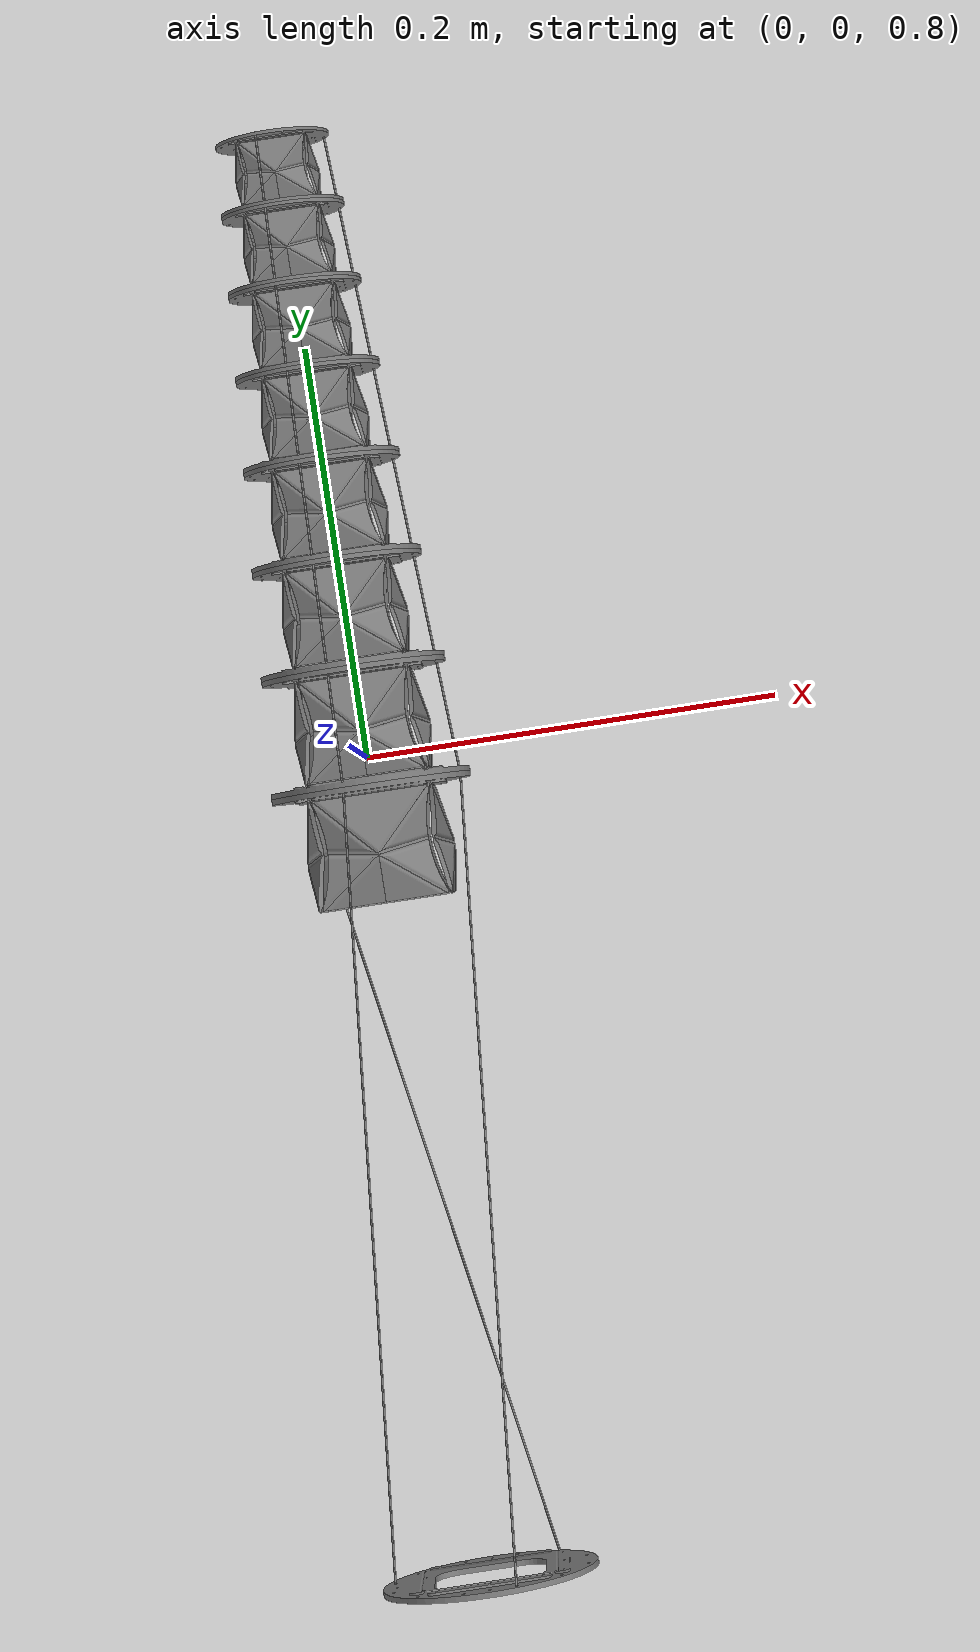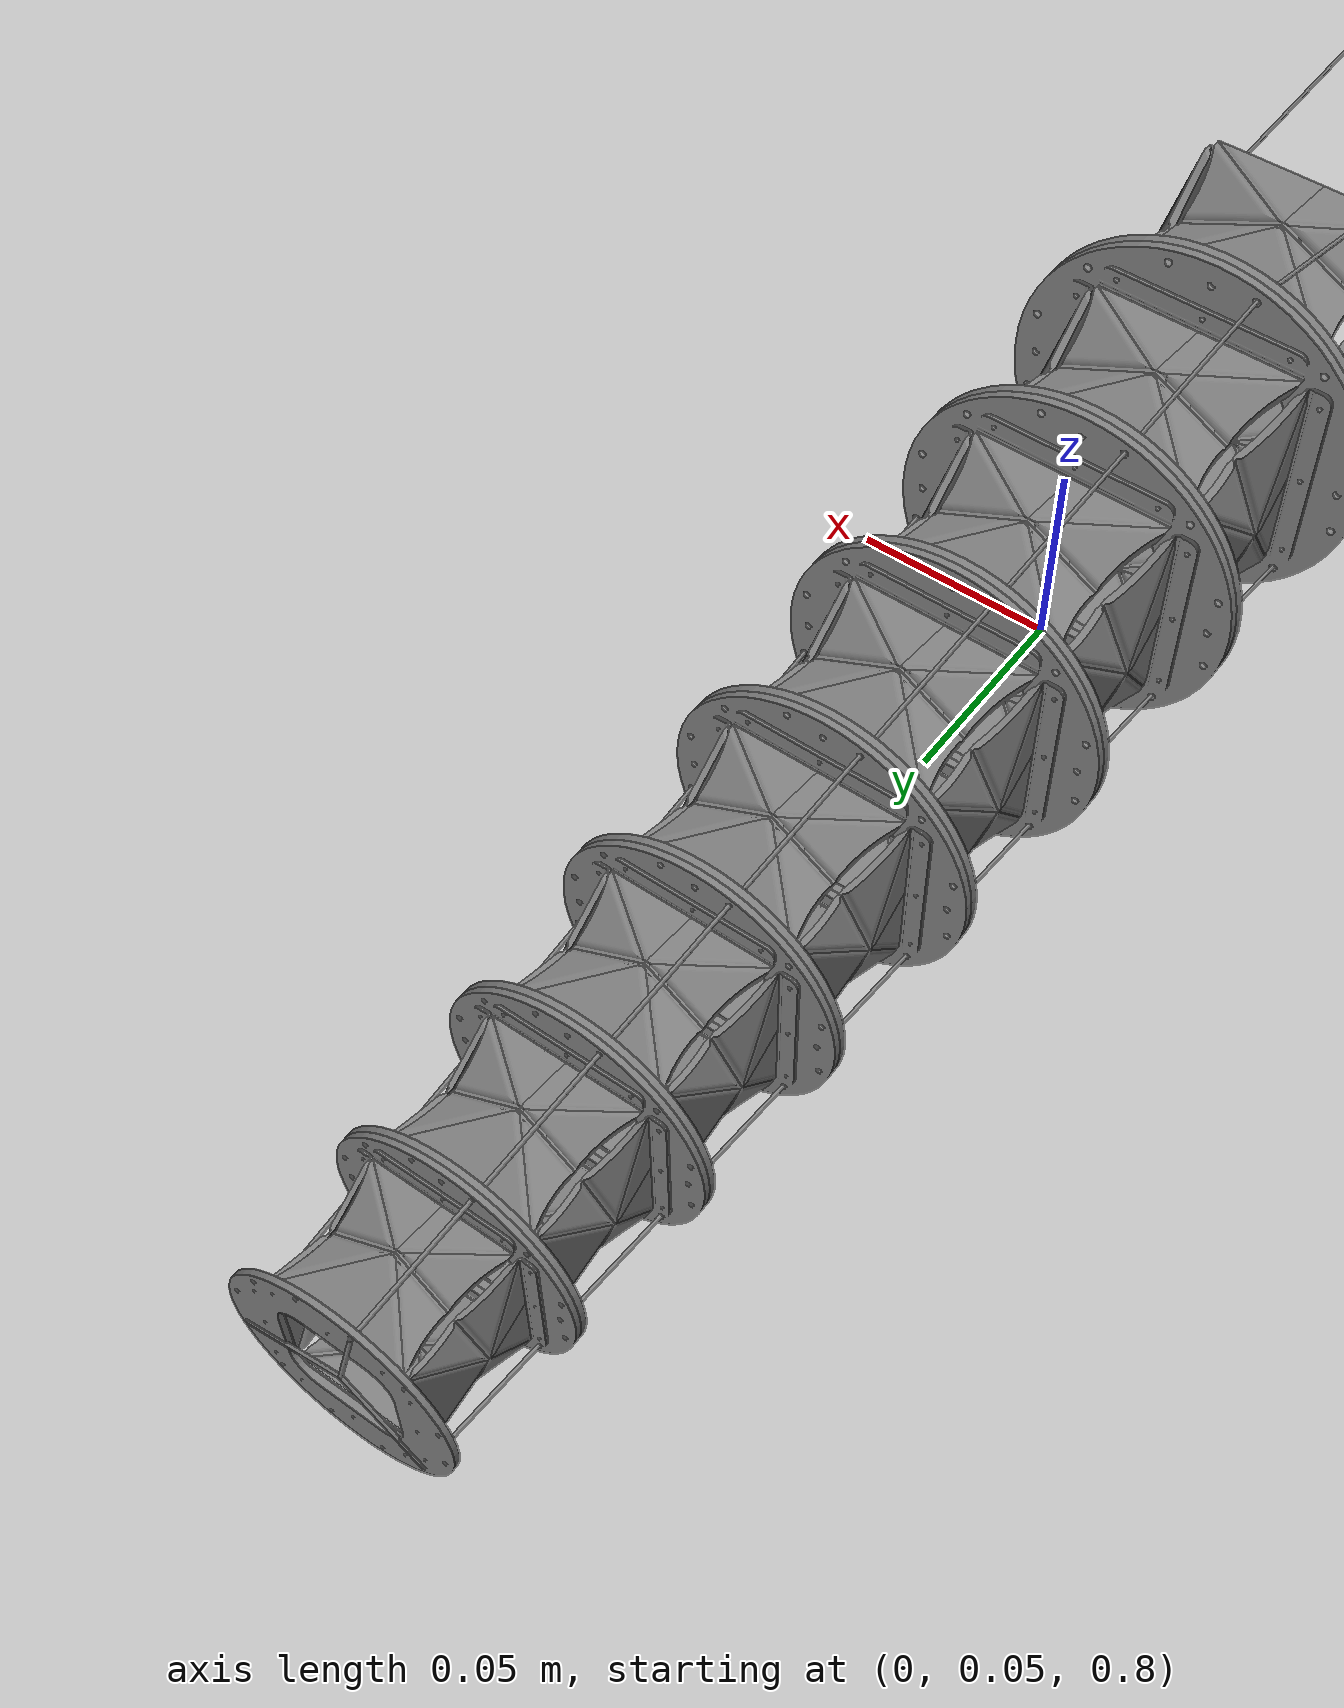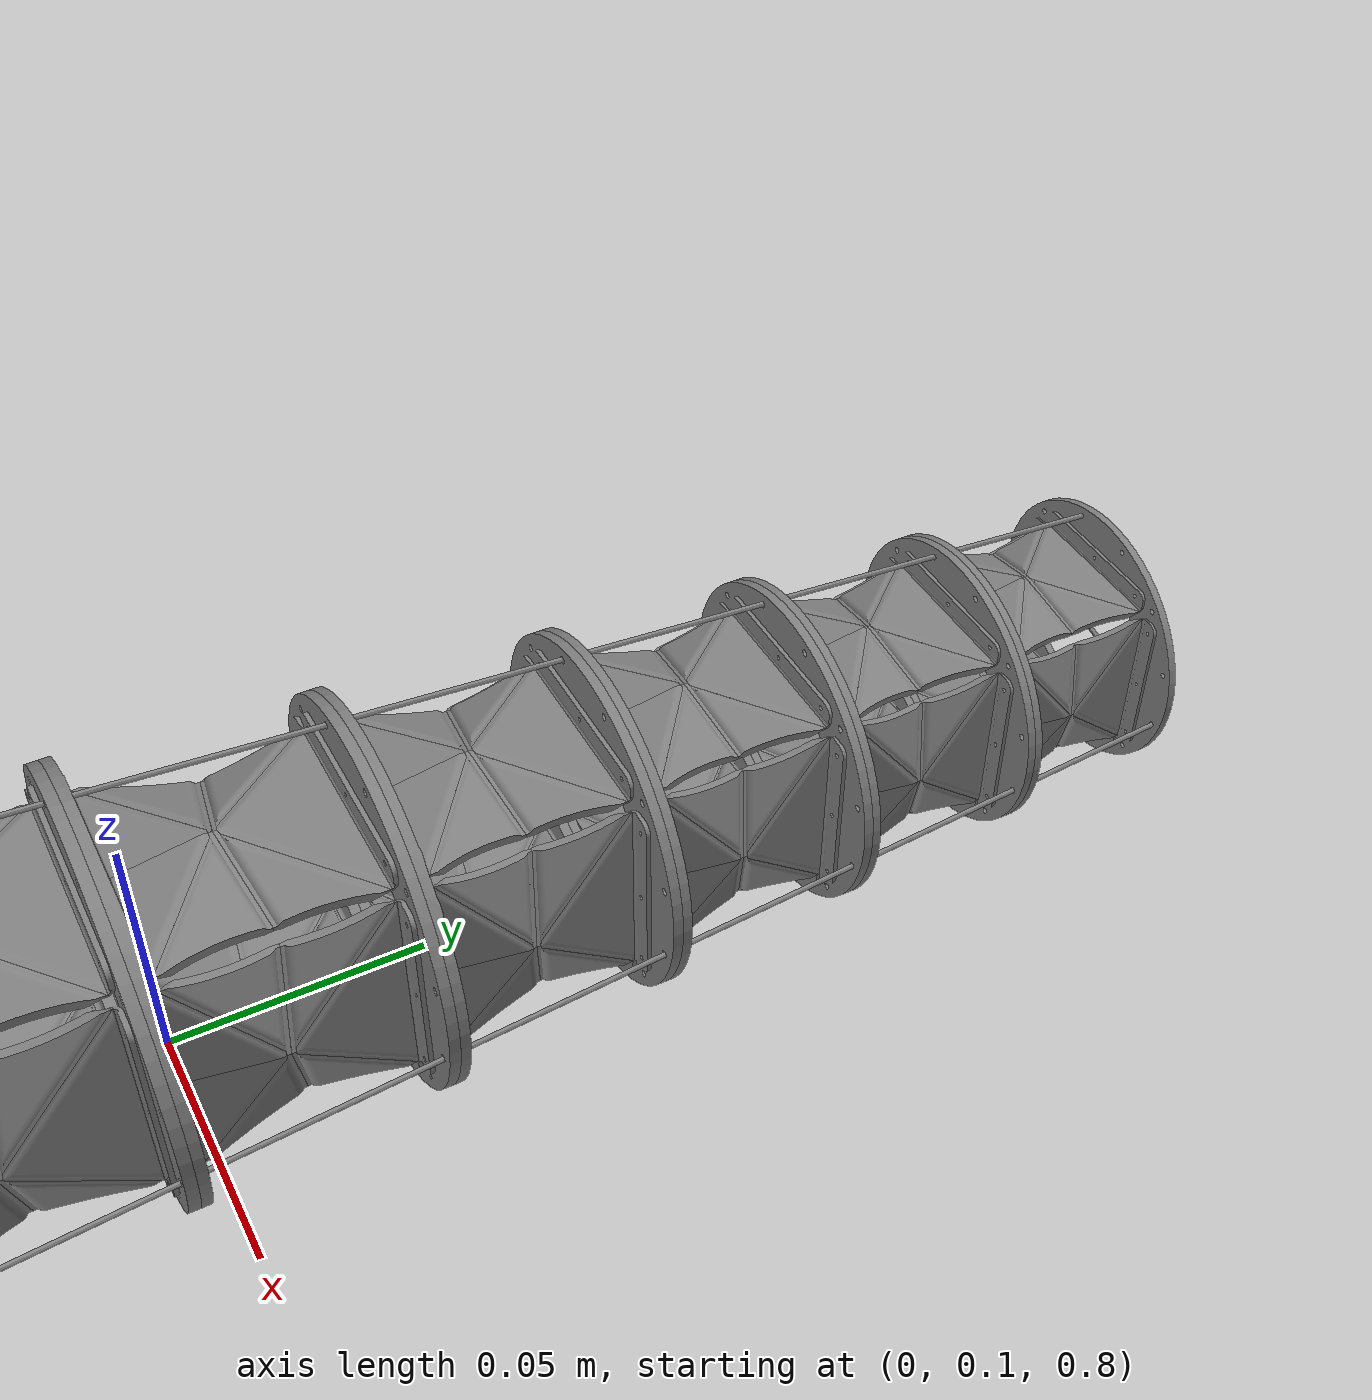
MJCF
<?xml version='1.0' encoding='utf-8'?>
<mujoco model="origami">
  <compiler angle="radian" coordinate="local" inertiafromgeom="false" balanceinertia="true" />
  <option timestep="0.002" gravity="0 0 -9.8" solver="Newton" />
  <size njmax="4000" nconmax="1000" />
  <asset>
    <mesh name="m8_seg2_m" file="STL/rib_seg2.stl" scale="1.0842694 1.0842694 1.0842694" />
    <mesh name="m8_seg5L_m" file="STL/rib_seg5L.stl" scale="1.0842694 1.0842694 1.0842694" />
    <mesh name="m8_seg5R_m" file="STL/rib_seg5R.stl" scale="1.0842694 1.0842694 1.0842694" />
    <mesh name="m8_seg6_m" file="STL/rib_seg6.stl" scale="1.0842694 1.0842694 1.0842694" />
    <mesh name="m8_seg4_m" file="STL/rib_seg4.stl" scale="1.0842694 1.0842694 1.0842694" />
    <mesh name="m8_seg3L_m" file="STL/rib_seg3L.stl" scale="1.0842694 1.0842694 1.0842694" />
    <mesh name="m8_seg3R_m" file="STL/rib_seg3R.stl" scale="1.0842694 1.0842694 1.0842694" />
    <mesh name="m8_bottom" file="STL/bottom_4x.stl" scale="1.0842694 1.0842694 1.0842694" />
    <mesh name="bottom8_col" file="STL/bottom_collision.stl" scale="1.7618156 1.7618156 1.7618156" />
    <mesh name="m8_top" file="STL/top_4x.stl" scale="1.0842694 1.0842694 1.0842694" />
    <mesh name="m7_seg2_m" file="STL/rib_seg2.stl" scale="1.1756402 1.1756402 1.1756402" />
    <mesh name="m7_seg5L_m" file="STL/rib_seg5L.stl" scale="1.1756402 1.1756402 1.1756402" />
    <mesh name="m7_seg5R_m" file="STL/rib_seg5R.stl" scale="1.1756402 1.1756402 1.1756402" />
    <mesh name="m7_seg6_m" file="STL/rib_seg6.stl" scale="1.1756402 1.1756402 1.1756402" />
    <mesh name="m7_seg4_m" file="STL/rib_seg4.stl" scale="1.1756402 1.1756402 1.1756402" />
    <mesh name="m7_seg3L_m" file="STL/rib_seg3L.stl" scale="1.1756402 1.1756402 1.1756402" />
    <mesh name="m7_seg3R_m" file="STL/rib_seg3R.stl" scale="1.1756402 1.1756402 1.1756402" />
    <mesh name="m7_bottom" file="STL/bottom_4x.stl" scale="1.1756402 1.1756402 1.1756402" />
    <mesh name="bottom7_col" file="STL/bottom_collision.stl" scale="1.9102828 1.9102828 1.9102828" />
    <mesh name="m7_top" file="STL/top_4x.stl" scale="1.1756402 1.1756402 1.1756402" />
    <mesh name="m6_seg2_m" file="STL/rib_seg2.stl" scale="1.2747107 1.2747107 1.2747107" />
    <mesh name="m6_seg5L_m" file="STL/rib_seg5L.stl" scale="1.2747107 1.2747107 1.2747107" />
    <mesh name="m6_seg5R_m" file="STL/rib_seg5R.stl" scale="1.2747107 1.2747107 1.2747107" />
    <mesh name="m6_seg6_m" file="STL/rib_seg6.stl" scale="1.2747107 1.2747107 1.2747107" />
    <mesh name="m6_seg4_m" file="STL/rib_seg4.stl" scale="1.2747107 1.2747107 1.2747107" />
    <mesh name="m6_seg3L_m" file="STL/rib_seg3L.stl" scale="1.2747107 1.2747107 1.2747107" />
    <mesh name="m6_seg3R_m" file="STL/rib_seg3R.stl" scale="1.2747107 1.2747107 1.2747107" />
    <mesh name="m6_bottom" file="STL/bottom_4x.stl" scale="1.2747107 1.2747107 1.2747107" />
    <mesh name="bottom6_col" file="STL/bottom_collision.stl" scale="2.0712612 2.0712612 2.0712612" />
    <mesh name="m6_top" file="STL/top_4x.stl" scale="1.2747107 1.2747107 1.2747107" />
    <mesh name="m5_seg2_m" file="STL/rib_seg2.stl" scale="1.3821298 1.3821298 1.3821298" />
    <mesh name="m5_seg5L_m" file="STL/rib_seg5L.stl" scale="1.3821298 1.3821298 1.3821298" />
    <mesh name="m5_seg5R_m" file="STL/rib_seg5R.stl" scale="1.3821298 1.3821298 1.3821298" />
    <mesh name="m5_seg6_m" file="STL/rib_seg6.stl" scale="1.3821298 1.3821298 1.3821298" />
    <mesh name="m5_seg4_m" file="STL/rib_seg4.stl" scale="1.3821298 1.3821298 1.3821298" />
    <mesh name="m5_seg3L_m" file="STL/rib_seg3L.stl" scale="1.3821298 1.3821298 1.3821298" />
    <mesh name="m5_seg3R_m" file="STL/rib_seg3R.stl" scale="1.3821298 1.3821298 1.3821298" />
    <mesh name="m5_bottom" file="STL/bottom_4x.stl" scale="1.3821298 1.3821298 1.3821298" />
    <mesh name="bottom5_col" file="STL/bottom_collision.stl" scale="2.2458052 2.2458052 2.2458052" />
    <mesh name="m5_top" file="STL/top_4x.stl" scale="1.3821298 1.3821298 1.3821298" />
    <mesh name="m4_seg2_m" file="STL/rib_seg2.stl" scale="1.4986011 1.4986011 1.4986011" />
    <mesh name="m4_seg5L_m" file="STL/rib_seg5L.stl" scale="1.4986011 1.4986011 1.4986011" />
    <mesh name="m4_seg5R_m" file="STL/rib_seg5R.stl" scale="1.4986011 1.4986011 1.4986011" />
    <mesh name="m4_seg6_m" file="STL/rib_seg6.stl" scale="1.4986011 1.4986011 1.4986011" />
    <mesh name="m4_seg4_m" file="STL/rib_seg4.stl" scale="1.4986011 1.4986011 1.4986011" />
    <mesh name="m4_seg3L_m" file="STL/rib_seg3L.stl" scale="1.4986011 1.4986011 1.4986011" />
    <mesh name="m4_seg3R_m" file="STL/rib_seg3R.stl" scale="1.4986011 1.4986011 1.4986011" />
    <mesh name="m4_bottom" file="STL/bottom_4x.stl" scale="1.4986011 1.4986011 1.4986011" />
    <mesh name="bottom4_col" file="STL/bottom_collision.stl" scale="2.4350579 2.4350579 2.4350579" />
    <mesh name="m4_top" file="STL/top_4x.stl" scale="1.4986011 1.4986011 1.4986011" />
    <mesh name="m3_seg2_m" file="STL/rib_seg2.stl" scale="1.6248873 1.6248873 1.6248873" />
    <mesh name="m3_seg5L_m" file="STL/rib_seg5L.stl" scale="1.6248873 1.6248873 1.6248873" />
    <mesh name="m3_seg5R_m" file="STL/rib_seg5R.stl" scale="1.6248873 1.6248873 1.6248873" />
    <mesh name="m3_seg6_m" file="STL/rib_seg6.stl" scale="1.6248873 1.6248873 1.6248873" />
    <mesh name="m3_seg4_m" file="STL/rib_seg4.stl" scale="1.6248873 1.6248873 1.6248873" />
    <mesh name="m3_seg3L_m" file="STL/rib_seg3L.stl" scale="1.6248873 1.6248873 1.6248873" />
    <mesh name="m3_seg3R_m" file="STL/rib_seg3R.stl" scale="1.6248873 1.6248873 1.6248873" />
    <mesh name="m3_bottom" file="STL/bottom_4x.stl" scale="1.6248873 1.6248873 1.6248873" />
    <mesh name="bottom3_col" file="STL/bottom_collision.stl" scale="2.6402588 2.6402588 2.6402588" />
    <mesh name="m3_top" file="STL/top_4x.stl" scale="1.6248873 1.6248873 1.6248873" />
    <mesh name="m2_seg2_m" file="STL/rib_seg2.stl" scale="1.7618156 1.7618156 1.7618156" />
    <mesh name="m2_seg5L_m" file="STL/rib_seg5L.stl" scale="1.7618156 1.7618156 1.7618156" />
    <mesh name="m2_seg5R_m" file="STL/rib_seg5R.stl" scale="1.7618156 1.7618156 1.7618156" />
    <mesh name="m2_seg6_m" file="STL/rib_seg6.stl" scale="1.7618156 1.7618156 1.7618156" />
    <mesh name="m2_seg4_m" file="STL/rib_seg4.stl" scale="1.7618156 1.7618156 1.7618156" />
    <mesh name="m2_seg3L_m" file="STL/rib_seg3L.stl" scale="1.7618156 1.7618156 1.7618156" />
    <mesh name="m2_seg3R_m" file="STL/rib_seg3R.stl" scale="1.7618156 1.7618156 1.7618156" />
    <mesh name="m2_bottom" file="STL/bottom_4x.stl" scale="1.7618156 1.7618156 1.7618156" />
    <mesh name="bottom2_col" file="STL/bottom_collision.stl" scale="2.8627519 2.8627519 2.8627519" />
    <mesh name="m2_top" file="STL/top_4x.stl" scale="1.7618156 1.7618156 1.7618156" />
    <mesh name="m1_seg2_m" file="STL/rib_seg2.stl" scale="1.9102828 1.9102828 1.9102828" />
    <mesh name="m1_seg5L_m" file="STL/rib_seg5L.stl" scale="1.9102828 1.9102828 1.9102828" />
    <mesh name="m1_seg5R_m" file="STL/rib_seg5R.stl" scale="1.9102828 1.9102828 1.9102828" />
    <mesh name="m1_seg6_m" file="STL/rib_seg6.stl" scale="1.9102828 1.9102828 1.9102828" />
    <mesh name="m1_seg4_m" file="STL/rib_seg4.stl" scale="1.9102828 1.9102828 1.9102828" />
    <mesh name="m1_seg3L_m" file="STL/rib_seg3L.stl" scale="1.9102828 1.9102828 1.9102828" />
    <mesh name="m1_seg3R_m" file="STL/rib_seg3R.stl" scale="1.9102828 1.9102828 1.9102828" />
    <mesh name="m1_bottom" file="STL/bottom_4x.stl" scale="1.9102828 1.9102828 1.9102828" />
    <mesh name="bottom1_col" file="STL/bottom_collision.stl" scale="3.1039943 3.1039943 3.1039943" />
    <mesh name="m1_top" file="STL/top_4x.stl" scale="1.9102828 1.9102828 1.9102828" />
  </asset>
  <worldbody>
    <body name="m1_top" pos="0 -0.4 0.82" quat="0.5 0.5 0.5 -0.5" childclass="m1">
      <inertial mass="0.017357707" pos="-5.7299736e-05 0 -0.0015664308" fullinertia="1.5358384e-05 1.5419944e-05 3.0745512e-05 0 1.526299e-09 0" />
      <site name="drag1" pos="0.012569625 -0.04689701 0" />
      <site name="drag2" pos="0.034346629 0.034331109 0" />
      <site name="drag3" pos="-0.046915944 0.01256559 0" />
      <geom class="vis_mesh" mesh="m1_top" />
      <geom name="disk1_top" class="collision_disk" pos="0 0 -0.0018623966" size="0.049663909 0.002" />
      <site name="m1_h5Ltop_a1_r3" pos="-0.0092075633 -0.031978135 -0.0042408279" />
      <site name="m1_h5Ltop_a2_r3" pos="-0.02066926 -0.031978135 -0.0042408279" />
      <site name="m1_h5Rtop_a1_r3" pos="0.0092075633 -0.031978135 -0.0042408279" />
      <site name="m1_h5Rtop_a2_r3" pos="0.02066926 -0.031978135 -0.0042408279" />
      <site name="m1_h5Ltop_a1" pos="0.031936943 -0.0092385187 -0.0042497053" />
      <site name="m1_h5Ltop_a2" pos="0.031936943 -0.020700215 -0.0042468282" />
      <site name="m1_h5Rtop_a1" pos="0.031936943 0.0091766072 -0.004254328" />
      <site name="m1_h5Rtop_a2" pos="0.031936943 0.020638304 -0.0042572051" />
      <site name="m1_h5Ltop_a1_r1" pos="0.0091973255 0.031905986 -0.0042609466" />
      <site name="m1_h5Ltop_a2_r1" pos="0.020659022 0.031905986 -0.0042620839" />
      <site name="m1_h5Rtop_a1_r1" pos="-0.0092178009 0.031905987 -0.0042591195" />
      <site name="m1_h5Rtop_a2_r1" pos="-0.020679498 0.031905987 -0.0042579823" />
      <site name="m1_h5Ltop_a1_r2" pos="-0.031947181 0.0091663702 -0.0042520692" />
      <site name="m1_h5Ltop_a2_r2" pos="-0.031947181 0.020628066 -0.0042560836" />
      <site name="m1_h5Rtop_a1_r2" pos="-0.031947181 -0.0092487552 -0.0042456194" />
      <site name="m1_h5Rtop_a2_r2" pos="-0.031947181 -0.020710451 -0.004241605" />
    </body>
    <body name="m8_bottom" pos="0 0.3 0.82" quat="0.5 0.5 0.5 -0.5" childclass="m8">
      <joint name="m8_bottom_tx" type="slide" axis="1 0 0" />
      <joint name="m8_bottom_ty" type="slide" axis="0 1 0" />
      <joint name="m8_bottom_tz" type="slide" axis="0 0 1" />
      <joint name="m8_bottom_rx" type="hinge" axis="1 0 0" />
      <joint name="m8_bottom_ry" type="hinge" axis="0 1 0" />
      <joint name="m8_bottom_rz" type="hinge" axis="0 0 1" />
      <geom mesh="m8_bottom" />
      <geom name="disk8_bottom" class="collision_disk" pos="0 0 0.001233271" size="0.026427235 0.001233271" />
      <site name="rope1_8_bottom" pos="-0.024549958 -0.006579576 0" />
      <site name="rope2_8_bottom" pos="0.017971233 -0.017979236 0" />
      <site name="rope3_8_bottom" pos="0.0065772489 0.02455552 0" />
      <inertial mass="0.0027151337" pos="0 0 0.00089993542" fullinertia="2.1879576e-09 2.1879576e-09 1.4986011e-12 0 0 0" />
      <body name="m8_seg2" pos="-1.0472536e-11 -0.016545951 0.0024395628" quat="-1.65174999e-08 -6.799909979e-08 7.900499979e-05 0.9999999969">
        <inertial mass="0.00028043635" pos="0 0.0011167975 0.0054864032" fullinertia="4.1810971e-09 1.4671305e-08 1.089483e-08 0 0 8.242306e-10" />
        <joint name="m8_j_bottom_seg2" type="hinge" pos="0 0.00026022466 0" axis="-1 0 0" limited="true" range="0 1.2" solreflimit="0.004 1" solimplimit="0.99 0.999 0.001" />
        <geom mesh="m8_seg2_m" />
        <geom class="collision_capsule" fromto="0 0.0010842694 0.0021685389 0 0.0032528083 0.013011233" />
        <geom class="collision_capsule" fromto="0.010842694 0.0010842694 0.0021685389 0 0.0032528083 0.013011233" />
        <geom class="collision_capsule" fromto="-0.010842694 0.0010842694 0.0021685389 0 0.0032528083 0.013011233" />
        <body name="m8_seg3L" pos="0.0068669687 0.001019291 0.015590051" quat="0.9999999285 0.0003082339588 -0.0001961842889 9.741099365e-05">
          <inertial mass="0.00010197686" pos="0.0030359544 -0.00034696622 -0.005247864" fullinertia="1.2738109e-09 2.2179296e-09 1.1239508e-09 -2.6974819e-10 -7.6428654e-10 1.0490207e-10" />
          <joint name="m8_j_seg2_seg3L" type="hinge" pos="0.0011601683 0.00091620766 -0.0074435098" axis="0.679022595 -0.149946644 -0.718640605" limited="true" range="0 2.3" />
          <geom mesh="m8_seg3L_m" />
          <geom class="collision_capsule" fromto="-0.0021685389 0.0015179772 -0.0016264041 0.005963482 -0.0010842694 -0.0032528083" />
          <geom class="collision_capsule" fromto="0.005963482 -0.0010842694 -0.0032528083 0.0065056165 -0.00032528083 -0.010842694" />
          <geom class="collision_capsule" fromto="0.0065056165 -0.00032528083 -0.010842694 -0.0021685389 0.0015179772 -0.0016264041" />
          <body name="m8_seg4" pos="0.00092006891 0.00093434287 0.0039067324" quat="0.0001974378419 -0.0003798622158 -0.0002749162209 -0.9999998706">
            <inertial mass="0.00011472396" pos="-0.0024721269 0.00082403644 0.00083488922" fullinertia="1.2138669e-09 2.3827757e-09 1.378713e-09 -2.3977617e-10 -6.5938447e-10 -7.4930054e-11" />
            <joint name="m8_j_seg3L_seg4" type="hinge" pos="0.00091620766 0.00066140433 -0.0039087912" axis="-0.933080263 0.328456036 -0.146553254" limited="true" range="-2.3 0" />
            <geom mesh="m8_seg4_m" />
            <geom class="collision_capsule" fromto="-0.0056759627 0.00017027888 0.0045407701 0.0034055777 -0.0011351925 -0.0011351925" />
            <geom class="collision_capsule" fromto="-0.0056759627 0.00017027888 0.0045407701 -0.0045407701 0.0011351925 -0.0017027888" />
            <geom class="collision_capsule" fromto="0.0034055777 -0.0011351925 -0.0011351925 -0.0045407701 0.0011351925 -0.0017027888" />
            <body name="m8_seg5L" pos="0.0077896538 -0.00036776767 0.0040904997" quat="0.9999999499 5.935617349e-05 9.675184149e-05 -0.000295444026">
              <inertial mass="0.00011472396" pos="-0.0054538752 0.00031443813 0.0019625276" fullinertia="1.0789928e-09 2.787398e-09 1.7983213e-09 -1.0490207e-10 -6.7437047e-10 1.6484612e-10" />
              <joint name="m8_j_seg4_seg5L" type="hinge" pos="-0.008712105 -0.00029817409 -0.0001843258" axis="-0.787976619 0.0989651559 0.607699552" limited="true" range="0 2.3" />
              <geom mesh="m8_seg5L_m" />
              <geom class="collision_capsule" fromto="-0.0010842694 0 0.0032528083 -0.0010842694 -0.0010842694 -0.0032528083" />
              <geom class="collision_capsule" fromto="-0.010842694 0 0.0032528083 -0.0010842694 0 0.0032528083" />
              <geom class="collision_capsule" fromto="-0.010842694 0 0.0032528083 -0.0010842694 -0.0010842694 -0.0032528083" />
              <site name="m8_h5Ltop_b1" pos="-0.0052261786 0.00072646051 0.0062996052" />
              <site name="m8_h5Ltop_b2" pos="-0.011731795 0.00072646051 0.0062996052" />
            </body>
          </body>
        </body>
        <body name="m8_seg3R" pos="-0.0068679274 0.0010214603 0.015591784" quat="0.9999999578 0.000228090995 0.000134725593 -0.000118935139">
          <inertial mass="0.00010197686" pos="-0.0030359544 -0.00034696622 -0.005247864" fullinertia="1.2738109e-09 2.2179296e-09 1.1239508e-09 2.6974819e-10 7.6428654e-10 1.0490207e-10" />
          <joint name="m8_j_seg2_seg3R" type="hinge" pos="-0.0011601683 0.00091620766 -0.0074435098" axis="-0.679022595 -0.149946644 -0.718640605" limited="true" range="-2.3 0" />
          <geom mesh="m8_seg3R_m" />
          <geom class="collision_capsule" fromto="-0.0054213471 -0.0010842694 -0.0032528083 0.0010842694 0.0015179772 -0.0021685389" />
          <geom class="collision_capsule" fromto="0.0010842694 0.0015179772 -0.0021685389 -0.0065056165 -0.00054213471 -0.0097584245" />
          <geom class="collision_capsule" fromto="-0.0065056165 -0.00054213471 -0.0097584245 -0.0054213471 -0.0010842694 -0.0032528083" />
          <body name="m8_seg6" pos="-1.2148837e-06 7.5943201e-07 1.1919026e-06" quat="0.999999944 -0.000276734689 -0.000185901643 2.75436731e-05">
            <inertial mass="0.00011472396" pos="-0.0033937633 0.00010842694 0.0047382574" fullinertia="1.2138669e-09 2.3827757e-09 1.378713e-09 2.3977617e-10 -6.5938447e-10 7.4930054e-11" />
            <joint name="m8_j_seg3R_seg6" type="hinge" pos="0 0.00027106736 0" axis="-0.933074618 -0.328195015 -0.147172653" limited="true" range="0 2.3" />
            <geom mesh="m8_seg6_m" />
            <geom class="collision_capsule" fromto="-0.0065056165 0.00043370777 0.007589886 0.0021685389 0.001951685 0.0027106736" />
            <geom class="collision_capsule" fromto="0.0021685389 0.001951685 0.0027106736 -0.0065056165 -0.0010842694 0.0021685389" />
            <geom class="collision_capsule" fromto="-0.0065056165 -0.0010842694 0.0021685389 -0.0065056165 0.00043370777 0.007589886" />
            <body name="m8_seg5R" pos="0.0068678797 0.0012918042 0.0079967913" quat="0.999999996 -6.20560017e-05 3.4735276e-05 5.4285215e-05">
              <inertial mass="0.00011472396" pos="-0.0054538752 -0.00031443813 0.0019625276" fullinertia="1.0789928e-09 2.787398e-09 1.7983213e-09 1.0490207e-10 -6.7437047e-10 -1.6484612e-10" />
              <joint name="m8_j_seg5R_seg6" type="hinge" pos="-0.008712105 0.00029817409 -0.0001843258" axis="-0.787976619 -0.0989651559 0.607699552" limited="true" range="-2.3 0" />
              <geom mesh="m8_seg5R_m" />
              <geom class="collision_capsule" fromto="-0.0017618156 -0.00010842694 0.0035236313 -0.0017618156 0.0010842694 -0.0035236313" />
              <geom class="collision_capsule" fromto="-0.010570894 -0.00010842694 0.0035236313 -0.0017618156 -0.00010842694 0.0035236313" />
              <geom class="collision_capsule" fromto="-0.010570894 -0.00010842694 0.0035236313 -0.0017618156 0.0010842694 -0.0035236313" />
              <site name="m8_h5Rtop_b1" pos="-0.0052261786 -0.00072646051 0.0062996052" />
              <site name="m8_h5Rtop_b2" pos="-0.011731795 -0.00072646051 0.0062996052" />
            </body>
          </body>
        </body>
      </body>
      <body name="m8_seg2_r1" pos="0.016545951 -1.0472537e-11 0.0024395628" quat="-0.7071067907 -5.591305372e-05 5.581688847e-05 0.7071067673">
        <inertial mass="0.00028043635" pos="0 0.0011167975 0.0054864032" fullinertia="4.1810971e-09 1.4671305e-08 1.089483e-08 0 0 8.242306e-10" />
        <joint name="m8_j_bottom_seg2_r1" type="hinge" pos="0 0.00026022466 0" axis="-1 0 0" limited="true" range="0 1.2" solreflimit="0.004 1" solimplimit="0.99 0.999 0.001" />
        <geom mesh="m8_seg2_m" />
        <geom class="collision_capsule" fromto="0 0.0010842694 0.0021685389 0 0.0032528083 0.013011233" />
        <geom class="collision_capsule" fromto="0.010842694 0.0010842694 0.0021685389 0 0.0032528083 0.013011233" />
        <geom class="collision_capsule" fromto="-0.010842694 0.0010842694 0.0021685389 0 0.0032528083 0.013011233" />
        <body name="m8_seg3L_r1" pos="0.0068669687 0.001019291 0.015590051" quat="0.9999999285 0.0003082339588 -0.0001961842889 9.741099365e-05">
          <inertial mass="0.00010197686" pos="0.0030359544 -0.00034696622 -0.005247864" fullinertia="1.2738109e-09 2.2179296e-09 1.1239508e-09 -2.6974819e-10 -7.6428654e-10 1.0490207e-10" />
          <joint name="m8_j_seg2_seg3L_r1" type="hinge" pos="0.0011601683 0.00091620766 -0.0074435098" axis="0.679022595 -0.149946644 -0.718640605" limited="true" range="0 2.3" />
          <geom mesh="m8_seg3L_m" />
          <geom class="collision_capsule" fromto="-0.0021685389 0.0015179772 -0.0016264041 0.005963482 -0.0010842694 -0.0032528083" />
          <geom class="collision_capsule" fromto="0.005963482 -0.0010842694 -0.0032528083 0.0065056165 -0.00032528083 -0.010842694" />
          <geom class="collision_capsule" fromto="0.0065056165 -0.00032528083 -0.010842694 -0.0021685389 0.0015179772 -0.0016264041" />
          <body name="m8_seg4_r1" pos="0.00092006891 0.00093434287 0.0039067324" quat="0.0001974378419 -0.0003798622158 -0.0002749162209 -0.9999998706">
            <inertial mass="0.00011472396" pos="-0.0024721269 0.00082403644 0.00083488922" fullinertia="1.2138669e-09 2.3827757e-09 1.378713e-09 -2.3977617e-10 -6.5938447e-10 -7.4930054e-11" />
            <joint name="m8_j_seg3L_seg4_r1" type="hinge" pos="0.00091620766 0.00066140433 -0.0039087912" axis="-0.933080263 0.328456036 -0.146553254" limited="true" range="-2.3 0" />
            <geom mesh="m8_seg4_m" />
            <geom class="collision_capsule" fromto="-0.0056759627 0.00017027888 0.0045407701 0.0034055777 -0.0011351925 -0.0011351925" />
            <geom class="collision_capsule" fromto="-0.0056759627 0.00017027888 0.0045407701 -0.0045407701 0.0011351925 -0.0017027888" />
            <geom class="collision_capsule" fromto="0.0034055777 -0.0011351925 -0.0011351925 -0.0045407701 0.0011351925 -0.0017027888" />
            <body name="m8_seg5L_r1" pos="0.0077896538 -0.00036776767 0.0040904997" quat="0.9999999499 5.935617349e-05 9.675184149e-05 -0.000295444026">
              <inertial mass="0.00011472396" pos="-0.0054538752 0.00031443813 0.0019625276" fullinertia="1.0789928e-09 2.787398e-09 1.7983213e-09 -1.0490207e-10 -6.7437047e-10 1.6484612e-10" />
              <joint name="m8_j_seg4_seg5L_r1" type="hinge" pos="-0.008712105 -0.00029817409 -0.0001843258" axis="-0.787976619 0.0989651559 0.607699552" limited="true" range="0 2.3" />
              <geom mesh="m8_seg5L_m" />
              <geom class="collision_capsule" fromto="-0.0010842694 0 0.0032528083 -0.0010842694 -0.0010842694 -0.0032528083" />
              <geom class="collision_capsule" fromto="-0.010842694 0 0.0032528083 -0.0010842694 0 0.0032528083" />
              <geom class="collision_capsule" fromto="-0.010842694 0 0.0032528083 -0.0010842694 -0.0010842694 -0.0032528083" />
              <site name="m8_h5Ltop_b1_r1" pos="-0.0052261786 0.00072646051 0.0062996052" />
              <site name="m8_h5Ltop_b2_r1" pos="-0.011731795 0.00072646051 0.0062996052" />
            </body>
          </body>
        </body>
        <body name="m8_seg3R_r1" pos="-0.0068679274 0.0010214603 0.015591784" quat="0.9999999578 0.000228090995 0.000134725593 -0.000118935139">
          <inertial mass="0.00010197686" pos="-0.0030359544 -0.00034696622 -0.005247864" fullinertia="1.2738109e-09 2.2179296e-09 1.1239508e-09 2.6974819e-10 7.6428654e-10 1.0490207e-10" />
          <joint name="m8_j_seg2_seg3R_r1" type="hinge" pos="-0.0011601683 0.00091620766 -0.0074435098" axis="-0.679022595 -0.149946644 -0.718640605" limited="true" range="-2.3 0" />
          <geom mesh="m8_seg3R_m" />
          <geom class="collision_capsule" fromto="-0.0054213471 -0.0010842694 -0.0032528083 0.0010842694 0.0015179772 -0.0021685389" />
          <geom class="collision_capsule" fromto="0.0010842694 0.0015179772 -0.0021685389 -0.0065056165 -0.00054213471 -0.0097584245" />
          <geom class="collision_capsule" fromto="-0.0065056165 -0.00054213471 -0.0097584245 -0.0054213471 -0.0010842694 -0.0032528083" />
          <body name="m8_seg6_r1" pos="-1.2148837e-06 7.5943201e-07 1.1919026e-06" quat="0.999999944 -0.000276734689 -0.000185901643 2.75436731e-05">
            <inertial mass="0.00011472396" pos="-0.0033937633 0.00010842694 0.0047382574" fullinertia="1.2138669e-09 2.3827757e-09 1.378713e-09 2.3977617e-10 -6.5938447e-10 7.4930054e-11" />
            <joint name="m8_j_seg3R_seg6_r1" type="hinge" pos="0 0.00027106736 0" axis="-0.933074618 -0.328195015 -0.147172653" limited="true" range="0 2.3" />
            <geom mesh="m8_seg6_m" />
            <geom class="collision_capsule" fromto="-0.0065056165 0.00043370777 0.007589886 0.0021685389 0.001951685 0.0027106736" />
            <geom class="collision_capsule" fromto="0.0021685389 0.001951685 0.0027106736 -0.0065056165 -0.0010842694 0.0021685389" />
            <geom class="collision_capsule" fromto="-0.0065056165 -0.0010842694 0.0021685389 -0.0065056165 0.00043370777 0.007589886" />
            <body name="m8_seg5R_r1" pos="0.0068678797 0.0012918042 0.0079967913" quat="0.999999996 -6.20560017e-05 3.4735276e-05 5.4285215e-05">
              <inertial mass="0.00011472396" pos="-0.0054538752 -0.00031443813 0.0019625276" fullinertia="1.0789928e-09 2.787398e-09 1.7983213e-09 1.0490207e-10 -6.7437047e-10 -1.6484612e-10" />
              <joint name="m8_j_seg5R_seg6_r1" type="hinge" pos="-0.008712105 0.00029817409 -0.0001843258" axis="-0.787976619 -0.0989651559 0.607699552" limited="true" range="-2.3 0" />
              <geom mesh="m8_seg5R_m" />
              <geom class="collision_capsule" fromto="-0.0017618156 -0.00010842694 0.0035236313 -0.0017618156 0.0010842694 -0.0035236313" />
              <geom class="collision_capsule" fromto="-0.010570894 -0.00010842694 0.0035236313 -0.0017618156 -0.00010842694 0.0035236313" />
              <geom class="collision_capsule" fromto="-0.010570894 -0.00010842694 0.0035236313 -0.0017618156 0.0010842694 -0.0035236313" />
              <site name="m8_h5Rtop_b1_r1" pos="-0.0052261786 -0.00072646051 0.0062996052" />
              <site name="m8_h5Rtop_b2_r1" pos="-0.011731795 -0.00072646051 0.0062996052" />
            </body>
          </body>
        </body>
      </body>
      <body name="m8_seg2_r2" pos="1.0472537e-11 0.016545951 0.0024395628" quat="-0.9999999969 -7.900499979e-05 -6.799909979e-08 -1.651749984e-08">
        <inertial mass="0.00028043635" pos="0 0.0011167975 0.0054864032" fullinertia="4.1810971e-09 1.4671305e-08 1.089483e-08 0 0 8.242306e-10" />
        <joint name="m8_j_bottom_seg2_r2" type="hinge" pos="0 0.00026022466 0" axis="-1 0 0" limited="true" range="0 1.2" solreflimit="0.004 1" solimplimit="0.99 0.999 0.001" />
        <geom mesh="m8_seg2_m" />
        <geom class="collision_capsule" fromto="0 0.0010842694 0.0021685389 0 0.0032528083 0.013011233" />
        <geom class="collision_capsule" fromto="0.010842694 0.0010842694 0.0021685389 0 0.0032528083 0.013011233" />
        <geom class="collision_capsule" fromto="-0.010842694 0.0010842694 0.0021685389 0 0.0032528083 0.013011233" />
        <body name="m8_seg3L_r2" pos="0.0068669687 0.001019291 0.015590051" quat="0.9999999285 0.0003082339588 -0.0001961842889 9.741099365e-05">
          <inertial mass="0.00010197686" pos="0.0030359544 -0.00034696622 -0.005247864" fullinertia="1.2738109e-09 2.2179296e-09 1.1239508e-09 -2.6974819e-10 -7.6428654e-10 1.0490207e-10" />
          <joint name="m8_j_seg2_seg3L_r2" type="hinge" pos="0.0011601683 0.00091620766 -0.0074435098" axis="0.679022595 -0.149946644 -0.718640605" limited="true" range="0 2.3" />
          <geom mesh="m8_seg3L_m" />
          <geom class="collision_capsule" fromto="-0.0021685389 0.0015179772 -0.0016264041 0.005963482 -0.0010842694 -0.0032528083" />
          <geom class="collision_capsule" fromto="0.005963482 -0.0010842694 -0.0032528083 0.0065056165 -0.00032528083 -0.010842694" />
          <geom class="collision_capsule" fromto="0.0065056165 -0.00032528083 -0.010842694 -0.0021685389 0.0015179772 -0.0016264041" />
          <body name="m8_seg4_r2" pos="0.00092006891 0.00093434287 0.0039067324" quat="0.0001974378419 -0.0003798622158 -0.0002749162209 -0.9999998706">
            <inertial mass="0.00011472396" pos="-0.0024721269 0.00082403644 0.00083488922" fullinertia="1.2138669e-09 2.3827757e-09 1.378713e-09 -2.3977617e-10 -6.5938447e-10 -7.4930054e-11" />
            <joint name="m8_j_seg3L_seg4_r2" type="hinge" pos="0.00091620766 0.00066140433 -0.0039087912" axis="-0.933080263 0.328456036 -0.146553254" limited="true" range="-2.3 0" />
            <geom mesh="m8_seg4_m" />
            <geom class="collision_capsule" fromto="-0.0056759627 0.00017027888 0.0045407701 0.0034055777 -0.0011351925 -0.0011351925" />
            <geom class="collision_capsule" fromto="-0.0056759627 0.00017027888 0.0045407701 -0.0045407701 0.0011351925 -0.0017027888" />
            <geom class="collision_capsule" fromto="0.0034055777 -0.0011351925 -0.0011351925 -0.0045407701 0.0011351925 -0.0017027888" />
            <body name="m8_seg5L_r2" pos="0.0077896538 -0.00036776767 0.0040904997" quat="0.9999999499 5.935617349e-05 9.675184149e-05 -0.000295444026">
              <inertial mass="0.00011472396" pos="-0.0054538752 0.00031443813 0.0019625276" fullinertia="1.0789928e-09 2.787398e-09 1.7983213e-09 -1.0490207e-10 -6.7437047e-10 1.6484612e-10" />
              <joint name="m8_j_seg4_seg5L_r2" type="hinge" pos="-0.008712105 -0.00029817409 -0.0001843258" axis="-0.787976619 0.0989651559 0.607699552" limited="true" range="0 2.3" />
              <geom mesh="m8_seg5L_m" />
              <geom class="collision_capsule" fromto="-0.0010842694 0 0.0032528083 -0.0010842694 -0.0010842694 -0.0032528083" />
              <geom class="collision_capsule" fromto="-0.010842694 0 0.0032528083 -0.0010842694 0 0.0032528083" />
              <geom class="collision_capsule" fromto="-0.010842694 0 0.0032528083 -0.0010842694 -0.0010842694 -0.0032528083" />
              <site name="m8_h5Ltop_b1_r2" pos="-0.0052261786 0.00072646051 0.0062996052" />
              <site name="m8_h5Ltop_b2_r2" pos="-0.011731795 0.00072646051 0.0062996052" />
            </body>
          </body>
        </body>
        <body name="m8_seg3R_r2" pos="-0.0068679274 0.0010214603 0.015591784" quat="0.9999999578 0.000228090995 0.000134725593 -0.000118935139">
          <inertial mass="0.00010197686" pos="-0.0030359544 -0.00034696622 -0.005247864" fullinertia="1.2738109e-09 2.2179296e-09 1.1239508e-09 2.6974819e-10 7.6428654e-10 1.0490207e-10" />
          <joint name="m8_j_seg2_seg3R_r2" type="hinge" pos="-0.0011601683 0.00091620766 -0.0074435098" axis="-0.679022595 -0.149946644 -0.718640605" limited="true" range="-2.3 0" />
          <geom mesh="m8_seg3R_m" />
          <geom class="collision_capsule" fromto="-0.0054213471 -0.0010842694 -0.0032528083 0.0010842694 0.0015179772 -0.0021685389" />
          <geom class="collision_capsule" fromto="0.0010842694 0.0015179772 -0.0021685389 -0.0065056165 -0.00054213471 -0.0097584245" />
          <geom class="collision_capsule" fromto="-0.0065056165 -0.00054213471 -0.0097584245 -0.0054213471 -0.0010842694 -0.0032528083" />
          <body name="m8_seg6_r2" pos="-1.2148837e-06 7.5943201e-07 1.1919026e-06" quat="0.999999944 -0.000276734689 -0.000185901643 2.75436731e-05">
            <inertial mass="0.00011472396" pos="-0.0033937633 0.00010842694 0.0047382574" fullinertia="1.2138669e-09 2.3827757e-09 1.378713e-09 2.3977617e-10 -6.5938447e-10 7.4930054e-11" />
            <joint name="m8_j_seg3R_seg6_r2" type="hinge" pos="0 0.00027106736 0" axis="-0.933074618 -0.328195015 -0.147172653" limited="true" range="0 2.3" />
            <geom mesh="m8_seg6_m" />
            <geom class="collision_capsule" fromto="-0.0065056165 0.00043370777 0.007589886 0.0021685389 0.001951685 0.0027106736" />
            <geom class="collision_capsule" fromto="0.0021685389 0.001951685 0.0027106736 -0.0065056165 -0.0010842694 0.0021685389" />
            <geom class="collision_capsule" fromto="-0.0065056165 -0.0010842694 0.0021685389 -0.0065056165 0.00043370777 0.007589886" />
            <body name="m8_seg5R_r2" pos="0.0068678797 0.0012918042 0.0079967913" quat="0.999999996 -6.20560017e-05 3.4735276e-05 5.4285215e-05">
              <inertial mass="0.00011472396" pos="-0.0054538752 -0.00031443813 0.0019625276" fullinertia="1.0789928e-09 2.787398e-09 1.7983213e-09 1.0490207e-10 -6.7437047e-10 -1.6484612e-10" />
              <joint name="m8_j_seg5R_seg6_r2" type="hinge" pos="-0.008712105 0.00029817409 -0.0001843258" axis="-0.787976619 -0.0989651559 0.607699552" limited="true" range="-2.3 0" />
              <geom mesh="m8_seg5R_m" />
              <geom class="collision_capsule" fromto="-0.0017618156 -0.00010842694 0.0035236313 -0.0017618156 0.0010842694 -0.0035236313" />
              <geom class="collision_capsule" fromto="-0.010570894 -0.00010842694 0.0035236313 -0.0017618156 -0.00010842694 0.0035236313" />
              <geom class="collision_capsule" fromto="-0.010570894 -0.00010842694 0.0035236313 -0.0017618156 0.0010842694 -0.0035236313" />
              <site name="m8_h5Rtop_b1_r2" pos="-0.0052261786 -0.00072646051 0.0062996052" />
              <site name="m8_h5Rtop_b2_r2" pos="-0.011731795 -0.00072646051 0.0062996052" />
            </body>
          </body>
        </body>
      </body>
      <body name="m8_seg2_r3" pos="-0.016545951 1.0472538e-11 0.0024395628" quat="-0.7071067673 -5.581688847e-05 -5.591305372e-05 -0.7071067907">
        <inertial mass="0.00028043635" pos="0 0.0011167975 0.0054864032" fullinertia="4.1810971e-09 1.4671305e-08 1.089483e-08 0 0 8.242306e-10" />
        <joint name="m8_j_bottom_seg2_r3" type="hinge" pos="0 0.00026022466 0" axis="-1 0 0" limited="true" range="0 1.2" solreflimit="0.004 1" solimplimit="0.99 0.999 0.001" />
        <geom mesh="m8_seg2_m" />
        <geom class="collision_capsule" fromto="0 0.0010842694 0.0021685389 0 0.0032528083 0.013011233" />
        <geom class="collision_capsule" fromto="0.010842694 0.0010842694 0.0021685389 0 0.0032528083 0.013011233" />
        <geom class="collision_capsule" fromto="-0.010842694 0.0010842694 0.0021685389 0 0.0032528083 0.013011233" />
        <body name="m8_seg3L_r3" pos="0.0068669687 0.001019291 0.015590051" quat="0.9999999285 0.0003082339588 -0.0001961842889 9.741099365e-05">
          <inertial mass="0.00010197686" pos="0.0030359544 -0.00034696622 -0.005247864" fullinertia="1.2738109e-09 2.2179296e-09 1.1239508e-09 -2.6974819e-10 -7.6428654e-10 1.0490207e-10" />
          <joint name="m8_j_seg2_seg3L_r3" type="hinge" pos="0.0011601683 0.00091620766 -0.0074435098" axis="0.679022595 -0.149946644 -0.718640605" limited="true" range="0 2.3" />
          <geom mesh="m8_seg3L_m" />
          <geom class="collision_capsule" fromto="-0.0021685389 0.0015179772 -0.0016264041 0.005963482 -0.0010842694 -0.0032528083" />
          <geom class="collision_capsule" fromto="0.005963482 -0.0010842694 -0.0032528083 0.0065056165 -0.00032528083 -0.010842694" />
          <geom class="collision_capsule" fromto="0.0065056165 -0.00032528083 -0.010842694 -0.0021685389 0.0015179772 -0.0016264041" />
          <body name="m8_seg4_r3" pos="0.00092006891 0.00093434287 0.0039067324" quat="0.0001974378419 -0.0003798622158 -0.0002749162209 -0.9999998706">
            <inertial mass="0.00011472396" pos="-0.0024721269 0.00082403644 0.00083488922" fullinertia="1.2138669e-09 2.3827757e-09 1.378713e-09 -2.3977617e-10 -6.5938447e-10 -7.4930054e-11" />
            <joint name="m8_j_seg3L_seg4_r3" type="hinge" pos="0.00091620766 0.00066140433 -0.0039087912" axis="-0.933080263 0.328456036 -0.146553254" limited="true" range="-2.3 0" />
            <geom mesh="m8_seg4_m" />
            <geom class="collision_capsule" fromto="-0.0056759627 0.00017027888 0.0045407701 0.0034055777 -0.0011351925 -0.0011351925" />
            <geom class="collision_capsule" fromto="-0.0056759627 0.00017027888 0.0045407701 -0.0045407701 0.0011351925 -0.0017027888" />
            <geom class="collision_capsule" fromto="0.0034055777 -0.0011351925 -0.0011351925 -0.0045407701 0.0011351925 -0.0017027888" />
            <body name="m8_seg5L_r3" pos="0.0077896538 -0.00036776767 0.0040904997" quat="0.9999999499 5.935617349e-05 9.675184149e-05 -0.000295444026">
              <inertial mass="0.00011472396" pos="-0.0054538752 0.00031443813 0.0019625276" fullinertia="1.0789928e-09 2.787398e-09 1.7983213e-09 -1.0490207e-10 -6.7437047e-10 1.6484612e-10" />
              <joint name="m8_j_seg4_seg5L_r3" type="hinge" pos="-0.008712105 -0.00029817409 -0.0001843258" axis="-0.787976619 0.0989651559 0.607699552" limited="true" range="0 2.3" />
              <geom mesh="m8_seg5L_m" />
              <geom class="collision_capsule" fromto="-0.0010842694 0 0.0032528083 -0.0010842694 -0.0010842694 -0.0032528083" />
              <geom class="collision_capsule" fromto="-0.010842694 0 0.0032528083 -0.0010842694 0 0.0032528083" />
              <geom class="collision_capsule" fromto="-0.010842694 0 0.0032528083 -0.0010842694 -0.0010842694 -0.0032528083" />
              <site name="m8_h5Ltop_b1_r3" pos="-0.0052261786 0.00072646051 0.0062996052" />
              <site name="m8_h5Ltop_b2_r3" pos="-0.011731795 0.00072646051 0.0062996052" />
            </body>
          </body>
        </body>
        <body name="m8_seg3R_r3" pos="-0.0068679274 0.0010214603 0.015591784" quat="0.9999999578 0.000228090995 0.000134725593 -0.000118935139">
          <inertial mass="0.00010197686" pos="-0.0030359544 -0.00034696622 -0.005247864" fullinertia="1.2738109e-09 2.2179296e-09 1.1239508e-09 2.6974819e-10 7.6428654e-10 1.0490207e-10" />
          <joint name="m8_j_seg2_seg3R_r3" type="hinge" pos="-0.0011601683 0.00091620766 -0.0074435098" axis="-0.679022595 -0.149946644 -0.718640605" limited="true" range="-2.3 0" />
          <geom mesh="m8_seg3R_m" />
          <geom class="collision_capsule" fromto="-0.0054213471 -0.0010842694 -0.0032528083 0.0010842694 0.0015179772 -0.0021685389" />
          <geom class="collision_capsule" fromto="0.0010842694 0.0015179772 -0.0021685389 -0.0065056165 -0.00054213471 -0.0097584245" />
          <geom class="collision_capsule" fromto="-0.0065056165 -0.00054213471 -0.0097584245 -0.0054213471 -0.0010842694 -0.0032528083" />
          <body name="m8_seg6_r3" pos="-1.2148837e-06 7.5943201e-07 1.1919026e-06" quat="0.999999944 -0.000276734689 -0.000185901643 2.75436731e-05">
            <inertial mass="0.00011472396" pos="-0.0033937633 0.00010842694 0.0047382574" fullinertia="1.2138669e-09 2.3827757e-09 1.378713e-09 2.3977617e-10 -6.5938447e-10 7.4930054e-11" />
            <joint name="m8_j_seg3R_seg6_r3" type="hinge" pos="0 0.00027106736 0" axis="-0.933074618 -0.328195015 -0.147172653" limited="true" range="0 2.3" />
            <geom mesh="m8_seg6_m" />
            <geom class="collision_capsule" fromto="-0.0065056165 0.00043370777 0.007589886 0.0021685389 0.001951685 0.0027106736" />
            <geom class="collision_capsule" fromto="0.0021685389 0.001951685 0.0027106736 -0.0065056165 -0.0010842694 0.0021685389" />
            <geom class="collision_capsule" fromto="-0.0065056165 -0.0010842694 0.0021685389 -0.0065056165 0.00043370777 0.007589886" />
            <body name="m8_seg5R_r3" pos="0.0068678797 0.0012918042 0.0079967913" quat="0.999999996 -6.20560017e-05 3.4735276e-05 5.4285215e-05">
              <inertial mass="0.00011472396" pos="-0.0054538752 -0.00031443813 0.0019625276" fullinertia="1.0789928e-09 2.787398e-09 1.7983213e-09 1.0490207e-10 -6.7437047e-10 -1.6484612e-10" />
              <joint name="m8_j_seg5R_seg6_r3" type="hinge" pos="-0.008712105 0.00029817409 -0.0001843258" axis="-0.787976619 -0.0989651559 0.607699552" limited="true" range="-2.3 0" />
              <geom mesh="m8_seg5R_m" />
              <geom class="collision_capsule" fromto="-0.0017618156 -0.00010842694 0.0035236313 -0.0017618156 0.0010842694 -0.0035236313" />
              <geom class="collision_capsule" fromto="-0.010570894 -0.00010842694 0.0035236313 -0.0017618156 -0.00010842694 0.0035236313" />
              <geom class="collision_capsule" fromto="-0.010570894 -0.00010842694 0.0035236313 -0.0017618156 0.0010842694 -0.0035236313" />
              <site name="m8_h5Rtop_b1_r3" pos="-0.0052261786 -0.00072646051 0.0062996052" />
              <site name="m8_h5Rtop_b2_r3" pos="-0.011731795 -0.00072646051 0.0062996052" />
            </body>
          </body>
        </body>
        <body name="m8_top" pos="1.9745167e-05 -0.016543634 0.032304128" quat="0 0 0 1" childclass="m8">
          <inertial mass="0.0031740295" pos="-3.2523117e-05 0 -0.00088910029" fullinertia="9.0478044e-07 9.0840701e-07 1.8112542e-06 0 8.9916067e-11 0" />
          <geom class="vis_mesh" mesh="m8_top" />
          <geom name="disk8_top" class="collision_disk" pos="0 0 -0.0010570894" size="0.02818905 0.0011351925" />
          <joint name="m8_top_tx" type="slide" axis="1 0 0" />
          <joint name="m8_top_ty" type="slide" axis="0 1 0" />
          <joint name="m8_top_tz" type="slide" axis="0 0 1" />
          <joint name="m8_top_rx" type="hinge" axis="1 0 0" />
          <joint name="m8_top_ry" type="hinge" axis="0 1 0" />
          <joint name="m8_top_rz" type="hinge" axis="0 0 1" />
          <site name="m8_h5Ltop_a1_r3" pos="-0.0052261786 -0.01815067 -0.0024070781" />
          <site name="m8_h5Ltop_a2_r3" pos="-0.011731795 -0.01815067 -0.0024070781" />
          <site name="m8_h5Rtop_a1_r3" pos="0.0052261786 -0.01815067 -0.0024070781" />
          <site name="m8_h5Rtop_a2_r3" pos="0.011731795 -0.01815067 -0.0024070781" />
          <site name="m8_h5Ltop_a1" pos="0.01812729 -0.0052437488 -0.0024121169" />
          <site name="m8_h5Ltop_a2" pos="0.01812729 -0.011749365 -0.0024104839" />
          <site name="m8_h5Rtop_a1" pos="0.01812729 0.0052086081 -0.0024147407" />
          <site name="m8_h5Rtop_a2" pos="0.01812729 0.011714224 -0.0024163738" />
          <site name="m8_h5Ltop_a1_r1" pos="0.0052203677 0.018109719 -0.0024184974" />
          <site name="m8_h5Ltop_a2_r1" pos="0.011725984 0.018109719 -0.0024191429" />
          <site name="m8_h5Rtop_a1_r1" pos="-0.0052319895 0.018109719 -0.0024174604" />
          <site name="m8_h5Rtop_a2_r1" pos="-0.011737606 0.018109719 -0.0024168149" />
          <site name="m8_h5Ltop_a1_r2" pos="-0.018133101 0.0052027976 -0.0024134586" />
          <site name="m8_h5Ltop_a2_r2" pos="-0.018133101 0.011708413 -0.0024157372" />
          <site name="m8_h5Rtop_a1_r2" pos="-0.018133101 -0.005249559 -0.0024097978" />
          <site name="m8_h5Rtop_a2_r2" pos="-0.018133101 -0.011755175 -0.0024075192" />
          <body name="m7_bottom" pos="0 0 0" quat="0.70710678 0 0 0.70710678" childclass="m7">
            <geom mesh="m7_bottom" />
            <geom name="disk7_bottom" class="collision_disk" pos="0 0 0.0013371981" size="0.028654243 0.0013371981" />
            <site name="rope1_7_bottom" pos="-0.026618769 -0.0071340331 0" />
            <site name="rope2_7_bottom" pos="0.019485659 -0.019494336 0" />
            <site name="rope3_7_bottom" pos="0.0071315098 0.026624799 0" />
            <inertial mass="0.0034610099" pos="0 0 0.00097577245" fullinertia="3.2788757e-09 3.2788757e-09 2.2458052e-12 0 0 0" />
            <body name="m7_seg2" pos="-1.135505e-11 -0.017940269 0.0026451434" quat="-1.65174999e-08 -6.799909979e-08 7.900499979e-05 0.9999999969">
              <inertial mass="0.00035747521" pos="0 0.0012109094 0.0059487393" fullinertia="6.2657967e-09 2.1986434e-08 1.6327004e-08 0 0 1.2351929e-09" />
              <joint name="m7_j_bottom_seg2" type="hinge" pos="0 0.00028215364 0" axis="-1 0 0" limited="true" range="0 1.2" solreflimit="0.004 1" solimplimit="0.99 0.999 0.001" />
              <geom mesh="m7_seg2_m" />
              <geom class="collision_capsule" fromto="0 0.0011756402 0.0023512804 0 0.0035269205 0.014107682" />
              <geom class="collision_capsule" fromto="0.011756402 0.0011756402 0.0023512804 0 0.0035269205 0.014107682" />
              <geom class="collision_capsule" fromto="-0.011756402 0.0011756402 0.0023512804 0 0.0035269205 0.014107682" />
              <body name="m7_seg3L" pos="0.0074456442 0.0011051861 0.016903816" quat="0.9999999285 0.0003082339588 -0.0001961842889 9.741099365e-05">
                <inertial mass="0.00012999099" pos="0.0032917925 -0.00037620486 -0.0056900984" fullinertia="1.9089345e-09 3.3237917e-09 1.6843539e-09 -4.0424494e-10 -1.1453606e-09 1.5720636e-10" />
                <joint name="m7_j_seg2_seg3L" type="hinge" pos="0.001257935 0.00099341595 -0.00807077" axis="0.679022595 -0.149946644 -0.718640605" limited="true" range="0 2.3" />
                <geom mesh="m7_seg3L_m" />
                <geom class="collision_capsule" fromto="-0.0023512804 0.0016458963 -0.0017634602 0.0064660212 -0.0011756402 -0.0035269205" />
                <geom class="collision_capsule" fromto="0.0064660212 -0.0011756402 -0.0035269205 0.007053841 -0.00035269205 -0.011756402" />
                <geom class="collision_capsule" fromto="0.007053841 -0.00035269205 -0.011756402 -0.0023512804 0.0016458963 -0.0017634602" />
                <body name="m7_seg4" pos="0.00099760258 0.0010130794 0.0042359504" quat="0.0001974378419 -0.0003798622158 -0.0002749162209 -0.9999998706">
                  <inertial mass="0.00014623986" pos="-0.0026804516 0.00089347751 0.00090524485" fullinertia="1.8191022e-09 3.5708303e-09 2.0661408e-09 -3.5932884e-10 -9.8815429e-10 -1.1229026e-10" />
                  <joint name="m7_j_seg3L_seg4" type="hinge" pos="0.00099341595 0.00071714049 -0.0042381828" axis="-0.933080263 0.328456036 -0.146553254" limited="true" range="-2.3 0" />
                  <geom mesh="m7_seg4_m" />
                  <geom class="collision_capsule" fromto="-0.0061542728 0.00018462818 0.0049234182 0.0036925638 -0.0012308546 -0.0012308546" />
                  <geom class="collision_capsule" fromto="-0.0061542728 0.00018462818 0.0049234182 -0.0049234182 0.0012308546 -0.0018462818" />
                  <geom class="collision_capsule" fromto="0.0036925638 -0.0012308546 -0.0012308546 -0.0049234182 0.0012308546 -0.0018462818" />
                  <body name="m7_seg5L" pos="0.0084460834 -0.00039875923 0.0044352037" quat="0.9999999499 5.935617349e-05 9.675184149e-05 -0.000295444026">
                    <inertial mass="0.00014623986" pos="-0.00591347 0.00034093565 0.0021279087" fullinertia="1.6169798e-09 4.1771977e-09 2.6949663e-09 -1.5720636e-10 -1.0106123e-09 2.4703858e-10" />
                    <joint name="m7_j_seg4_seg5L" type="hinge" pos="-0.0094462691 -0.00032330105 -0.00019985883" axis="-0.787976619 0.0989651559 0.607699552" limited="true" range="0 2.3" />
                    <geom mesh="m7_seg5L_m" />
                    <geom class="collision_capsule" fromto="-0.0011756402 0 0.0035269205 -0.0011756402 -0.0011756402 -0.0035269205" />
                    <geom class="collision_capsule" fromto="-0.011756402 0 0.0035269205 -0.0011756402 0 0.0035269205" />
                    <geom class="collision_capsule" fromto="-0.011756402 0 0.0035269205 -0.0011756402 -0.0011756402 -0.0035269205" />
                    <site name="m7_h5Ltop_b1" pos="-0.0056665857 0.00078767892 0.0068304692" />
                    <site name="m7_h5Ltop_b2" pos="-0.012720427 0.00078767892 0.0068304692" />
                  </body>
                </body>
              </body>
              <body name="m7_seg3R" pos="-0.0074466837 0.0011075381 0.016905695" quat="0.9999999578 0.000228090995 0.000134725593 -0.000118935139">
                <inertial mass="0.00012999099" pos="-0.0032917925 -0.00037620486 -0.0056900984" fullinertia="1.9089345e-09 3.3237917e-09 1.6843539e-09 4.0424494e-10 1.1453606e-09 1.5720636e-10" />
                <joint name="m7_j_seg2_seg3R" type="hinge" pos="-0.001257935 0.00099341595 -0.00807077" axis="-0.679022595 -0.149946644 -0.718640605" limited="true" range="-2.3 0" />
                <geom mesh="m7_seg3R_m" />
                <geom class="collision_capsule" fromto="-0.0058782009 -0.0011756402 -0.0035269205 0.0011756402 0.0016458963 -0.0023512804" />
                <geom class="collision_capsule" fromto="0.0011756402 0.0016458963 -0.0023512804 -0.007053841 -0.00058782009 -0.010580761" />
                <geom class="collision_capsule" fromto="-0.007053841 -0.00058782009 -0.010580761 -0.0058782009 -0.0011756402 -0.0035269205" />
                <body name="m7_seg6" pos="-1.3172613e-06 8.234289e-07 1.2923435e-06" quat="0.999999944 -0.000276734689 -0.000185901643 2.75436731e-05">
                  <inertial mass="0.00014623986" pos="-0.0036797538 0.00011756402 0.0051375476" fullinertia="1.8191022e-09 3.5708303e-09 2.0661408e-09 3.5932884e-10 -9.8815429e-10 1.1229026e-10" />
                  <joint name="m7_j_seg3R_seg6" type="hinge" pos="0 0.00029391004 0" axis="-0.933074618 -0.328195015 -0.147172653" limited="true" range="0 2.3" />
                  <geom mesh="m7_seg6_m" />
                  <geom class="collision_capsule" fromto="-0.007053841 0.00047025607 0.0082294813 0.0023512804 0.0021161523 0.0029391004" />
                  <geom class="collision_capsule" fromto="0.0023512804 0.0021161523 0.0029391004 -0.007053841 -0.0011756402 0.0023512804" />
                  <geom class="collision_capsule" fromto="-0.007053841 -0.0011756402 0.0023512804 -0.007053841 0.00047025607 0.0082294813" />
                  <body name="m7_seg5R" pos="0.007446632 0.0014006638 0.0086706762" quat="0.999999996 -6.20560017e-05 3.4735276e-05 5.4285215e-05">
                    <inertial mass="0.00014623986" pos="-0.00591347 -0.00034093565 0.0021279087" fullinertia="1.6169798e-09 4.1771977e-09 2.6949663e-09 1.5720636e-10 -1.0106123e-09 -2.4703858e-10" />
                    <joint name="m7_j_seg5R_seg6" type="hinge" pos="-0.0094462691 0.00032330105 -0.00019985883" axis="-0.787976619 -0.0989651559 0.607699552" limited="true" range="-2.3 0" />
                    <geom mesh="m7_seg5R_m" />
                    <geom class="collision_capsule" fromto="-0.0019102828 -0.00011756402 0.0038205657 -0.0019102828 0.0011756402 -0.0038205657" />
                    <geom class="collision_capsule" fromto="-0.011461697 -0.00011756402 0.0038205657 -0.0019102828 -0.00011756402 0.0038205657" />
                    <geom class="collision_capsule" fromto="-0.011461697 -0.00011756402 0.0038205657 -0.0019102828 0.0011756402 -0.0038205657" />
                    <site name="m7_h5Rtop_b1" pos="-0.0056665857 -0.00078767892 0.0068304692" />
                    <site name="m7_h5Rtop_b2" pos="-0.012720427 -0.00078767892 0.0068304692" />
                  </body>
                </body>
              </body>
            </body>
            <body name="m7_seg2_r1" pos="0.017940269 -1.1355051e-11 0.0026451434" quat="-0.7071067907 -5.591305372e-05 5.581688847e-05 0.7071067673">
              <inertial mass="0.00035747521" pos="0 0.0012109094 0.0059487393" fullinertia="6.2657967e-09 2.1986434e-08 1.6327004e-08 0 0 1.2351929e-09" />
              <joint name="m7_j_bottom_seg2_r1" type="hinge" pos="0 0.00028215364 0" axis="-1 0 0" limited="true" range="0 1.2" solreflimit="0.004 1" solimplimit="0.99 0.999 0.001" />
              <geom mesh="m7_seg2_m" />
              <geom class="collision_capsule" fromto="0 0.0011756402 0.0023512804 0 0.0035269205 0.014107682" />
              <geom class="collision_capsule" fromto="0.011756402 0.0011756402 0.0023512804 0 0.0035269205 0.014107682" />
              <geom class="collision_capsule" fromto="-0.011756402 0.0011756402 0.0023512804 0 0.0035269205 0.014107682" />
              <body name="m7_seg3L_r1" pos="0.0074456442 0.0011051861 0.016903816" quat="0.9999999285 0.0003082339588 -0.0001961842889 9.741099365e-05">
                <inertial mass="0.00012999099" pos="0.0032917925 -0.00037620486 -0.0056900984" fullinertia="1.9089345e-09 3.3237917e-09 1.6843539e-09 -4.0424494e-10 -1.1453606e-09 1.5720636e-10" />
                <joint name="m7_j_seg2_seg3L_r1" type="hinge" pos="0.001257935 0.00099341595 -0.00807077" axis="0.679022595 -0.149946644 -0.718640605" limited="true" range="0 2.3" />
                <geom mesh="m7_seg3L_m" />
                <geom class="collision_capsule" fromto="-0.0023512804 0.0016458963 -0.0017634602 0.0064660212 -0.0011756402 -0.0035269205" />
                <geom class="collision_capsule" fromto="0.0064660212 -0.0011756402 -0.0035269205 0.007053841 -0.00035269205 -0.011756402" />
                <geom class="collision_capsule" fromto="0.007053841 -0.00035269205 -0.011756402 -0.0023512804 0.0016458963 -0.0017634602" />
                <body name="m7_seg4_r1" pos="0.00099760258 0.0010130794 0.0042359504" quat="0.0001974378419 -0.0003798622158 -0.0002749162209 -0.9999998706">
                  <inertial mass="0.00014623986" pos="-0.0026804516 0.00089347751 0.00090524485" fullinertia="1.8191022e-09 3.5708303e-09 2.0661408e-09 -3.5932884e-10 -9.8815429e-10 -1.1229026e-10" />
                  <joint name="m7_j_seg3L_seg4_r1" type="hinge" pos="0.00099341595 0.00071714049 -0.0042381828" axis="-0.933080263 0.328456036 -0.146553254" limited="true" range="-2.3 0" />
                  <geom mesh="m7_seg4_m" />
                  <geom class="collision_capsule" fromto="-0.0061542728 0.00018462818 0.0049234182 0.0036925638 -0.0012308546 -0.0012308546" />
                  <geom class="collision_capsule" fromto="-0.0061542728 0.00018462818 0.0049234182 -0.0049234182 0.0012308546 -0.0018462818" />
                  <geom class="collision_capsule" fromto="0.0036925638 -0.0012308546 -0.0012308546 -0.0049234182 0.0012308546 -0.0018462818" />
                  <body name="m7_seg5L_r1" pos="0.0084460834 -0.00039875923 0.0044352037" quat="0.9999999499 5.935617349e-05 9.675184149e-05 -0.000295444026">
                    <inertial mass="0.00014623986" pos="-0.00591347 0.00034093565 0.0021279087" fullinertia="1.6169798e-09 4.1771977e-09 2.6949663e-09 -1.5720636e-10 -1.0106123e-09 2.4703858e-10" />
                    <joint name="m7_j_seg4_seg5L_r1" type="hinge" pos="-0.0094462691 -0.00032330105 -0.00019985883" axis="-0.787976619 0.0989651559 0.607699552" limited="true" range="0 2.3" />
                    <geom mesh="m7_seg5L_m" />
                    <geom class="collision_capsule" fromto="-0.0011756402 0 0.0035269205 -0.0011756402 -0.0011756402 -0.0035269205" />
                    <geom class="collision_capsule" fromto="-0.011756402 0 0.0035269205 -0.0011756402 0 0.0035269205" />
                    <geom class="collision_capsule" fromto="-0.011756402 0 0.0035269205 -0.0011756402 -0.0011756402 -0.0035269205" />
                    <site name="m7_h5Ltop_b1_r1" pos="-0.0056665857 0.00078767892 0.0068304692" />
                    <site name="m7_h5Ltop_b2_r1" pos="-0.012720427 0.00078767892 0.0068304692" />
                  </body>
                </body>
              </body>
              <body name="m7_seg3R_r1" pos="-0.0074466837 0.0011075381 0.016905695" quat="0.9999999578 0.000228090995 0.000134725593 -0.000118935139">
                <inertial mass="0.00012999099" pos="-0.0032917925 -0.00037620486 -0.0056900984" fullinertia="1.9089345e-09 3.3237917e-09 1.6843539e-09 4.0424494e-10 1.1453606e-09 1.5720636e-10" />
                <joint name="m7_j_seg2_seg3R_r1" type="hinge" pos="-0.001257935 0.00099341595 -0.00807077" axis="-0.679022595 -0.149946644 -0.718640605" limited="true" range="-2.3 0" />
                <geom mesh="m7_seg3R_m" />
                <geom class="collision_capsule" fromto="-0.0058782009 -0.0011756402 -0.0035269205 0.0011756402 0.0016458963 -0.0023512804" />
                <geom class="collision_capsule" fromto="0.0011756402 0.0016458963 -0.0023512804 -0.007053841 -0.00058782009 -0.010580761" />
                <geom class="collision_capsule" fromto="-0.007053841 -0.00058782009 -0.010580761 -0.0058782009 -0.0011756402 -0.0035269205" />
                <body name="m7_seg6_r1" pos="-1.3172613e-06 8.234289e-07 1.2923435e-06" quat="0.999999944 -0.000276734689 -0.000185901643 2.75436731e-05">
                  <inertial mass="0.00014623986" pos="-0.0036797538 0.00011756402 0.0051375476" fullinertia="1.8191022e-09 3.5708303e-09 2.0661408e-09 3.5932884e-10 -9.8815429e-10 1.1229026e-10" />
                  <joint name="m7_j_seg3R_seg6_r1" type="hinge" pos="0 0.00029391004 0" axis="-0.933074618 -0.328195015 -0.147172653" limited="true" range="0 2.3" />
                  <geom mesh="m7_seg6_m" />
                  <geom class="collision_capsule" fromto="-0.007053841 0.00047025607 0.0082294813 0.0023512804 0.0021161523 0.0029391004" />
                  <geom class="collision_capsule" fromto="0.0023512804 0.0021161523 0.0029391004 -0.007053841 -0.0011756402 0.0023512804" />
                  <geom class="collision_capsule" fromto="-0.007053841 -0.0011756402 0.0023512804 -0.007053841 0.00047025607 0.0082294813" />
                  <body name="m7_seg5R_r1" pos="0.007446632 0.0014006638 0.0086706762" quat="0.999999996 -6.20560017e-05 3.4735276e-05 5.4285215e-05">
                    <inertial mass="0.00014623986" pos="-0.00591347 -0.00034093565 0.0021279087" fullinertia="1.6169798e-09 4.1771977e-09 2.6949663e-09 1.5720636e-10 -1.0106123e-09 -2.4703858e-10" />
                    <joint name="m7_j_seg5R_seg6_r1" type="hinge" pos="-0.0094462691 0.00032330105 -0.00019985883" axis="-0.787976619 -0.0989651559 0.607699552" limited="true" range="-2.3 0" />
                    <geom mesh="m7_seg5R_m" />
                    <geom class="collision_capsule" fromto="-0.0019102828 -0.00011756402 0.0038205657 -0.0019102828 0.0011756402 -0.0038205657" />
                    <geom class="collision_capsule" fromto="-0.011461697 -0.00011756402 0.0038205657 -0.0019102828 -0.00011756402 0.0038205657" />
                    <geom class="collision_capsule" fromto="-0.011461697 -0.00011756402 0.0038205657 -0.0019102828 0.0011756402 -0.0038205657" />
                    <site name="m7_h5Rtop_b1_r1" pos="-0.0056665857 -0.00078767892 0.0068304692" />
                    <site name="m7_h5Rtop_b2_r1" pos="-0.012720427 -0.00078767892 0.0068304692" />
                  </body>
                </body>
              </body>
            </body>
            <body name="m7_seg2_r2" pos="1.1355052e-11 0.017940269 0.0026451434" quat="-0.9999999969 -7.900499979e-05 -6.799909979e-08 -1.651749984e-08">
              <inertial mass="0.00035747521" pos="0 0.0012109094 0.0059487393" fullinertia="6.2657967e-09 2.1986434e-08 1.6327004e-08 0 0 1.2351929e-09" />
              <joint name="m7_j_bottom_seg2_r2" type="hinge" pos="0 0.00028215364 0" axis="-1 0 0" limited="true" range="0 1.2" solreflimit="0.004 1" solimplimit="0.99 0.999 0.001" />
              <geom mesh="m7_seg2_m" />
              <geom class="collision_capsule" fromto="0 0.0011756402 0.0023512804 0 0.0035269205 0.014107682" />
              <geom class="collision_capsule" fromto="0.011756402 0.0011756402 0.0023512804 0 0.0035269205 0.014107682" />
              <geom class="collision_capsule" fromto="-0.011756402 0.0011756402 0.0023512804 0 0.0035269205 0.014107682" />
              <body name="m7_seg3L_r2" pos="0.0074456442 0.0011051861 0.016903816" quat="0.9999999285 0.0003082339588 -0.0001961842889 9.741099365e-05">
                <inertial mass="0.00012999099" pos="0.0032917925 -0.00037620486 -0.0056900984" fullinertia="1.9089345e-09 3.3237917e-09 1.6843539e-09 -4.0424494e-10 -1.1453606e-09 1.5720636e-10" />
                <joint name="m7_j_seg2_seg3L_r2" type="hinge" pos="0.001257935 0.00099341595 -0.00807077" axis="0.679022595 -0.149946644 -0.718640605" limited="true" range="0 2.3" />
                <geom mesh="m7_seg3L_m" />
                <geom class="collision_capsule" fromto="-0.0023512804 0.0016458963 -0.0017634602 0.0064660212 -0.0011756402 -0.0035269205" />
                <geom class="collision_capsule" fromto="0.0064660212 -0.0011756402 -0.0035269205 0.007053841 -0.00035269205 -0.011756402" />
                <geom class="collision_capsule" fromto="0.007053841 -0.00035269205 -0.011756402 -0.0023512804 0.0016458963 -0.0017634602" />
                <body name="m7_seg4_r2" pos="0.00099760258 0.0010130794 0.0042359504" quat="0.0001974378419 -0.0003798622158 -0.0002749162209 -0.9999998706">
                  <inertial mass="0.00014623986" pos="-0.0026804516 0.00089347751 0.00090524485" fullinertia="1.8191022e-09 3.5708303e-09 2.0661408e-09 -3.5932884e-10 -9.8815429e-10 -1.1229026e-10" />
                  <joint name="m7_j_seg3L_seg4_r2" type="hinge" pos="0.00099341595 0.00071714049 -0.0042381828" axis="-0.933080263 0.328456036 -0.146553254" limited="true" range="-2.3 0" />
                  <geom mesh="m7_seg4_m" />
                  <geom class="collision_capsule" fromto="-0.0061542728 0.00018462818 0.0049234182 0.0036925638 -0.0012308546 -0.0012308546" />
                  <geom class="collision_capsule" fromto="-0.0061542728 0.00018462818 0.0049234182 -0.0049234182 0.0012308546 -0.0018462818" />
                  <geom class="collision_capsule" fromto="0.0036925638 -0.0012308546 -0.0012308546 -0.0049234182 0.0012308546 -0.0018462818" />
                  <body name="m7_seg5L_r2" pos="0.0084460834 -0.00039875923 0.0044352037" quat="0.9999999499 5.935617349e-05 9.675184149e-05 -0.000295444026">
                    <inertial mass="0.00014623986" pos="-0.00591347 0.00034093565 0.0021279087" fullinertia="1.6169798e-09 4.1771977e-09 2.6949663e-09 -1.5720636e-10 -1.0106123e-09 2.4703858e-10" />
                    <joint name="m7_j_seg4_seg5L_r2" type="hinge" pos="-0.0094462691 -0.00032330105 -0.00019985883" axis="-0.787976619 0.0989651559 0.607699552" limited="true" range="0 2.3" />
                    <geom mesh="m7_seg5L_m" />
                    <geom class="collision_capsule" fromto="-0.0011756402 0 0.0035269205 -0.0011756402 -0.0011756402 -0.0035269205" />
                    <geom class="collision_capsule" fromto="-0.011756402 0 0.0035269205 -0.0011756402 0 0.0035269205" />
                    <geom class="collision_capsule" fromto="-0.011756402 0 0.0035269205 -0.0011756402 -0.0011756402 -0.0035269205" />
                    <site name="m7_h5Ltop_b1_r2" pos="-0.0056665857 0.00078767892 0.0068304692" />
                    <site name="m7_h5Ltop_b2_r2" pos="-0.012720427 0.00078767892 0.0068304692" />
                  </body>
                </body>
              </body>
              <body name="m7_seg3R_r2" pos="-0.0074466837 0.0011075381 0.016905695" quat="0.9999999578 0.000228090995 0.000134725593 -0.000118935139">
                <inertial mass="0.00012999099" pos="-0.0032917925 -0.00037620486 -0.0056900984" fullinertia="1.9089345e-09 3.3237917e-09 1.6843539e-09 4.0424494e-10 1.1453606e-09 1.5720636e-10" />
                <joint name="m7_j_seg2_seg3R_r2" type="hinge" pos="-0.001257935 0.00099341595 -0.00807077" axis="-0.679022595 -0.149946644 -0.718640605" limited="true" range="-2.3 0" />
                <geom mesh="m7_seg3R_m" />
                <geom class="collision_capsule" fromto="-0.0058782009 -0.0011756402 -0.0035269205 0.0011756402 0.0016458963 -0.0023512804" />
                <geom class="collision_capsule" fromto="0.0011756402 0.0016458963 -0.0023512804 -0.007053841 -0.00058782009 -0.010580761" />
                <geom class="collision_capsule" fromto="-0.007053841 -0.00058782009 -0.010580761 -0.0058782009 -0.0011756402 -0.0035269205" />
                <body name="m7_seg6_r2" pos="-1.3172613e-06 8.234289e-07 1.2923435e-06" quat="0.999999944 -0.000276734689 -0.000185901643 2.75436731e-05">
                  <inertial mass="0.00014623986" pos="-0.0036797538 0.00011756402 0.0051375476" fullinertia="1.8191022e-09 3.5708303e-09 2.0661408e-09 3.5932884e-10 -9.8815429e-10 1.1229026e-10" />
                  <joint name="m7_j_seg3R_seg6_r2" type="hinge" pos="0 0.00029391004 0" axis="-0.933074618 -0.328195015 -0.147172653" limited="true" range="0 2.3" />
                  <geom mesh="m7_seg6_m" />
                  <geom class="collision_capsule" fromto="-0.007053841 0.00047025607 0.0082294813 0.0023512804 0.0021161523 0.0029391004" />
                  <geom class="collision_capsule" fromto="0.0023512804 0.0021161523 0.0029391004 -0.007053841 -0.0011756402 0.0023512804" />
                  <geom class="collision_capsule" fromto="-0.007053841 -0.0011756402 0.0023512804 -0.007053841 0.00047025607 0.0082294813" />
                  <body name="m7_seg5R_r2" pos="0.007446632 0.0014006638 0.0086706762" quat="0.999999996 -6.20560017e-05 3.4735276e-05 5.4285215e-05">
                    <inertial mass="0.00014623986" pos="-0.00591347 -0.00034093565 0.0021279087" fullinertia="1.6169798e-09 4.1771977e-09 2.6949663e-09 1.5720636e-10 -1.0106123e-09 -2.4703858e-10" />
                    <joint name="m7_j_seg5R_seg6_r2" type="hinge" pos="-0.0094462691 0.00032330105 -0.00019985883" axis="-0.787976619 -0.0989651559 0.607699552" limited="true" range="-2.3 0" />
                    <geom mesh="m7_seg5R_m" />
                    <geom class="collision_capsule" fromto="-0.0019102828 -0.00011756402 0.0038205657 -0.0019102828 0.0011756402 -0.0038205657" />
                    <geom class="collision_capsule" fromto="-0.011461697 -0.00011756402 0.0038205657 -0.0019102828 -0.00011756402 0.0038205657" />
                    <geom class="collision_capsule" fromto="-0.011461697 -0.00011756402 0.0038205657 -0.0019102828 0.0011756402 -0.0038205657" />
                    <site name="m7_h5Rtop_b1_r2" pos="-0.0056665857 -0.00078767892 0.0068304692" />
                    <site name="m7_h5Rtop_b2_r2" pos="-0.012720427 -0.00078767892 0.0068304692" />
                  </body>
                </body>
              </body>
            </body>
            <body name="m7_seg2_r3" pos="-0.017940269 1.1355053e-11 0.0026451434" quat="-0.7071067673 -5.581688847e-05 -5.591305372e-05 -0.7071067907">
              <inertial mass="0.00035747521" pos="0 0.0012109094 0.0059487393" fullinertia="6.2657967e-09 2.1986434e-08 1.6327004e-08 0 0 1.2351929e-09" />
              <joint name="m7_j_bottom_seg2_r3" type="hinge" pos="0 0.00028215364 0" axis="-1 0 0" limited="true" range="0 1.2" solreflimit="0.004 1" solimplimit="0.99 0.999 0.001" />
              <geom mesh="m7_seg2_m" />
              <geom class="collision_capsule" fromto="0 0.0011756402 0.0023512804 0 0.0035269205 0.014107682" />
              <geom class="collision_capsule" fromto="0.011756402 0.0011756402 0.0023512804 0 0.0035269205 0.014107682" />
              <geom class="collision_capsule" fromto="-0.011756402 0.0011756402 0.0023512804 0 0.0035269205 0.014107682" />
              <body name="m7_seg3L_r3" pos="0.0074456442 0.0011051861 0.016903816" quat="0.9999999285 0.0003082339588 -0.0001961842889 9.741099365e-05">
                <inertial mass="0.00012999099" pos="0.0032917925 -0.00037620486 -0.0056900984" fullinertia="1.9089345e-09 3.3237917e-09 1.6843539e-09 -4.0424494e-10 -1.1453606e-09 1.5720636e-10" />
                <joint name="m7_j_seg2_seg3L_r3" type="hinge" pos="0.001257935 0.00099341595 -0.00807077" axis="0.679022595 -0.149946644 -0.718640605" limited="true" range="0 2.3" />
                <geom mesh="m7_seg3L_m" />
                <geom class="collision_capsule" fromto="-0.0023512804 0.0016458963 -0.0017634602 0.0064660212 -0.0011756402 -0.0035269205" />
                <geom class="collision_capsule" fromto="0.0064660212 -0.0011756402 -0.0035269205 0.007053841 -0.00035269205 -0.011756402" />
                <geom class="collision_capsule" fromto="0.007053841 -0.00035269205 -0.011756402 -0.0023512804 0.0016458963 -0.0017634602" />
                <body name="m7_seg4_r3" pos="0.00099760258 0.0010130794 0.0042359504" quat="0.0001974378419 -0.0003798622158 -0.0002749162209 -0.9999998706">
                  <inertial mass="0.00014623986" pos="-0.0026804516 0.00089347751 0.00090524485" fullinertia="1.8191022e-09 3.5708303e-09 2.0661408e-09 -3.5932884e-10 -9.8815429e-10 -1.1229026e-10" />
                  <joint name="m7_j_seg3L_seg4_r3" type="hinge" pos="0.00099341595 0.00071714049 -0.0042381828" axis="-0.933080263 0.328456036 -0.146553254" limited="true" range="-2.3 0" />
                  <geom mesh="m7_seg4_m" />
                  <geom class="collision_capsule" fromto="-0.0061542728 0.00018462818 0.0049234182 0.0036925638 -0.0012308546 -0.0012308546" />
                  <geom class="collision_capsule" fromto="-0.0061542728 0.00018462818 0.0049234182 -0.0049234182 0.0012308546 -0.0018462818" />
                  <geom class="collision_capsule" fromto="0.0036925638 -0.0012308546 -0.0012308546 -0.0049234182 0.0012308546 -0.0018462818" />
                  <body name="m7_seg5L_r3" pos="0.0084460834 -0.00039875923 0.0044352037" quat="0.9999999499 5.935617349e-05 9.675184149e-05 -0.000295444026">
                    <inertial mass="0.00014623986" pos="-0.00591347 0.00034093565 0.0021279087" fullinertia="1.6169798e-09 4.1771977e-09 2.6949663e-09 -1.5720636e-10 -1.0106123e-09 2.4703858e-10" />
                    <joint name="m7_j_seg4_seg5L_r3" type="hinge" pos="-0.0094462691 -0.00032330105 -0.00019985883" axis="-0.787976619 0.0989651559 0.607699552" limited="true" range="0 2.3" />
                    <geom mesh="m7_seg5L_m" />
                    <geom class="collision_capsule" fromto="-0.0011756402 0 0.0035269205 -0.0011756402 -0.0011756402 -0.0035269205" />
                    <geom class="collision_capsule" fromto="-0.011756402 0 0.0035269205 -0.0011756402 0 0.0035269205" />
                    <geom class="collision_capsule" fromto="-0.011756402 0 0.0035269205 -0.0011756402 -0.0011756402 -0.0035269205" />
                    <site name="m7_h5Ltop_b1_r3" pos="-0.0056665857 0.00078767892 0.0068304692" />
                    <site name="m7_h5Ltop_b2_r3" pos="-0.012720427 0.00078767892 0.0068304692" />
                  </body>
                </body>
              </body>
              <body name="m7_seg3R_r3" pos="-0.0074466837 0.0011075381 0.016905695" quat="0.9999999578 0.000228090995 0.000134725593 -0.000118935139">
                <inertial mass="0.00012999099" pos="-0.0032917925 -0.00037620486 -0.0056900984" fullinertia="1.9089345e-09 3.3237917e-09 1.6843539e-09 4.0424494e-10 1.1453606e-09 1.5720636e-10" />
                <joint name="m7_j_seg2_seg3R_r3" type="hinge" pos="-0.001257935 0.00099341595 -0.00807077" axis="-0.679022595 -0.149946644 -0.718640605" limited="true" range="-2.3 0" />
                <geom mesh="m7_seg3R_m" />
                <geom class="collision_capsule" fromto="-0.0058782009 -0.0011756402 -0.0035269205 0.0011756402 0.0016458963 -0.0023512804" />
                <geom class="collision_capsule" fromto="0.0011756402 0.0016458963 -0.0023512804 -0.007053841 -0.00058782009 -0.010580761" />
                <geom class="collision_capsule" fromto="-0.007053841 -0.00058782009 -0.010580761 -0.0058782009 -0.0011756402 -0.0035269205" />
                <body name="m7_seg6_r3" pos="-1.3172613e-06 8.234289e-07 1.2923435e-06" quat="0.999999944 -0.000276734689 -0.000185901643 2.75436731e-05">
                  <inertial mass="0.00014623986" pos="-0.0036797538 0.00011756402 0.0051375476" fullinertia="1.8191022e-09 3.5708303e-09 2.0661408e-09 3.5932884e-10 -9.8815429e-10 1.1229026e-10" />
                  <joint name="m7_j_seg3R_seg6_r3" type="hinge" pos="0 0.00029391004 0" axis="-0.933074618 -0.328195015 -0.147172653" limited="true" range="0 2.3" />
                  <geom mesh="m7_seg6_m" />
                  <geom class="collision_capsule" fromto="-0.007053841 0.00047025607 0.0082294813 0.0023512804 0.0021161523 0.0029391004" />
                  <geom class="collision_capsule" fromto="0.0023512804 0.0021161523 0.0029391004 -0.007053841 -0.0011756402 0.0023512804" />
                  <geom class="collision_capsule" fromto="-0.007053841 -0.0011756402 0.0023512804 -0.007053841 0.00047025607 0.0082294813" />
                  <body name="m7_seg5R_r3" pos="0.007446632 0.0014006638 0.0086706762" quat="0.999999996 -6.20560017e-05 3.4735276e-05 5.4285215e-05">
                    <inertial mass="0.00014623986" pos="-0.00591347 -0.00034093565 0.0021279087" fullinertia="1.6169798e-09 4.1771977e-09 2.6949663e-09 1.5720636e-10 -1.0106123e-09 -2.4703858e-10" />
                    <joint name="m7_j_seg5R_seg6_r3" type="hinge" pos="-0.0094462691 0.00032330105 -0.00019985883" axis="-0.787976619 -0.0989651559 0.607699552" limited="true" range="-2.3 0" />
                    <geom mesh="m7_seg5R_m" />
                    <geom class="collision_capsule" fromto="-0.0019102828 -0.00011756402 0.0038205657 -0.0019102828 0.0011756402 -0.0038205657" />
                    <geom class="collision_capsule" fromto="-0.011461697 -0.00011756402 0.0038205657 -0.0019102828 -0.00011756402 0.0038205657" />
                    <geom class="collision_capsule" fromto="-0.011461697 -0.00011756402 0.0038205657 -0.0019102828 0.0011756402 -0.0038205657" />
                    <site name="m7_h5Rtop_b1_r3" pos="-0.0056665857 -0.00078767892 0.0068304692" />
                    <site name="m7_h5Rtop_b2_r3" pos="-0.012720427 -0.00078767892 0.0068304692" />
                  </body>
                </body>
              </body>
              <body name="m7_top" pos="2.1409081e-05 -0.017937756 0.035026378" quat="0 0 0 1" childclass="m7">
                <inertial mass="0.0040459694" pos="-3.5263821e-05 0 -0.00096402425" fullinertia="1.355905e-06 1.3613397e-06 2.7143476e-06 0 1.3474832e-10 0" />
                <geom class="vis_mesh" mesh="m7_top" />
                <geom name="disk7_top" class="collision_disk" pos="0 0 -0.0011461697" size="0.030564525 0.0012308546" />
                <joint name="m7_top_tx" type="slide" axis="1 0 0" />
                <joint name="m7_top_ty" type="slide" axis="0 1 0" />
                <joint name="m7_top_tz" type="slide" axis="0 0 1" />
                <joint name="m7_top_rx" type="hinge" axis="1 0 0" />
                <joint name="m7_top_ry" type="hinge" axis="0 1 0" />
                <joint name="m7_top_rz" type="hinge" axis="0 0 1" />
                <site name="m7_h5Ltop_a1_r3" pos="-0.0056665857 -0.019680217 -0.0026099212" />
                <site name="m7_h5Ltop_a2_r3" pos="-0.012720427 -0.019680217 -0.0026099212" />
                <site name="m7_h5Rtop_a1_r3" pos="0.0056665857 -0.019680217 -0.0026099212" />
                <site name="m7_h5Rtop_a2_r3" pos="0.012720427 -0.019680217 -0.0026099212" />
                <site name="m7_h5Ltop_a1" pos="0.019654866 -0.0056856365 -0.0026153846" />
                <site name="m7_h5Ltop_a2" pos="0.019654866 -0.012739477 -0.0026136139" />
                <site name="m7_h5Rtop_a1" pos="0.019654866 0.0056475344 -0.0026182295" />
                <site name="m7_h5Rtop_a2" pos="0.019654866 0.012701375 -0.0026200002" />
                <site name="m7_h5Ltop_a1_r1" pos="0.005660285 0.019635814 -0.0026223028" />
                <site name="m7_h5Ltop_a2_r1" pos="0.012714126 0.019635814 -0.0026230027" />
                <site name="m7_h5Rtop_a1_r1" pos="-0.0056728862 0.019635815 -0.0026211783" />
                <site name="m7_h5Rtop_a2_r1" pos="-0.012726727 0.019635815 -0.0026204785" />
                <site name="m7_h5Ltop_a1_r2" pos="-0.019661167 0.0056412343 -0.0026168394" />
                <site name="m7_h5Ltop_a2_r2" pos="-0.019661167 0.012695075 -0.00261931" />
                <site name="m7_h5Rtop_a1_r2" pos="-0.019661167 -0.0056919363 -0.00261287" />
                <site name="m7_h5Rtop_a2_r2" pos="-0.019661167 -0.012745777 -0.0026103994" />
                <body name="m6_bottom" pos="0 0 0" quat="0.70710678 0 0 0.70710678" childclass="m6">
                  <geom mesh="m6_bottom" />
                  <geom name="disk6_bottom" class="collision_disk" pos="0 0 0.001449883" size="0.031068919 0.001449883" />
                  <site name="rope1_6_bottom" pos="-0.028861917 -0.0077352139 0" />
                  <site name="rope2_6_bottom" pos="0.021127704 -0.021137113 0" />
                  <site name="rope3_6_bottom" pos="0.007732478 0.028868455 0" />
                  <inertial mass="0.0044117864" pos="0 0 0.0010580002" fullinertia="4.9137267e-09 4.9137267e-09 3.3655661e-12 0 0 0" />
                  <body name="m6_seg2" pos="-1.2311933e-11 -0.019452085 0.0028680481" quat="-1.65174999e-08 -6.799909979e-08 7.900499979e-05 0.9999999969">
                    <inertial mass="0.00045567747" pos="0 0.001312952 0.0064500361" fullinertia="9.3899297e-09 3.2948893e-08 2.4467666e-08 0 0 1.8510614e-09" />
                    <joint name="m6_j_bottom_seg2" type="hinge" pos="0 0.00030593057 0" axis="-1 0 0" limited="true" range="0 1.2" solreflimit="0.004 1" solimplimit="0.99 0.999 0.001" />
                    <geom mesh="m6_seg2_m" />
                    <geom class="collision_capsule" fromto="0 0.0012747107 0.0025494214 0 0.0038241321 0.015296528" />
                    <geom class="collision_capsule" fromto="0.012747107 0.0012747107 0.0025494214 0 0.0038241321 0.015296528" />
                    <geom class="collision_capsule" fromto="-0.012747107 0.0012747107 0.0025494214 0 0.0038241321 0.015296528" />
                    <body name="m6_seg3L" pos="0.0080730843 0.0011983195 0.01832829" quat="0.9999999285 0.0003082339588 -0.0001961842889 9.741099365e-05">
                      <inertial mass="0.0001657009" pos="0.0035691899 -0.00040790742 -0.0061695997" fullinertia="2.8607313e-09 4.9810379e-09 2.5241746e-09 -6.0580191e-10 -1.7164387e-09 2.3558963e-10" />
                      <joint name="m6_j_seg2_seg3L" type="hinge" pos="0.0013639404 0.0010771305 -0.0087508891" axis="0.679022595 -0.149946644 -0.718640605" limited="true" range="0 2.3" />
                      <geom mesh="m6_seg3L_m" />
                      <geom class="collision_capsule" fromto="-0.0025494214 0.001784595 -0.001912066 0.0070109091 -0.0012747107 -0.0038241321" />
                      <geom class="collision_capsule" fromto="0.0070109091 -0.0012747107 -0.0038241321 0.0076482641 -0.00038241321 -0.012747107" />
                      <geom class="collision_capsule" fromto="0.0076482641 -0.00038241321 -0.012747107 -0.0025494214 0.001784595 -0.001912066" />
                      <body name="m6_seg4" pos="0.00108167 0.001098451 0.0045929115" quat="0.0001974378419 -0.0003798622158 -0.0002749162209 -0.9999998706">
                        <inertial mass="0.00018641351" pos="-0.0029063317 0.00096877035 0.00098152931" fullinertia="2.7261086e-09 5.3512502e-09 3.0963209e-09 -5.3849059e-10 -1.4808491e-09 -1.6827831e-10" />
                        <joint name="m6_j_seg3L_seg4" type="hinge" pos="0.0010771305 0.0007775735 -0.004595332" axis="-0.933080263 0.328456036 -0.146553254" limited="true" range="-2.3 0" />
                        <geom mesh="m6_seg4_m" />
                        <geom class="collision_capsule" fromto="-0.0066728898 0.00020018669 0.0053383118 0.004003734 -0.001334578 -0.001334578" />
                        <geom class="collision_capsule" fromto="-0.0066728898 0.00020018669 0.0053383118 -0.0053383118 0.001334578 -0.0020018669" />
                        <geom class="collision_capsule" fromto="0.004003734 -0.001334578 -0.001334578 -0.0053383118 0.001334578 -0.0020018669" />
                        <body name="m6_seg5L" pos="0.00915783 -0.00043236244 0.0048089558" quat="0.9999999499 5.935617349e-05 9.675184149e-05 -0.000295444026">
                          <inertial mass="0.00018641351" pos="-0.0064117947 0.0003696661 0.0023072263" fullinertia="2.4232077e-09 6.2599531e-09 4.0386795e-09 -2.3558963e-10 -1.5145047e-09 3.7021228e-10" />
                          <joint name="m6_j_seg4_seg5L" type="hinge" pos="-0.010242301 -0.00035054544 -0.00021670082" axis="-0.787976619 0.0989651559 0.607699552" limited="true" range="0 2.3" />
                          <geom mesh="m6_seg5L_m" />
                          <geom class="collision_capsule" fromto="-0.0012747107 0 0.0038241321 -0.0012747107 -0.0012747107 -0.0038241321" />
                          <geom class="collision_capsule" fromto="-0.012747107 0 0.0038241321 -0.0012747107 0 0.0038241321" />
                          <geom class="collision_capsule" fromto="-0.012747107 0 0.0038241321 -0.0012747107 -0.0012747107 -0.0038241321" />
                          <site name="m6_h5Ltop_b1" pos="-0.0061441055 0.00085405616 0.0074060689" />
                          <site name="m6_h5Ltop_b2" pos="-0.013792369 0.00085405616 0.0074060689" />
                        </body>
                      </body>
                    </body>
                    <body name="m6_seg3R" pos="-0.0080742114 0.0012008697 0.018330328" quat="0.9999999578 0.000228090995 0.000134725593 -0.000118935139">
                      <inertial mass="0.0001657009" pos="-0.0035691899 -0.00040790742 -0.0061695997" fullinertia="2.8607313e-09 4.9810379e-09 2.5241746e-09 6.0580191e-10 1.7164387e-09 2.3558963e-10" />
                      <joint name="m6_j_seg2_seg3R" type="hinge" pos="-0.0013639404 0.0010771305 -0.0087508891" axis="-0.679022595 -0.149946644 -0.718640605" limited="true" range="-2.3 0" />
                      <geom mesh="m6_seg3R_m" />
                      <geom class="collision_capsule" fromto="-0.0063735535 -0.0012747107 -0.0038241321 0.0012747107 0.001784595 -0.0025494214" />
                      <geom class="collision_capsule" fromto="0.0012747107 0.001784595 -0.0025494214 -0.0076482641 -0.00063735535 -0.011472396" />
                      <geom class="collision_capsule" fromto="-0.0076482641 -0.00063735535 -0.011472396 -0.0063735535 -0.0012747107 -0.0038241321" />
                      <body name="m6_seg6" pos="-1.4282661e-06 8.9281878e-07 1.4012485e-06" quat="0.999999944 -0.000276734689 -0.000185901643 2.75436731e-05">
                        <inertial mass="0.00018641351" pos="-0.0039898445 0.00012747107 0.0055704857" fullinertia="2.7261086e-09 5.3512502e-09 3.0963209e-09 5.3849059e-10 -1.4808491e-09 1.6827831e-10" />
                        <joint name="m6_j_seg3R_seg6" type="hinge" pos="0 0.00031867767 0" axis="-0.933074618 -0.328195015 -0.147172653" limited="true" range="0 2.3" />
                        <geom mesh="m6_seg6_m" />
                        <geom class="collision_capsule" fromto="-0.0076482641 0.00050988427 0.0089229749 0.0025494214 0.0022944792 0.0031867767" />
                        <geom class="collision_capsule" fromto="0.0025494214 0.0022944792 0.0031867767 -0.0076482641 -0.0012747107 0.0025494214" />
                        <geom class="collision_capsule" fromto="-0.0076482641 -0.0012747107 0.0025494214 -0.0076482641 0.00050988427 0.0089229749" />
                        <body name="m6_seg5R" pos="0.0080741553 0.0015186969 0.0094013491" quat="0.999999996 -6.20560017e-05 3.4735276e-05 5.4285215e-05">
                          <inertial mass="0.00018641351" pos="-0.0064117947 -0.0003696661 0.0023072263" fullinertia="2.4232077e-09 6.2599531e-09 4.0386795e-09 2.3558963e-10 -1.5145047e-09 -3.7021228e-10" />
                          <joint name="m6_j_seg5R_seg6" type="hinge" pos="-0.010242301 0.00035054544 -0.00021670082" axis="-0.787976619 -0.0989651559 0.607699552" limited="true" range="-2.3 0" />
                          <geom mesh="m6_seg5R_m" />
                          <geom class="collision_capsule" fromto="-0.0020712612 -0.00012747107 0.0041425225 -0.0020712612 0.0012747107 -0.0041425225" />
                          <geom class="collision_capsule" fromto="-0.012427567 -0.00012747107 0.0041425225 -0.0020712612 -0.00012747107 0.0041425225" />
                          <geom class="collision_capsule" fromto="-0.012427567 -0.00012747107 0.0041425225 -0.0020712612 0.0012747107 -0.0041425225" />
                          <site name="m6_h5Rtop_b1" pos="-0.0061441055 -0.00085405616 0.0074060689" />
                          <site name="m6_h5Rtop_b2" pos="-0.013792369 -0.00085405616 0.0074060689" />
                        </body>
                      </body>
                    </body>
                  </body>
                  <body name="m6_seg2_r1" pos="0.019452085 -1.2311935e-11 0.0028680481" quat="-0.7071067907 -5.591305372e-05 5.581688847e-05 0.7071067673">
                    <inertial mass="0.00045567747" pos="0 0.001312952 0.0064500361" fullinertia="9.3899297e-09 3.2948893e-08 2.4467666e-08 0 0 1.8510614e-09" />
                    <joint name="m6_j_bottom_seg2_r1" type="hinge" pos="0 0.00030593057 0" axis="-1 0 0" limited="true" range="0 1.2" solreflimit="0.004 1" solimplimit="0.99 0.999 0.001" />
                    <geom mesh="m6_seg2_m" />
                    <geom class="collision_capsule" fromto="0 0.0012747107 0.0025494214 0 0.0038241321 0.015296528" />
                    <geom class="collision_capsule" fromto="0.012747107 0.0012747107 0.0025494214 0 0.0038241321 0.015296528" />
                    <geom class="collision_capsule" fromto="-0.012747107 0.0012747107 0.0025494214 0 0.0038241321 0.015296528" />
                    <body name="m6_seg3L_r1" pos="0.0080730843 0.0011983195 0.01832829" quat="0.9999999285 0.0003082339588 -0.0001961842889 9.741099365e-05">
                      <inertial mass="0.0001657009" pos="0.0035691899 -0.00040790742 -0.0061695997" fullinertia="2.8607313e-09 4.9810379e-09 2.5241746e-09 -6.0580191e-10 -1.7164387e-09 2.3558963e-10" />
                      <joint name="m6_j_seg2_seg3L_r1" type="hinge" pos="0.0013639404 0.0010771305 -0.0087508891" axis="0.679022595 -0.149946644 -0.718640605" limited="true" range="0 2.3" />
                      <geom mesh="m6_seg3L_m" />
                      <geom class="collision_capsule" fromto="-0.0025494214 0.001784595 -0.001912066 0.0070109091 -0.0012747107 -0.0038241321" />
                      <geom class="collision_capsule" fromto="0.0070109091 -0.0012747107 -0.0038241321 0.0076482641 -0.00038241321 -0.012747107" />
                      <geom class="collision_capsule" fromto="0.0076482641 -0.00038241321 -0.012747107 -0.0025494214 0.001784595 -0.001912066" />
                      <body name="m6_seg4_r1" pos="0.00108167 0.001098451 0.0045929115" quat="0.0001974378419 -0.0003798622158 -0.0002749162209 -0.9999998706">
                        <inertial mass="0.00018641351" pos="-0.0029063317 0.00096877035 0.00098152931" fullinertia="2.7261086e-09 5.3512502e-09 3.0963209e-09 -5.3849059e-10 -1.4808491e-09 -1.6827831e-10" />
                        <joint name="m6_j_seg3L_seg4_r1" type="hinge" pos="0.0010771305 0.0007775735 -0.004595332" axis="-0.933080263 0.328456036 -0.146553254" limited="true" range="-2.3 0" />
                        <geom mesh="m6_seg4_m" />
                        <geom class="collision_capsule" fromto="-0.0066728898 0.00020018669 0.0053383118 0.004003734 -0.001334578 -0.001334578" />
                        <geom class="collision_capsule" fromto="-0.0066728898 0.00020018669 0.0053383118 -0.0053383118 0.001334578 -0.0020018669" />
                        <geom class="collision_capsule" fromto="0.004003734 -0.001334578 -0.001334578 -0.0053383118 0.001334578 -0.0020018669" />
                        <body name="m6_seg5L_r1" pos="0.00915783 -0.00043236244 0.0048089558" quat="0.9999999499 5.935617349e-05 9.675184149e-05 -0.000295444026">
                          <inertial mass="0.00018641351" pos="-0.0064117947 0.0003696661 0.0023072263" fullinertia="2.4232077e-09 6.2599531e-09 4.0386795e-09 -2.3558963e-10 -1.5145047e-09 3.7021228e-10" />
                          <joint name="m6_j_seg4_seg5L_r1" type="hinge" pos="-0.010242301 -0.00035054544 -0.00021670082" axis="-0.787976619 0.0989651559 0.607699552" limited="true" range="0 2.3" />
                          <geom mesh="m6_seg5L_m" />
                          <geom class="collision_capsule" fromto="-0.0012747107 0 0.0038241321 -0.0012747107 -0.0012747107 -0.0038241321" />
                          <geom class="collision_capsule" fromto="-0.012747107 0 0.0038241321 -0.0012747107 0 0.0038241321" />
                          <geom class="collision_capsule" fromto="-0.012747107 0 0.0038241321 -0.0012747107 -0.0012747107 -0.0038241321" />
                          <site name="m6_h5Ltop_b1_r1" pos="-0.0061441055 0.00085405616 0.0074060689" />
                          <site name="m6_h5Ltop_b2_r1" pos="-0.013792369 0.00085405616 0.0074060689" />
                        </body>
                      </body>
                    </body>
                    <body name="m6_seg3R_r1" pos="-0.0080742114 0.0012008697 0.018330328" quat="0.9999999578 0.000228090995 0.000134725593 -0.000118935139">
                      <inertial mass="0.0001657009" pos="-0.0035691899 -0.00040790742 -0.0061695997" fullinertia="2.8607313e-09 4.9810379e-09 2.5241746e-09 6.0580191e-10 1.7164387e-09 2.3558963e-10" />
                      <joint name="m6_j_seg2_seg3R_r1" type="hinge" pos="-0.0013639404 0.0010771305 -0.0087508891" axis="-0.679022595 -0.149946644 -0.718640605" limited="true" range="-2.3 0" />
                      <geom mesh="m6_seg3R_m" />
                      <geom class="collision_capsule" fromto="-0.0063735535 -0.0012747107 -0.0038241321 0.0012747107 0.001784595 -0.0025494214" />
                      <geom class="collision_capsule" fromto="0.0012747107 0.001784595 -0.0025494214 -0.0076482641 -0.00063735535 -0.011472396" />
                      <geom class="collision_capsule" fromto="-0.0076482641 -0.00063735535 -0.011472396 -0.0063735535 -0.0012747107 -0.0038241321" />
                      <body name="m6_seg6_r1" pos="-1.4282661e-06 8.9281878e-07 1.4012485e-06" quat="0.999999944 -0.000276734689 -0.000185901643 2.75436731e-05">
                        <inertial mass="0.00018641351" pos="-0.0039898445 0.00012747107 0.0055704857" fullinertia="2.7261086e-09 5.3512502e-09 3.0963209e-09 5.3849059e-10 -1.4808491e-09 1.6827831e-10" />
                        <joint name="m6_j_seg3R_seg6_r1" type="hinge" pos="0 0.00031867767 0" axis="-0.933074618 -0.328195015 -0.147172653" limited="true" range="0 2.3" />
                        <geom mesh="m6_seg6_m" />
                        <geom class="collision_capsule" fromto="-0.0076482641 0.00050988427 0.0089229749 0.0025494214 0.0022944792 0.0031867767" />
                        <geom class="collision_capsule" fromto="0.0025494214 0.0022944792 0.0031867767 -0.0076482641 -0.0012747107 0.0025494214" />
                        <geom class="collision_capsule" fromto="-0.0076482641 -0.0012747107 0.0025494214 -0.0076482641 0.00050988427 0.0089229749" />
                        <body name="m6_seg5R_r1" pos="0.0080741553 0.0015186969 0.0094013491" quat="0.999999996 -6.20560017e-05 3.4735276e-05 5.4285215e-05">
                          <inertial mass="0.00018641351" pos="-0.0064117947 -0.0003696661 0.0023072263" fullinertia="2.4232077e-09 6.2599531e-09 4.0386795e-09 2.3558963e-10 -1.5145047e-09 -3.7021228e-10" />
                          <joint name="m6_j_seg5R_seg6_r1" type="hinge" pos="-0.010242301 0.00035054544 -0.00021670082" axis="-0.787976619 -0.0989651559 0.607699552" limited="true" range="-2.3 0" />
                          <geom mesh="m6_seg5R_m" />
                          <geom class="collision_capsule" fromto="-0.0020712612 -0.00012747107 0.0041425225 -0.0020712612 0.0012747107 -0.0041425225" />
                          <geom class="collision_capsule" fromto="-0.012427567 -0.00012747107 0.0041425225 -0.0020712612 -0.00012747107 0.0041425225" />
                          <geom class="collision_capsule" fromto="-0.012427567 -0.00012747107 0.0041425225 -0.0020712612 0.0012747107 -0.0041425225" />
                          <site name="m6_h5Rtop_b1_r1" pos="-0.0061441055 -0.00085405616 0.0074060689" />
                          <site name="m6_h5Rtop_b2_r1" pos="-0.013792369 -0.00085405616 0.0074060689" />
                        </body>
                      </body>
                    </body>
                  </body>
                  <body name="m6_seg2_r2" pos="1.2311935e-11 0.019452085 0.0028680481" quat="-0.9999999969 -7.900499979e-05 -6.799909979e-08 -1.651749984e-08">
                    <inertial mass="0.00045567747" pos="0 0.001312952 0.0064500361" fullinertia="9.3899297e-09 3.2948893e-08 2.4467666e-08 0 0 1.8510614e-09" />
                    <joint name="m6_j_bottom_seg2_r2" type="hinge" pos="0 0.00030593057 0" axis="-1 0 0" limited="true" range="0 1.2" solreflimit="0.004 1" solimplimit="0.99 0.999 0.001" />
                    <geom mesh="m6_seg2_m" />
                    <geom class="collision_capsule" fromto="0 0.0012747107 0.0025494214 0 0.0038241321 0.015296528" />
                    <geom class="collision_capsule" fromto="0.012747107 0.0012747107 0.0025494214 0 0.0038241321 0.015296528" />
                    <geom class="collision_capsule" fromto="-0.012747107 0.0012747107 0.0025494214 0 0.0038241321 0.015296528" />
                    <body name="m6_seg3L_r2" pos="0.0080730843 0.0011983195 0.01832829" quat="0.9999999285 0.0003082339588 -0.0001961842889 9.741099365e-05">
                      <inertial mass="0.0001657009" pos="0.0035691899 -0.00040790742 -0.0061695997" fullinertia="2.8607313e-09 4.9810379e-09 2.5241746e-09 -6.0580191e-10 -1.7164387e-09 2.3558963e-10" />
                      <joint name="m6_j_seg2_seg3L_r2" type="hinge" pos="0.0013639404 0.0010771305 -0.0087508891" axis="0.679022595 -0.149946644 -0.718640605" limited="true" range="0 2.3" />
                      <geom mesh="m6_seg3L_m" />
                      <geom class="collision_capsule" fromto="-0.0025494214 0.001784595 -0.001912066 0.0070109091 -0.0012747107 -0.0038241321" />
                      <geom class="collision_capsule" fromto="0.0070109091 -0.0012747107 -0.0038241321 0.0076482641 -0.00038241321 -0.012747107" />
                      <geom class="collision_capsule" fromto="0.0076482641 -0.00038241321 -0.012747107 -0.0025494214 0.001784595 -0.001912066" />
                      <body name="m6_seg4_r2" pos="0.00108167 0.001098451 0.0045929115" quat="0.0001974378419 -0.0003798622158 -0.0002749162209 -0.9999998706">
                        <inertial mass="0.00018641351" pos="-0.0029063317 0.00096877035 0.00098152931" fullinertia="2.7261086e-09 5.3512502e-09 3.0963209e-09 -5.3849059e-10 -1.4808491e-09 -1.6827831e-10" />
                        <joint name="m6_j_seg3L_seg4_r2" type="hinge" pos="0.0010771305 0.0007775735 -0.004595332" axis="-0.933080263 0.328456036 -0.146553254" limited="true" range="-2.3 0" />
                        <geom mesh="m6_seg4_m" />
                        <geom class="collision_capsule" fromto="-0.0066728898 0.00020018669 0.0053383118 0.004003734 -0.001334578 -0.001334578" />
                        <geom class="collision_capsule" fromto="-0.0066728898 0.00020018669 0.0053383118 -0.0053383118 0.001334578 -0.0020018669" />
                        <geom class="collision_capsule" fromto="0.004003734 -0.001334578 -0.001334578 -0.0053383118 0.001334578 -0.0020018669" />
                        <body name="m6_seg5L_r2" pos="0.00915783 -0.00043236244 0.0048089558" quat="0.9999999499 5.935617349e-05 9.675184149e-05 -0.000295444026">
                          <inertial mass="0.00018641351" pos="-0.0064117947 0.0003696661 0.0023072263" fullinertia="2.4232077e-09 6.2599531e-09 4.0386795e-09 -2.3558963e-10 -1.5145047e-09 3.7021228e-10" />
                          <joint name="m6_j_seg4_seg5L_r2" type="hinge" pos="-0.010242301 -0.00035054544 -0.00021670082" axis="-0.787976619 0.0989651559 0.607699552" limited="true" range="0 2.3" />
                          <geom mesh="m6_seg5L_m" />
                          <geom class="collision_capsule" fromto="-0.0012747107 0 0.0038241321 -0.0012747107 -0.0012747107 -0.0038241321" />
                          <geom class="collision_capsule" fromto="-0.012747107 0 0.0038241321 -0.0012747107 0 0.0038241321" />
                          <geom class="collision_capsule" fromto="-0.012747107 0 0.0038241321 -0.0012747107 -0.0012747107 -0.0038241321" />
                          <site name="m6_h5Ltop_b1_r2" pos="-0.0061441055 0.00085405616 0.0074060689" />
                          <site name="m6_h5Ltop_b2_r2" pos="-0.013792369 0.00085405616 0.0074060689" />
                        </body>
                      </body>
                    </body>
                    <body name="m6_seg3R_r2" pos="-0.0080742114 0.0012008697 0.018330328" quat="0.9999999578 0.000228090995 0.000134725593 -0.000118935139">
                      <inertial mass="0.0001657009" pos="-0.0035691899 -0.00040790742 -0.0061695997" fullinertia="2.8607313e-09 4.9810379e-09 2.5241746e-09 6.0580191e-10 1.7164387e-09 2.3558963e-10" />
                      <joint name="m6_j_seg2_seg3R_r2" type="hinge" pos="-0.0013639404 0.0010771305 -0.0087508891" axis="-0.679022595 -0.149946644 -0.718640605" limited="true" range="-2.3 0" />
                      <geom mesh="m6_seg3R_m" />
                      <geom class="collision_capsule" fromto="-0.0063735535 -0.0012747107 -0.0038241321 0.0012747107 0.001784595 -0.0025494214" />
                      <geom class="collision_capsule" fromto="0.0012747107 0.001784595 -0.0025494214 -0.0076482641 -0.00063735535 -0.011472396" />
                      <geom class="collision_capsule" fromto="-0.0076482641 -0.00063735535 -0.011472396 -0.0063735535 -0.0012747107 -0.0038241321" />
                      <body name="m6_seg6_r2" pos="-1.4282661e-06 8.9281878e-07 1.4012485e-06" quat="0.999999944 -0.000276734689 -0.000185901643 2.75436731e-05">
                        <inertial mass="0.00018641351" pos="-0.0039898445 0.00012747107 0.0055704857" fullinertia="2.7261086e-09 5.3512502e-09 3.0963209e-09 5.3849059e-10 -1.4808491e-09 1.6827831e-10" />
                        <joint name="m6_j_seg3R_seg6_r2" type="hinge" pos="0 0.00031867767 0" axis="-0.933074618 -0.328195015 -0.147172653" limited="true" range="0 2.3" />
                        <geom mesh="m6_seg6_m" />
                        <geom class="collision_capsule" fromto="-0.0076482641 0.00050988427 0.0089229749 0.0025494214 0.0022944792 0.0031867767" />
                        <geom class="collision_capsule" fromto="0.0025494214 0.0022944792 0.0031867767 -0.0076482641 -0.0012747107 0.0025494214" />
                        <geom class="collision_capsule" fromto="-0.0076482641 -0.0012747107 0.0025494214 -0.0076482641 0.00050988427 0.0089229749" />
                        <body name="m6_seg5R_r2" pos="0.0080741553 0.0015186969 0.0094013491" quat="0.999999996 -6.20560017e-05 3.4735276e-05 5.4285215e-05">
                          <inertial mass="0.00018641351" pos="-0.0064117947 -0.0003696661 0.0023072263" fullinertia="2.4232077e-09 6.2599531e-09 4.0386795e-09 2.3558963e-10 -1.5145047e-09 -3.7021228e-10" />
                          <joint name="m6_j_seg5R_seg6_r2" type="hinge" pos="-0.010242301 0.00035054544 -0.00021670082" axis="-0.787976619 -0.0989651559 0.607699552" limited="true" range="-2.3 0" />
                          <geom mesh="m6_seg5R_m" />
                          <geom class="collision_capsule" fromto="-0.0020712612 -0.00012747107 0.0041425225 -0.0020712612 0.0012747107 -0.0041425225" />
                          <geom class="collision_capsule" fromto="-0.012427567 -0.00012747107 0.0041425225 -0.0020712612 -0.00012747107 0.0041425225" />
                          <geom class="collision_capsule" fromto="-0.012427567 -0.00012747107 0.0041425225 -0.0020712612 0.0012747107 -0.0041425225" />
                          <site name="m6_h5Rtop_b1_r2" pos="-0.0061441055 -0.00085405616 0.0074060689" />
                          <site name="m6_h5Rtop_b2_r2" pos="-0.013792369 -0.00085405616 0.0074060689" />
                        </body>
                      </body>
                    </body>
                  </body>
                  <body name="m6_seg2_r3" pos="-0.019452085 1.2311937e-11 0.0028680481" quat="-0.7071067673 -5.581688847e-05 -5.591305372e-05 -0.7071067907">
                    <inertial mass="0.00045567747" pos="0 0.001312952 0.0064500361" fullinertia="9.3899297e-09 3.2948893e-08 2.4467666e-08 0 0 1.8510614e-09" />
                    <joint name="m6_j_bottom_seg2_r3" type="hinge" pos="0 0.00030593057 0" axis="-1 0 0" limited="true" range="0 1.2" solreflimit="0.004 1" solimplimit="0.99 0.999 0.001" />
                    <geom mesh="m6_seg2_m" />
                    <geom class="collision_capsule" fromto="0 0.0012747107 0.0025494214 0 0.0038241321 0.015296528" />
                    <geom class="collision_capsule" fromto="0.012747107 0.0012747107 0.0025494214 0 0.0038241321 0.015296528" />
                    <geom class="collision_capsule" fromto="-0.012747107 0.0012747107 0.0025494214 0 0.0038241321 0.015296528" />
                    <body name="m6_seg3L_r3" pos="0.0080730843 0.0011983195 0.01832829" quat="0.9999999285 0.0003082339588 -0.0001961842889 9.741099365e-05">
                      <inertial mass="0.0001657009" pos="0.0035691899 -0.00040790742 -0.0061695997" fullinertia="2.8607313e-09 4.9810379e-09 2.5241746e-09 -6.0580191e-10 -1.7164387e-09 2.3558963e-10" />
                      <joint name="m6_j_seg2_seg3L_r3" type="hinge" pos="0.0013639404 0.0010771305 -0.0087508891" axis="0.679022595 -0.149946644 -0.718640605" limited="true" range="0 2.3" />
                      <geom mesh="m6_seg3L_m" />
                      <geom class="collision_capsule" fromto="-0.0025494214 0.001784595 -0.001912066 0.0070109091 -0.0012747107 -0.0038241321" />
                      <geom class="collision_capsule" fromto="0.0070109091 -0.0012747107 -0.0038241321 0.0076482641 -0.00038241321 -0.012747107" />
                      <geom class="collision_capsule" fromto="0.0076482641 -0.00038241321 -0.012747107 -0.0025494214 0.001784595 -0.001912066" />
                      <body name="m6_seg4_r3" pos="0.00108167 0.001098451 0.0045929115" quat="0.0001974378419 -0.0003798622158 -0.0002749162209 -0.9999998706">
                        <inertial mass="0.00018641351" pos="-0.0029063317 0.00096877035 0.00098152931" fullinertia="2.7261086e-09 5.3512502e-09 3.0963209e-09 -5.3849059e-10 -1.4808491e-09 -1.6827831e-10" />
                        <joint name="m6_j_seg3L_seg4_r3" type="hinge" pos="0.0010771305 0.0007775735 -0.004595332" axis="-0.933080263 0.328456036 -0.146553254" limited="true" range="-2.3 0" />
                        <geom mesh="m6_seg4_m" />
                        <geom class="collision_capsule" fromto="-0.0066728898 0.00020018669 0.0053383118 0.004003734 -0.001334578 -0.001334578" />
                        <geom class="collision_capsule" fromto="-0.0066728898 0.00020018669 0.0053383118 -0.0053383118 0.001334578 -0.0020018669" />
                        <geom class="collision_capsule" fromto="0.004003734 -0.001334578 -0.001334578 -0.0053383118 0.001334578 -0.0020018669" />
                        <body name="m6_seg5L_r3" pos="0.00915783 -0.00043236244 0.0048089558" quat="0.9999999499 5.935617349e-05 9.675184149e-05 -0.000295444026">
                          <inertial mass="0.00018641351" pos="-0.0064117947 0.0003696661 0.0023072263" fullinertia="2.4232077e-09 6.2599531e-09 4.0386795e-09 -2.3558963e-10 -1.5145047e-09 3.7021228e-10" />
                          <joint name="m6_j_seg4_seg5L_r3" type="hinge" pos="-0.010242301 -0.00035054544 -0.00021670082" axis="-0.787976619 0.0989651559 0.607699552" limited="true" range="0 2.3" />
                          <geom mesh="m6_seg5L_m" />
                          <geom class="collision_capsule" fromto="-0.0012747107 0 0.0038241321 -0.0012747107 -0.0012747107 -0.0038241321" />
                          <geom class="collision_capsule" fromto="-0.012747107 0 0.0038241321 -0.0012747107 0 0.0038241321" />
                          <geom class="collision_capsule" fromto="-0.012747107 0 0.0038241321 -0.0012747107 -0.0012747107 -0.0038241321" />
                          <site name="m6_h5Ltop_b1_r3" pos="-0.0061441055 0.00085405616 0.0074060689" />
                          <site name="m6_h5Ltop_b2_r3" pos="-0.013792369 0.00085405616 0.0074060689" />
                        </body>
                      </body>
                    </body>
                    <body name="m6_seg3R_r3" pos="-0.0080742114 0.0012008697 0.018330328" quat="0.9999999578 0.000228090995 0.000134725593 -0.000118935139">
                      <inertial mass="0.0001657009" pos="-0.0035691899 -0.00040790742 -0.0061695997" fullinertia="2.8607313e-09 4.9810379e-09 2.5241746e-09 6.0580191e-10 1.7164387e-09 2.3558963e-10" />
                      <joint name="m6_j_seg2_seg3R_r3" type="hinge" pos="-0.0013639404 0.0010771305 -0.0087508891" axis="-0.679022595 -0.149946644 -0.718640605" limited="true" range="-2.3 0" />
                      <geom mesh="m6_seg3R_m" />
                      <geom class="collision_capsule" fromto="-0.0063735535 -0.0012747107 -0.0038241321 0.0012747107 0.001784595 -0.0025494214" />
                      <geom class="collision_capsule" fromto="0.0012747107 0.001784595 -0.0025494214 -0.0076482641 -0.00063735535 -0.011472396" />
                      <geom class="collision_capsule" fromto="-0.0076482641 -0.00063735535 -0.011472396 -0.0063735535 -0.0012747107 -0.0038241321" />
                      <body name="m6_seg6_r3" pos="-1.4282661e-06 8.9281878e-07 1.4012485e-06" quat="0.999999944 -0.000276734689 -0.000185901643 2.75436731e-05">
                        <inertial mass="0.00018641351" pos="-0.0039898445 0.00012747107 0.0055704857" fullinertia="2.7261086e-09 5.3512502e-09 3.0963209e-09 5.3849059e-10 -1.4808491e-09 1.6827831e-10" />
                        <joint name="m6_j_seg3R_seg6_r3" type="hinge" pos="0 0.00031867767 0" axis="-0.933074618 -0.328195015 -0.147172653" limited="true" range="0 2.3" />
                        <geom mesh="m6_seg6_m" />
                        <geom class="collision_capsule" fromto="-0.0076482641 0.00050988427 0.0089229749 0.0025494214 0.0022944792 0.0031867767" />
                        <geom class="collision_capsule" fromto="0.0025494214 0.0022944792 0.0031867767 -0.0076482641 -0.0012747107 0.0025494214" />
                        <geom class="collision_capsule" fromto="-0.0076482641 -0.0012747107 0.0025494214 -0.0076482641 0.00050988427 0.0089229749" />
                        <body name="m6_seg5R_r3" pos="0.0080741553 0.0015186969 0.0094013491" quat="0.999999996 -6.20560017e-05 3.4735276e-05 5.4285215e-05">
                          <inertial mass="0.00018641351" pos="-0.0064117947 -0.0003696661 0.0023072263" fullinertia="2.4232077e-09 6.2599531e-09 4.0386795e-09 2.3558963e-10 -1.5145047e-09 -3.7021228e-10" />
                          <joint name="m6_j_seg5R_seg6_r3" type="hinge" pos="-0.010242301 0.00035054544 -0.00021670082" axis="-0.787976619 -0.0989651559 0.607699552" limited="true" range="-2.3 0" />
                          <geom mesh="m6_seg5R_m" />
                          <geom class="collision_capsule" fromto="-0.0020712612 -0.00012747107 0.0041425225 -0.0020712612 0.0012747107 -0.0041425225" />
                          <geom class="collision_capsule" fromto="-0.012427567 -0.00012747107 0.0041425225 -0.0020712612 -0.00012747107 0.0041425225" />
                          <geom class="collision_capsule" fromto="-0.012427567 -0.00012747107 0.0041425225 -0.0020712612 0.0012747107 -0.0041425225" />
                          <site name="m6_h5Rtop_b1_r3" pos="-0.0061441055 -0.00085405616 0.0074060689" />
                          <site name="m6_h5Rtop_b2_r3" pos="-0.013792369 -0.00085405616 0.0074060689" />
                        </body>
                      </body>
                    </body>
                    <body name="m6_top" pos="2.3213211e-05 -0.019449361 0.03797803" quat="0 0 0 1" childclass="m6">
                      <inertial mass="0.0051574404" pos="-3.8235483e-05 0 -0.001045262" fullinertia="2.0319607e-06 2.0401052e-06 4.0677242e-06 0 2.0193397e-10 0" />
                      <geom class="vis_mesh" mesh="m6_top" />
                      <geom name="disk6_top" class="collision_disk" pos="0 0 -0.0012427567" size="0.033140179 0.001334578" />
                      <joint name="m6_top_tx" type="slide" axis="1 0 0" />
                      <joint name="m6_top_ty" type="slide" axis="0 1 0" />
                      <joint name="m6_top_tz" type="slide" axis="0 0 1" />
                      <joint name="m6_top_rx" type="hinge" axis="1 0 0" />
                      <joint name="m6_top_ry" type="hinge" axis="0 1 0" />
                      <joint name="m6_top_rz" type="hinge" axis="0 0 1" />
                      <site name="m6_h5Ltop_a1_r3" pos="-0.0061441055 -0.021338657 -0.0028298577" />
                      <site name="m6_h5Ltop_a2_r3" pos="-0.013792369 -0.021338657 -0.0028298577" />
                      <site name="m6_h5Rtop_a1_r3" pos="0.0061441055 -0.021338657 -0.0028298577" />
                      <site name="m6_h5Rtop_a2_r3" pos="0.013792369 -0.021338657 -0.0028298577" />
                      <site name="m6_h5Ltop_a1" pos="0.02131117 -0.0061647617 -0.0028357815" />
                      <site name="m6_h5Ltop_a2" pos="0.02131117 -0.013813025 -0.0028338617" />
                      <site name="m6_h5Rtop_a1" pos="0.02131117 0.0061234489 -0.0028388662" />
                      <site name="m6_h5Rtop_a2" pos="0.02131117 0.013771713 -0.0028407861" />
                      <site name="m6_h5Ltop_a1_r1" pos="0.006137274 0.021290513 -0.0028432827" />
                      <site name="m6_h5Ltop_a2_r1" pos="0.013785538 0.021290513 -0.0028440416" />
                      <site name="m6_h5Rtop_a1_r1" pos="-0.006150937 0.021290514 -0.0028420635" />
                      <site name="m6_h5Rtop_a2_r1" pos="-0.013799201 0.021290514 -0.0028413047" />
                      <site name="m6_h5Ltop_a1_r2" pos="-0.021318002 0.0061166178 -0.0028373589" />
                      <site name="m6_h5Ltop_a2_r2" pos="-0.021318002 0.013764881 -0.0028400377" />
                      <site name="m6_h5Rtop_a1_r2" pos="-0.021318002 -0.0061715924 -0.0028330551" />
                      <site name="m6_h5Rtop_a2_r2" pos="-0.021318002 -0.013819856 -0.0028303763" />
                      <body name="m5_bottom" pos="0 0 0" quat="0.70710678 0 0 0.70710678" childclass="m5">
                        <geom mesh="m5_bottom" />
                        <geom name="disk5_bottom" class="collision_disk" pos="0 0 0.0015720638" size="0.033687079 0.0015720638" />
                        <site name="rope1_5_bottom" pos="-0.031294094 -0.0083870559 0" />
                        <site name="rope2_5_bottom" pos="0.022908123 -0.022918325 0" />
                        <site name="rope3_5_bottom" pos="0.0083840894 0.031301183 0" />
                        <inertial mass="0.0056237512" pos="0 0 0.0011471573" fullinertia="7.3637161e-09 7.3637161e-09 5.0436411e-12 0 0 0" />
                        <body name="m5_seg2" pos="-1.3349453e-11 -0.021091301 0.0031097368" quat="-1.65174999e-08 -6.799909979e-08 7.900499979e-05 0.9999999969">
                          <inertial mass="0.00058085695" pos="0 0.0014235937 0.0069935769" fullinertia="1.4071759e-08 4.9377248e-08 3.6667271e-08 0 0 2.7740026e-09" />
                          <joint name="m5_j_bottom_seg2" type="hinge" pos="0 0.00033171116 0" axis="-1 0 0" limited="true" range="0 1.2" solreflimit="0.004 1" solimplimit="0.99 0.999 0.001" />
                          <geom mesh="m5_seg2_m" />
                          <geom class="collision_capsule" fromto="0 0.0013821298 0.0027642597 0 0.0041463895 0.016585558" />
                          <geom class="collision_capsule" fromto="0.013821298 0.0013821298 0.0027642597 0 0.0041463895 0.016585558" />
                          <geom class="collision_capsule" fromto="-0.013821298 0.0013821298 0.0027642597 0 0.0041463895 0.016585558" />
                          <body name="m5_seg3L" pos="0.0087533984 0.0012993012 0.019872805" quat="0.9999999285 0.0003082339588 -0.0001961842889 9.741099365e-05">
                            <inertial mass="0.00021122071" pos="0.0038699635 -0.00044228154 -0.0066895083" fullinertia="4.287095e-09 7.4645889e-09 3.7827308e-09 -9.078554e-10 -2.5722569e-09 3.5305487e-10" />
                            <joint name="m5_j_seg2_seg3L" type="hinge" pos="0.0014788789 0.0011678997 -0.0094883215" axis="0.679022595 -0.149946644 -0.718640605" limited="true" range="0 2.3" />
                            <geom mesh="m5_seg3L_m" />
                            <geom class="collision_capsule" fromto="-0.0027642597 0.0019349818 -0.0020731947 0.0076017143 -0.0013821298 -0.0041463895" />
                            <geom class="collision_capsule" fromto="0.0076017143 -0.0013821298 -0.0041463895 0.0082927789 -0.00041463895 -0.013821298" />
                            <geom class="collision_capsule" fromto="0.0082927789 -0.00041463895 -0.013821298 -0.0027642597 0.0019349818 -0.0020731947" />
                            <body name="m5_seg4" pos="0.0011728217 0.0011910168 0.0049799535" quat="0.0001974378419 -0.0003798622158 -0.0002749162209 -0.9999998706">
                              <inertial mass="0.0002376233" pos="-0.0031512466 0.0010504081 0.0010642422" fullinertia="4.0853493e-09 8.0193895e-09 4.6401499e-09 -8.0698259e-10 -2.2192021e-09 -2.5218206e-10" />
                              <joint name="m5_j_seg3L_seg4" type="hinge" pos="0.0011678997 0.00084309917 -0.004982578" axis="-0.933080263 0.328456036 -0.146553254" limited="true" range="-2.3 0" />
                              <geom mesh="m5_seg4_m" />
                              <geom class="collision_capsule" fromto="-0.0072352104 0.00021705631 0.0057881682 0.0043411263 -0.0014470421 -0.0014470421" />
                              <geom class="collision_capsule" fromto="-0.0072352104 0.00021705631 0.0057881682 -0.0057881682 0.0014470421 -0.0021705631" />
                              <geom class="collision_capsule" fromto="0.0043411263 -0.0014470421 -0.0014470421 -0.0057881682 0.0014470421 -0.0021705631" />
                              <body name="m5_seg5L" pos="0.009929555 -0.00046879737 0.0052142037" quat="0.9999999499 5.935617349e-05 9.675184149e-05 -0.000295444026">
                                <inertial mass="0.0002376233" pos="-0.0069521129 0.00040081765 0.002501655" fullinertia="3.6314217e-09 9.3811725e-09 6.0523695e-09 -3.5305487e-10 -2.2696385e-09 5.5480053e-10" />
                                <joint name="m5_j_seg4_seg5L" type="hinge" pos="-0.011105413 -0.0003800857 -0.00023496207" axis="-0.787976619 0.0989651559 0.607699552" limited="true" range="0 2.3" />
                                <geom mesh="m5_seg5L_m" />
                                <geom class="collision_capsule" fromto="-0.0013821298 0 0.0041463895 -0.0013821298 -0.0013821298 -0.0041463895" />
                                <geom class="collision_capsule" fromto="-0.013821298 0 0.0041463895 -0.0013821298 0 0.0041463895" />
                                <geom class="collision_capsule" fromto="-0.013821298 0 0.0041463895 -0.0013821298 -0.0013821298 -0.0041463895" />
                                <site name="m5_h5Ltop_b1" pos="-0.0066618658 0.00092602698 0.0080301741" />
                                <site name="m5_h5Ltop_b2" pos="-0.014954644 0.00092602698 0.0080301741" />
                              </body>
                            </body>
                          </body>
                          <body name="m5_seg3R" pos="-0.0087546205 0.0013020663 0.019875014" quat="0.9999999578 0.000228090995 0.000134725593 -0.000118935139">
                            <inertial mass="0.00021122071" pos="-0.0038699635 -0.00044228154 -0.0066895083" fullinertia="4.287095e-09 7.4645889e-09 3.7827308e-09 9.078554e-10 2.5722569e-09 3.5305487e-10" />
                            <joint name="m5_j_seg2_seg3R" type="hinge" pos="-0.0014788789 0.0011678997 -0.0094883215" axis="-0.679022595 -0.149946644 -0.718640605" limited="true" range="-2.3 0" />
                            <geom mesh="m5_seg3R_m" />
                            <geom class="collision_capsule" fromto="-0.0069106491 -0.0013821298 -0.0041463895 0.0013821298 0.0019349818 -0.0027642597" />
                            <geom class="collision_capsule" fromto="0.0013821298 0.0019349818 -0.0027642597 -0.0082927789 -0.00069106491 -0.012439168" />
                            <geom class="collision_capsule" fromto="-0.0082927789 -0.00069106491 -0.012439168 -0.0069106491 -0.0013821298 -0.0041463895" />
                            <body name="m5_seg6" pos="-1.5486253e-06 9.680561e-07 1.5193309e-06" quat="0.999999944 -0.000276734689 -0.000185901643 2.75436731e-05">
                              <inertial mass="0.0002376233" pos="-0.0043260664 0.00013821298 0.0060399073" fullinertia="4.0853493e-09 8.0193895e-09 4.6401499e-09 8.0698259e-10 -2.2192021e-09 2.5218206e-10" />
                              <joint name="m5_j_seg3R_seg6" type="hinge" pos="0 0.00034553246 0" axis="-0.933074618 -0.328195015 -0.147172653" limited="true" range="0 2.3" />
                              <geom mesh="m5_seg6_m" />
                              <geom class="collision_capsule" fromto="-0.0082927789 0.00055285192 0.0096749088 0.0027642597 0.0024878337 0.0034553246" />
                              <geom class="collision_capsule" fromto="0.0027642597 0.0024878337 0.0034553246 -0.0082927789 -0.0013821298 0.0027642597" />
                              <geom class="collision_capsule" fromto="-0.0082927789 -0.0013821298 0.0027642597 -0.0082927789 0.00055285192 0.0096749088" />
                              <body name="m5_seg5R" pos="0.0087545597 0.0016466767 0.010193595" quat="0.999999996 -6.20560017e-05 3.4735276e-05 5.4285215e-05">
                                <inertial mass="0.0002376233" pos="-0.0069521129 -0.00040081765 0.002501655" fullinertia="3.6314217e-09 9.3811725e-09 6.0523695e-09 3.5305487e-10 -2.2696385e-09 -5.5480053e-10" />
                                <joint name="m5_j_seg5R_seg6" type="hinge" pos="-0.011105413 0.0003800857 -0.00023496207" axis="-0.787976619 -0.0989651559 0.607699552" limited="true" range="-2.3 0" />
                                <geom mesh="m5_seg5R_m" />
                                <geom class="collision_capsule" fromto="-0.0022458052 -0.00013821298 0.0044916105 -0.0022458052 0.0013821298 -0.0044916105" />
                                <geom class="collision_capsule" fromto="-0.013474831 -0.00013821298 0.0044916105 -0.0022458052 -0.00013821298 0.0044916105" />
                                <geom class="collision_capsule" fromto="-0.013474831 -0.00013821298 0.0044916105 -0.0022458052 0.0013821298 -0.0044916105" />
                                <site name="m5_h5Rtop_b1" pos="-0.0066618658 -0.00092602698 0.0080301741" />
                                <site name="m5_h5Rtop_b2" pos="-0.014954644 -0.00092602698 0.0080301741" />
                              </body>
                            </body>
                          </body>
                        </body>
                        <body name="m5_seg2_r1" pos="0.021091301 -1.3349454e-11 0.0031097368" quat="-0.7071067907 -5.591305372e-05 5.581688847e-05 0.7071067673">
                          <inertial mass="0.00058085695" pos="0 0.0014235937 0.0069935769" fullinertia="1.4071759e-08 4.9377248e-08 3.6667271e-08 0 0 2.7740026e-09" />
                          <joint name="m5_j_bottom_seg2_r1" type="hinge" pos="0 0.00033171116 0" axis="-1 0 0" limited="true" range="0 1.2" solreflimit="0.004 1" solimplimit="0.99 0.999 0.001" />
                          <geom mesh="m5_seg2_m" />
                          <geom class="collision_capsule" fromto="0 0.0013821298 0.0027642597 0 0.0041463895 0.016585558" />
                          <geom class="collision_capsule" fromto="0.013821298 0.0013821298 0.0027642597 0 0.0041463895 0.016585558" />
                          <geom class="collision_capsule" fromto="-0.013821298 0.0013821298 0.0027642597 0 0.0041463895 0.016585558" />
                          <body name="m5_seg3L_r1" pos="0.0087533984 0.0012993012 0.019872805" quat="0.9999999285 0.0003082339588 -0.0001961842889 9.741099365e-05">
                            <inertial mass="0.00021122071" pos="0.0038699635 -0.00044228154 -0.0066895083" fullinertia="4.287095e-09 7.4645889e-09 3.7827308e-09 -9.078554e-10 -2.5722569e-09 3.5305487e-10" />
                            <joint name="m5_j_seg2_seg3L_r1" type="hinge" pos="0.0014788789 0.0011678997 -0.0094883215" axis="0.679022595 -0.149946644 -0.718640605" limited="true" range="0 2.3" />
                            <geom mesh="m5_seg3L_m" />
                            <geom class="collision_capsule" fromto="-0.0027642597 0.0019349818 -0.0020731947 0.0076017143 -0.0013821298 -0.0041463895" />
                            <geom class="collision_capsule" fromto="0.0076017143 -0.0013821298 -0.0041463895 0.0082927789 -0.00041463895 -0.013821298" />
                            <geom class="collision_capsule" fromto="0.0082927789 -0.00041463895 -0.013821298 -0.0027642597 0.0019349818 -0.0020731947" />
                            <body name="m5_seg4_r1" pos="0.0011728217 0.0011910168 0.0049799535" quat="0.0001974378419 -0.0003798622158 -0.0002749162209 -0.9999998706">
                              <inertial mass="0.0002376233" pos="-0.0031512466 0.0010504081 0.0010642422" fullinertia="4.0853493e-09 8.0193895e-09 4.6401499e-09 -8.0698259e-10 -2.2192021e-09 -2.5218206e-10" />
                              <joint name="m5_j_seg3L_seg4_r1" type="hinge" pos="0.0011678997 0.00084309917 -0.004982578" axis="-0.933080263 0.328456036 -0.146553254" limited="true" range="-2.3 0" />
                              <geom mesh="m5_seg4_m" />
                              <geom class="collision_capsule" fromto="-0.0072352104 0.00021705631 0.0057881682 0.0043411263 -0.0014470421 -0.0014470421" />
                              <geom class="collision_capsule" fromto="-0.0072352104 0.00021705631 0.0057881682 -0.0057881682 0.0014470421 -0.0021705631" />
                              <geom class="collision_capsule" fromto="0.0043411263 -0.0014470421 -0.0014470421 -0.0057881682 0.0014470421 -0.0021705631" />
                              <body name="m5_seg5L_r1" pos="0.009929555 -0.00046879737 0.0052142037" quat="0.9999999499 5.935617349e-05 9.675184149e-05 -0.000295444026">
                                <inertial mass="0.0002376233" pos="-0.0069521129 0.00040081765 0.002501655" fullinertia="3.6314217e-09 9.3811725e-09 6.0523695e-09 -3.5305487e-10 -2.2696385e-09 5.5480053e-10" />
                                <joint name="m5_j_seg4_seg5L_r1" type="hinge" pos="-0.011105413 -0.0003800857 -0.00023496207" axis="-0.787976619 0.0989651559 0.607699552" limited="true" range="0 2.3" />
                                <geom mesh="m5_seg5L_m" />
                                <geom class="collision_capsule" fromto="-0.0013821298 0 0.0041463895 -0.0013821298 -0.0013821298 -0.0041463895" />
                                <geom class="collision_capsule" fromto="-0.013821298 0 0.0041463895 -0.0013821298 0 0.0041463895" />
                                <geom class="collision_capsule" fromto="-0.013821298 0 0.0041463895 -0.0013821298 -0.0013821298 -0.0041463895" />
                                <site name="m5_h5Ltop_b1_r1" pos="-0.0066618658 0.00092602698 0.0080301741" />
                                <site name="m5_h5Ltop_b2_r1" pos="-0.014954644 0.00092602698 0.0080301741" />
                              </body>
                            </body>
                          </body>
                          <body name="m5_seg3R_r1" pos="-0.0087546205 0.0013020663 0.019875014" quat="0.9999999578 0.000228090995 0.000134725593 -0.000118935139">
                            <inertial mass="0.00021122071" pos="-0.0038699635 -0.00044228154 -0.0066895083" fullinertia="4.287095e-09 7.4645889e-09 3.7827308e-09 9.078554e-10 2.5722569e-09 3.5305487e-10" />
                            <joint name="m5_j_seg2_seg3R_r1" type="hinge" pos="-0.0014788789 0.0011678997 -0.0094883215" axis="-0.679022595 -0.149946644 -0.718640605" limited="true" range="-2.3 0" />
                            <geom mesh="m5_seg3R_m" />
                            <geom class="collision_capsule" fromto="-0.0069106491 -0.0013821298 -0.0041463895 0.0013821298 0.0019349818 -0.0027642597" />
                            <geom class="collision_capsule" fromto="0.0013821298 0.0019349818 -0.0027642597 -0.0082927789 -0.00069106491 -0.012439168" />
                            <geom class="collision_capsule" fromto="-0.0082927789 -0.00069106491 -0.012439168 -0.0069106491 -0.0013821298 -0.0041463895" />
                            <body name="m5_seg6_r1" pos="-1.5486253e-06 9.680561e-07 1.5193309e-06" quat="0.999999944 -0.000276734689 -0.000185901643 2.75436731e-05">
                              <inertial mass="0.0002376233" pos="-0.0043260664 0.00013821298 0.0060399073" fullinertia="4.0853493e-09 8.0193895e-09 4.6401499e-09 8.0698259e-10 -2.2192021e-09 2.5218206e-10" />
                              <joint name="m5_j_seg3R_seg6_r1" type="hinge" pos="0 0.00034553246 0" axis="-0.933074618 -0.328195015 -0.147172653" limited="true" range="0 2.3" />
                              <geom mesh="m5_seg6_m" />
                              <geom class="collision_capsule" fromto="-0.0082927789 0.00055285192 0.0096749088 0.0027642597 0.0024878337 0.0034553246" />
                              <geom class="collision_capsule" fromto="0.0027642597 0.0024878337 0.0034553246 -0.0082927789 -0.0013821298 0.0027642597" />
                              <geom class="collision_capsule" fromto="-0.0082927789 -0.0013821298 0.0027642597 -0.0082927789 0.00055285192 0.0096749088" />
                              <body name="m5_seg5R_r1" pos="0.0087545597 0.0016466767 0.010193595" quat="0.999999996 -6.20560017e-05 3.4735276e-05 5.4285215e-05">
                                <inertial mass="0.0002376233" pos="-0.0069521129 -0.00040081765 0.002501655" fullinertia="3.6314217e-09 9.3811725e-09 6.0523695e-09 3.5305487e-10 -2.2696385e-09 -5.5480053e-10" />
                                <joint name="m5_j_seg5R_seg6_r1" type="hinge" pos="-0.011105413 0.0003800857 -0.00023496207" axis="-0.787976619 -0.0989651559 0.607699552" limited="true" range="-2.3 0" />
                                <geom mesh="m5_seg5R_m" />
                                <geom class="collision_capsule" fromto="-0.0022458052 -0.00013821298 0.0044916105 -0.0022458052 0.0013821298 -0.0044916105" />
                                <geom class="collision_capsule" fromto="-0.013474831 -0.00013821298 0.0044916105 -0.0022458052 -0.00013821298 0.0044916105" />
                                <geom class="collision_capsule" fromto="-0.013474831 -0.00013821298 0.0044916105 -0.0022458052 0.0013821298 -0.0044916105" />
                                <site name="m5_h5Rtop_b1_r1" pos="-0.0066618658 -0.00092602698 0.0080301741" />
                                <site name="m5_h5Rtop_b2_r1" pos="-0.014954644 -0.00092602698 0.0080301741" />
                              </body>
                            </body>
                          </body>
                        </body>
                        <body name="m5_seg2_r2" pos="1.3349455e-11 0.021091301 0.0031097368" quat="-0.9999999969 -7.900499979e-05 -6.799909979e-08 -1.651749984e-08">
                          <inertial mass="0.00058085695" pos="0 0.0014235937 0.0069935769" fullinertia="1.4071759e-08 4.9377248e-08 3.6667271e-08 0 0 2.7740026e-09" />
                          <joint name="m5_j_bottom_seg2_r2" type="hinge" pos="0 0.00033171116 0" axis="-1 0 0" limited="true" range="0 1.2" solreflimit="0.004 1" solimplimit="0.99 0.999 0.001" />
                          <geom mesh="m5_seg2_m" />
                          <geom class="collision_capsule" fromto="0 0.0013821298 0.0027642597 0 0.0041463895 0.016585558" />
                          <geom class="collision_capsule" fromto="0.013821298 0.0013821298 0.0027642597 0 0.0041463895 0.016585558" />
                          <geom class="collision_capsule" fromto="-0.013821298 0.0013821298 0.0027642597 0 0.0041463895 0.016585558" />
                          <body name="m5_seg3L_r2" pos="0.0087533984 0.0012993012 0.019872805" quat="0.9999999285 0.0003082339588 -0.0001961842889 9.741099365e-05">
                            <inertial mass="0.00021122071" pos="0.0038699635 -0.00044228154 -0.0066895083" fullinertia="4.287095e-09 7.4645889e-09 3.7827308e-09 -9.078554e-10 -2.5722569e-09 3.5305487e-10" />
                            <joint name="m5_j_seg2_seg3L_r2" type="hinge" pos="0.0014788789 0.0011678997 -0.0094883215" axis="0.679022595 -0.149946644 -0.718640605" limited="true" range="0 2.3" />
                            <geom mesh="m5_seg3L_m" />
                            <geom class="collision_capsule" fromto="-0.0027642597 0.0019349818 -0.0020731947 0.0076017143 -0.0013821298 -0.0041463895" />
                            <geom class="collision_capsule" fromto="0.0076017143 -0.0013821298 -0.0041463895 0.0082927789 -0.00041463895 -0.013821298" />
                            <geom class="collision_capsule" fromto="0.0082927789 -0.00041463895 -0.013821298 -0.0027642597 0.0019349818 -0.0020731947" />
                            <body name="m5_seg4_r2" pos="0.0011728217 0.0011910168 0.0049799535" quat="0.0001974378419 -0.0003798622158 -0.0002749162209 -0.9999998706">
                              <inertial mass="0.0002376233" pos="-0.0031512466 0.0010504081 0.0010642422" fullinertia="4.0853493e-09 8.0193895e-09 4.6401499e-09 -8.0698259e-10 -2.2192021e-09 -2.5218206e-10" />
                              <joint name="m5_j_seg3L_seg4_r2" type="hinge" pos="0.0011678997 0.00084309917 -0.004982578" axis="-0.933080263 0.328456036 -0.146553254" limited="true" range="-2.3 0" />
                              <geom mesh="m5_seg4_m" />
                              <geom class="collision_capsule" fromto="-0.0072352104 0.00021705631 0.0057881682 0.0043411263 -0.0014470421 -0.0014470421" />
                              <geom class="collision_capsule" fromto="-0.0072352104 0.00021705631 0.0057881682 -0.0057881682 0.0014470421 -0.0021705631" />
                              <geom class="collision_capsule" fromto="0.0043411263 -0.0014470421 -0.0014470421 -0.0057881682 0.0014470421 -0.0021705631" />
                              <body name="m5_seg5L_r2" pos="0.009929555 -0.00046879737 0.0052142037" quat="0.9999999499 5.935617349e-05 9.675184149e-05 -0.000295444026">
                                <inertial mass="0.0002376233" pos="-0.0069521129 0.00040081765 0.002501655" fullinertia="3.6314217e-09 9.3811725e-09 6.0523695e-09 -3.5305487e-10 -2.2696385e-09 5.5480053e-10" />
                                <joint name="m5_j_seg4_seg5L_r2" type="hinge" pos="-0.011105413 -0.0003800857 -0.00023496207" axis="-0.787976619 0.0989651559 0.607699552" limited="true" range="0 2.3" />
                                <geom mesh="m5_seg5L_m" />
                                <geom class="collision_capsule" fromto="-0.0013821298 0 0.0041463895 -0.0013821298 -0.0013821298 -0.0041463895" />
                                <geom class="collision_capsule" fromto="-0.013821298 0 0.0041463895 -0.0013821298 0 0.0041463895" />
                                <geom class="collision_capsule" fromto="-0.013821298 0 0.0041463895 -0.0013821298 -0.0013821298 -0.0041463895" />
                                <site name="m5_h5Ltop_b1_r2" pos="-0.0066618658 0.00092602698 0.0080301741" />
                                <site name="m5_h5Ltop_b2_r2" pos="-0.014954644 0.00092602698 0.0080301741" />
                              </body>
                            </body>
                          </body>
                          <body name="m5_seg3R_r2" pos="-0.0087546205 0.0013020663 0.019875014" quat="0.9999999578 0.000228090995 0.000134725593 -0.000118935139">
                            <inertial mass="0.00021122071" pos="-0.0038699635 -0.00044228154 -0.0066895083" fullinertia="4.287095e-09 7.4645889e-09 3.7827308e-09 9.078554e-10 2.5722569e-09 3.5305487e-10" />
                            <joint name="m5_j_seg2_seg3R_r2" type="hinge" pos="-0.0014788789 0.0011678997 -0.0094883215" axis="-0.679022595 -0.149946644 -0.718640605" limited="true" range="-2.3 0" />
                            <geom mesh="m5_seg3R_m" />
                            <geom class="collision_capsule" fromto="-0.0069106491 -0.0013821298 -0.0041463895 0.0013821298 0.0019349818 -0.0027642597" />
                            <geom class="collision_capsule" fromto="0.0013821298 0.0019349818 -0.0027642597 -0.0082927789 -0.00069106491 -0.012439168" />
                            <geom class="collision_capsule" fromto="-0.0082927789 -0.00069106491 -0.012439168 -0.0069106491 -0.0013821298 -0.0041463895" />
                            <body name="m5_seg6_r2" pos="-1.5486253e-06 9.680561e-07 1.5193309e-06" quat="0.999999944 -0.000276734689 -0.000185901643 2.75436731e-05">
                              <inertial mass="0.0002376233" pos="-0.0043260664 0.00013821298 0.0060399073" fullinertia="4.0853493e-09 8.0193895e-09 4.6401499e-09 8.0698259e-10 -2.2192021e-09 2.5218206e-10" />
                              <joint name="m5_j_seg3R_seg6_r2" type="hinge" pos="0 0.00034553246 0" axis="-0.933074618 -0.328195015 -0.147172653" limited="true" range="0 2.3" />
                              <geom mesh="m5_seg6_m" />
                              <geom class="collision_capsule" fromto="-0.0082927789 0.00055285192 0.0096749088 0.0027642597 0.0024878337 0.0034553246" />
                              <geom class="collision_capsule" fromto="0.0027642597 0.0024878337 0.0034553246 -0.0082927789 -0.0013821298 0.0027642597" />
                              <geom class="collision_capsule" fromto="-0.0082927789 -0.0013821298 0.0027642597 -0.0082927789 0.00055285192 0.0096749088" />
                              <body name="m5_seg5R_r2" pos="0.0087545597 0.0016466767 0.010193595" quat="0.999999996 -6.20560017e-05 3.4735276e-05 5.4285215e-05">
                                <inertial mass="0.0002376233" pos="-0.0069521129 -0.00040081765 0.002501655" fullinertia="3.6314217e-09 9.3811725e-09 6.0523695e-09 3.5305487e-10 -2.2696385e-09 -5.5480053e-10" />
                                <joint name="m5_j_seg5R_seg6_r2" type="hinge" pos="-0.011105413 0.0003800857 -0.00023496207" axis="-0.787976619 -0.0989651559 0.607699552" limited="true" range="-2.3 0" />
                                <geom mesh="m5_seg5R_m" />
                                <geom class="collision_capsule" fromto="-0.0022458052 -0.00013821298 0.0044916105 -0.0022458052 0.0013821298 -0.0044916105" />
                                <geom class="collision_capsule" fromto="-0.013474831 -0.00013821298 0.0044916105 -0.0022458052 -0.00013821298 0.0044916105" />
                                <geom class="collision_capsule" fromto="-0.013474831 -0.00013821298 0.0044916105 -0.0022458052 0.0013821298 -0.0044916105" />
                                <site name="m5_h5Rtop_b1_r2" pos="-0.0066618658 -0.00092602698 0.0080301741" />
                                <site name="m5_h5Rtop_b2_r2" pos="-0.014954644 -0.00092602698 0.0080301741" />
                              </body>
                            </body>
                          </body>
                        </body>
                        <body name="m5_seg2_r3" pos="-0.021091301 1.3349457e-11 0.0031097368" quat="-0.7071067673 -5.581688847e-05 -5.591305372e-05 -0.7071067907">
                          <inertial mass="0.00058085695" pos="0 0.0014235937 0.0069935769" fullinertia="1.4071759e-08 4.9377248e-08 3.6667271e-08 0 0 2.7740026e-09" />
                          <joint name="m5_j_bottom_seg2_r3" type="hinge" pos="0 0.00033171116 0" axis="-1 0 0" limited="true" range="0 1.2" solreflimit="0.004 1" solimplimit="0.99 0.999 0.001" />
                          <geom mesh="m5_seg2_m" />
                          <geom class="collision_capsule" fromto="0 0.0013821298 0.0027642597 0 0.0041463895 0.016585558" />
                          <geom class="collision_capsule" fromto="0.013821298 0.0013821298 0.0027642597 0 0.0041463895 0.016585558" />
                          <geom class="collision_capsule" fromto="-0.013821298 0.0013821298 0.0027642597 0 0.0041463895 0.016585558" />
                          <body name="m5_seg3L_r3" pos="0.0087533984 0.0012993012 0.019872805" quat="0.9999999285 0.0003082339588 -0.0001961842889 9.741099365e-05">
                            <inertial mass="0.00021122071" pos="0.0038699635 -0.00044228154 -0.0066895083" fullinertia="4.287095e-09 7.4645889e-09 3.7827308e-09 -9.078554e-10 -2.5722569e-09 3.5305487e-10" />
                            <joint name="m5_j_seg2_seg3L_r3" type="hinge" pos="0.0014788789 0.0011678997 -0.0094883215" axis="0.679022595 -0.149946644 -0.718640605" limited="true" range="0 2.3" />
                            <geom mesh="m5_seg3L_m" />
                            <geom class="collision_capsule" fromto="-0.0027642597 0.0019349818 -0.0020731947 0.0076017143 -0.0013821298 -0.0041463895" />
                            <geom class="collision_capsule" fromto="0.0076017143 -0.0013821298 -0.0041463895 0.0082927789 -0.00041463895 -0.013821298" />
                            <geom class="collision_capsule" fromto="0.0082927789 -0.00041463895 -0.013821298 -0.0027642597 0.0019349818 -0.0020731947" />
                            <body name="m5_seg4_r3" pos="0.0011728217 0.0011910168 0.0049799535" quat="0.0001974378419 -0.0003798622158 -0.0002749162209 -0.9999998706">
                              <inertial mass="0.0002376233" pos="-0.0031512466 0.0010504081 0.0010642422" fullinertia="4.0853493e-09 8.0193895e-09 4.6401499e-09 -8.0698259e-10 -2.2192021e-09 -2.5218206e-10" />
                              <joint name="m5_j_seg3L_seg4_r3" type="hinge" pos="0.0011678997 0.00084309917 -0.004982578" axis="-0.933080263 0.328456036 -0.146553254" limited="true" range="-2.3 0" />
                              <geom mesh="m5_seg4_m" />
                              <geom class="collision_capsule" fromto="-0.0072352104 0.00021705631 0.0057881682 0.0043411263 -0.0014470421 -0.0014470421" />
                              <geom class="collision_capsule" fromto="-0.0072352104 0.00021705631 0.0057881682 -0.0057881682 0.0014470421 -0.0021705631" />
                              <geom class="collision_capsule" fromto="0.0043411263 -0.0014470421 -0.0014470421 -0.0057881682 0.0014470421 -0.0021705631" />
                              <body name="m5_seg5L_r3" pos="0.009929555 -0.00046879737 0.0052142037" quat="0.9999999499 5.935617349e-05 9.675184149e-05 -0.000295444026">
                                <inertial mass="0.0002376233" pos="-0.0069521129 0.00040081765 0.002501655" fullinertia="3.6314217e-09 9.3811725e-09 6.0523695e-09 -3.5305487e-10 -2.2696385e-09 5.5480053e-10" />
                                <joint name="m5_j_seg4_seg5L_r3" type="hinge" pos="-0.011105413 -0.0003800857 -0.00023496207" axis="-0.787976619 0.0989651559 0.607699552" limited="true" range="0 2.3" />
                                <geom mesh="m5_seg5L_m" />
                                <geom class="collision_capsule" fromto="-0.0013821298 0 0.0041463895 -0.0013821298 -0.0013821298 -0.0041463895" />
                                <geom class="collision_capsule" fromto="-0.013821298 0 0.0041463895 -0.0013821298 0 0.0041463895" />
                                <geom class="collision_capsule" fromto="-0.013821298 0 0.0041463895 -0.0013821298 -0.0013821298 -0.0041463895" />
                                <site name="m5_h5Ltop_b1_r3" pos="-0.0066618658 0.00092602698 0.0080301741" />
                                <site name="m5_h5Ltop_b2_r3" pos="-0.014954644 0.00092602698 0.0080301741" />
                              </body>
                            </body>
                          </body>
                          <body name="m5_seg3R_r3" pos="-0.0087546205 0.0013020663 0.019875014" quat="0.9999999578 0.000228090995 0.000134725593 -0.000118935139">
                            <inertial mass="0.00021122071" pos="-0.0038699635 -0.00044228154 -0.0066895083" fullinertia="4.287095e-09 7.4645889e-09 3.7827308e-09 9.078554e-10 2.5722569e-09 3.5305487e-10" />
                            <joint name="m5_j_seg2_seg3R_r3" type="hinge" pos="-0.0014788789 0.0011678997 -0.0094883215" axis="-0.679022595 -0.149946644 -0.718640605" limited="true" range="-2.3 0" />
                            <geom mesh="m5_seg3R_m" />
                            <geom class="collision_capsule" fromto="-0.0069106491 -0.0013821298 -0.0041463895 0.0013821298 0.0019349818 -0.0027642597" />
                            <geom class="collision_capsule" fromto="0.0013821298 0.0019349818 -0.0027642597 -0.0082927789 -0.00069106491 -0.012439168" />
                            <geom class="collision_capsule" fromto="-0.0082927789 -0.00069106491 -0.012439168 -0.0069106491 -0.0013821298 -0.0041463895" />
                            <body name="m5_seg6_r3" pos="-1.5486253e-06 9.680561e-07 1.5193309e-06" quat="0.999999944 -0.000276734689 -0.000185901643 2.75436731e-05">
                              <inertial mass="0.0002376233" pos="-0.0043260664 0.00013821298 0.0060399073" fullinertia="4.0853493e-09 8.0193895e-09 4.6401499e-09 8.0698259e-10 -2.2192021e-09 2.5218206e-10" />
                              <joint name="m5_j_seg3R_seg6_r3" type="hinge" pos="0 0.00034553246 0" axis="-0.933074618 -0.328195015 -0.147172653" limited="true" range="0 2.3" />
                              <geom mesh="m5_seg6_m" />
                              <geom class="collision_capsule" fromto="-0.0082927789 0.00055285192 0.0096749088 0.0027642597 0.0024878337 0.0034553246" />
                              <geom class="collision_capsule" fromto="0.0027642597 0.0024878337 0.0034553246 -0.0082927789 -0.0013821298 0.0027642597" />
                              <geom class="collision_capsule" fromto="-0.0082927789 -0.0013821298 0.0027642597 -0.0082927789 0.00055285192 0.0096749088" />
                              <body name="m5_seg5R_r3" pos="0.0087545597 0.0016466767 0.010193595" quat="0.999999996 -6.20560017e-05 3.4735276e-05 5.4285215e-05">
                                <inertial mass="0.0002376233" pos="-0.0069521129 -0.00040081765 0.002501655" fullinertia="3.6314217e-09 9.3811725e-09 6.0523695e-09 3.5305487e-10 -2.2696385e-09 -5.5480053e-10" />
                                <joint name="m5_j_seg5R_seg6_r3" type="hinge" pos="-0.011105413 0.0003800857 -0.00023496207" axis="-0.787976619 -0.0989651559 0.607699552" limited="true" range="-2.3 0" />
                                <geom mesh="m5_seg5R_m" />
                                <geom class="collision_capsule" fromto="-0.0022458052 -0.00013821298 0.0044916105 -0.0022458052 0.0013821298 -0.0044916105" />
                                <geom class="collision_capsule" fromto="-0.013474831 -0.00013821298 0.0044916105 -0.0022458052 -0.00013821298 0.0044916105" />
                                <geom class="collision_capsule" fromto="-0.013474831 -0.00013821298 0.0044916105 -0.0022458052 0.0013821298 -0.0044916105" />
                                <site name="m5_h5Rtop_b1_r3" pos="-0.0066618658 -0.00092602698 0.0080301741" />
                                <site name="m5_h5Rtop_b2_r3" pos="-0.014954644 -0.00092602698 0.0080301741" />
                              </body>
                            </body>
                          </body>
                          <body name="m5_top" pos="2.5169375e-05 -0.021088347 0.041178417" quat="0 0 0 1" childclass="m5">
                            <inertial mass="0.0065742444" pos="-4.1457564e-05 0 -0.0011333456" fullinertia="3.0450985e-06 3.0573039e-06 6.095896e-06 0 3.0261847e-10 0" />
                            <geom class="vis_mesh" mesh="m5_top" />
                            <geom name="disk5_top" class="collision_disk" pos="0 0 -0.0013474831" size="0.035932883 0.0014470421" />
                            <joint name="m5_top_tx" type="slide" axis="1 0 0" />
                            <joint name="m5_top_ty" type="slide" axis="0 1 0" />
                            <joint name="m5_top_tz" type="slide" axis="0 0 1" />
                            <joint name="m5_top_rx" type="hinge" axis="1 0 0" />
                            <joint name="m5_top_ry" type="hinge" axis="0 1 0" />
                            <joint name="m5_top_rz" type="hinge" axis="0 0 1" />
                            <site name="m5_h5Ltop_a1_r3" pos="-0.0066618658 -0.023136853 -0.0030683282" />
                            <site name="m5_h5Ltop_a2_r3" pos="-0.014954644 -0.023136853 -0.0030683282" />
                            <site name="m5_h5Rtop_a1_r3" pos="0.0066618658 -0.023136853 -0.0030683282" />
                            <site name="m5_h5Rtop_a2_r3" pos="0.014954644 -0.023136853 -0.0030683282" />
                            <site name="m5_h5Ltop_a1" pos="0.02310705 -0.0066842626 -0.0030747512" />
                            <site name="m5_h5Ltop_a2" pos="0.02310705 -0.014977041 -0.0030726695" />
                            <site name="m5_h5Rtop_a1" pos="0.02310705 0.0066394684 -0.0030780958" />
                            <site name="m5_h5Rtop_a2" pos="0.02310705 0.014932247 -0.0030801775" />
                            <site name="m5_h5Ltop_a1_r1" pos="0.0066544585 0.023084652 -0.0030828845" />
                            <site name="m5_h5Ltop_a2_r1" pos="0.014947237 0.023084652 -0.0030837074" />
                            <site name="m5_h5Rtop_a1_r1" pos="-0.0066692729 0.023084653 -0.0030815626" />
                            <site name="m5_h5Rtop_a2_r1" pos="-0.014962052 0.023084653 -0.0030807398" />
                            <site name="m5_h5Ltop_a1_r2" pos="-0.023114458 0.0066320617 -0.0030764615" />
                            <site name="m5_h5Ltop_a2_r2" pos="-0.023114458 0.01492484 -0.003079366" />
                            <site name="m5_h5Rtop_a1_r2" pos="-0.023114458 -0.006691669 -0.003071795" />
                            <site name="m5_h5Rtop_a2_r2" pos="-0.023114458 -0.014984447 -0.0030688905" />
                            <body name="m4_bottom" pos="0 0 0" quat="0.70710678 0 0 0.70710678" childclass="m4">
                              <geom mesh="m4_bottom" />
                              <geom name="disk4_bottom" class="collision_disk" pos="0 0 0.0017045407" size="0.036525869 0.0017045407" />
                              <site name="rope1_4_bottom" pos="-0.033931229 -0.0090938282 0" />
                              <site name="rope2_4_bottom" pos="0.024838577 -0.024849639 0" />
                              <site name="rope3_4_bottom" pos="0.0090906118 0.033938916 0" />
                              <inertial mass="0.0071686558" pos="0 0 0.0012438276" fullinertia="1.1035273e-08 1.1035273e-08 7.5584061e-12 0 0 0" />
                              <body name="m4_seg2" pos="-1.4474404e-11 -0.022868653 0.0033717925" quat="-1.65174999e-08 -6.799909979e-08 7.900499979e-05 0.9999999969">
                                <inertial mass="0.00074042456" pos="0 0.0015435591 0.0075829215" fullinertia="2.1087953e-08 7.3996797e-08 5.4949613e-08 0 0 4.1571234e-09" />
                                <joint name="m4_j_bottom_seg2" type="hinge" pos="0 0.00035966426 0" axis="-1 0 0" limited="true" range="0 1.2" solreflimit="0.004 1" solimplimit="0.99 0.999 0.001" />
                                <geom mesh="m4_seg2_m" />
                                <geom class="collision_capsule" fromto="0 0.0014986011 0.0029972022 0 0.0044958033 0.017983213" />
                                <geom class="collision_capsule" fromto="0.014986011 0.0014986011 0.0029972022 0 0.0044958033 0.017983213" />
                                <geom class="collision_capsule" fromto="-0.014986011 0.0014986011 0.0029972022 0 0.0044958033 0.017983213" />
                                <body name="m4_seg3L" pos="0.0094910423 0.0014087925 0.021547474" quat="0.9999999285 0.0003082339588 -0.0001961842889 9.741099365e-05">
                                  <inertial mass="0.0002692453" pos="0.004196083 -0.00047955235 -0.0072532293" fullinertia="6.4246453e-09 1.1186441e-08 5.6688046e-09 -1.3605131e-09 -3.8547871e-09 5.2908842e-10" />
                                  <joint name="m4_j_seg2_seg3L" type="hinge" pos="0.0016035031 0.0012663179 -0.010287897" axis="0.679022595 -0.149946644 -0.718640605" limited="true" range="0 2.3" />
                                  <geom mesh="m4_seg3L_m" />
                                  <geom class="collision_capsule" fromto="-0.0029972022 0.0020980416 -0.0022479016 0.0082423063 -0.0014986011 -0.0044958033" />
                                  <geom class="collision_capsule" fromto="0.0082423063 -0.0014986011 -0.0044958033 0.0089916066 -0.00044958033 -0.014986011" />
                                  <geom class="collision_capsule" fromto="0.0089916066 -0.00044958033 -0.014986011 -0.0029972022 0.0020980416 -0.0022479016" />
                                  <body name="m4_seg4" pos="0.0012716547 0.0012913831 0.0053996113" quat="0.0001974378419 -0.0003798622158 -0.0002749162209 -0.9999998706">
                                    <inertial mass="0.00030290096" pos="-0.0034168003 0.0011389253 0.0011539253" fullinertia="6.1223089e-09 1.2017866e-08 6.9537337e-09 -1.209345e-09 -3.3256987e-09 -3.779203e-10" />
                                    <joint name="m4_j_seg3L_seg4" type="hinge" pos="0.0012663179 0.00091414665 -0.0054024569" axis="-0.933080263 0.328456036 -0.146553254" limited="true" range="-2.3 0" />
                                    <geom mesh="m4_seg4_m" />
                                    <geom class="collision_capsule" fromto="-0.0078449174 0.00023534752 0.0062759338 0.0047069505 -0.0015689835 -0.0015689835" />
                                    <geom class="collision_capsule" fromto="-0.0078449174 0.00023534752 0.0062759338 -0.0062759338 0.0015689835 -0.0023534752" />
                                    <geom class="collision_capsule" fromto="0.0047069505 -0.0015689835 -0.0015689835 -0.0062759338 0.0015689835 -0.0023534752" />
                                    <body name="m4_seg5L" pos="0.010766313 -0.00050830266 0.0056536016" quat="0.9999999499 5.935617349e-05 9.675184149e-05 -0.000295444026">
                                      <inertial mass="0.00030290096" pos="-0.0075379635 0.00043459432 0.002712468" fullinertia="5.4420525e-09 1.4058635e-08 9.0700875e-09 -5.2908842e-10 -3.4012827e-09 8.3142468e-10" />
                                      <joint name="m4_j_seg4_seg5L" type="hinge" pos="-0.01204126 -0.0004121153 -0.00025476218" axis="-0.787976619 0.0989651559 0.607699552" limited="true" range="0 2.3" />
                                      <geom mesh="m4_seg5L_m" />
                                      <geom class="collision_capsule" fromto="-0.0014986011 0 0.0044958033 -0.0014986011 -0.0014986011 -0.0044958033" />
                                      <geom class="collision_capsule" fromto="-0.014986011 0 0.0044958033 -0.0014986011 0 0.0044958033" />
                                      <geom class="collision_capsule" fromto="-0.014986011 0 0.0044958033 -0.0014986011 -0.0014986011 -0.0044958033" />
                                      <site name="m4_h5Ltop_b1" pos="-0.0072232573 0.0010040627 0.0087068722" />
                                      <site name="m4_h5Ltop_b2" pos="-0.016214864 0.0010040627 0.0087068722" />
                                    </body>
                                  </body>
                                </body>
                                <body name="m4_seg3R" pos="-0.0094923673 0.0014117907 0.02154987" quat="0.9999999578 0.000228090995 0.000134725593 -0.000118935139">
                                  <inertial mass="0.0002692453" pos="-0.004196083 -0.00047955235 -0.0072532293" fullinertia="6.4246453e-09 1.1186441e-08 5.6688046e-09 1.3605131e-09 3.8547871e-09 5.2908842e-10" />
                                  <joint name="m4_j_seg2_seg3R" type="hinge" pos="-0.0016035031 0.0012663179 -0.010287897" axis="-0.679022595 -0.149946644 -0.718640605" limited="true" range="-2.3 0" />
                                  <geom mesh="m4_seg3R_m" />
                                  <geom class="collision_capsule" fromto="-0.0074930055 -0.0014986011 -0.0044958033 0.0014986011 0.0020980416 -0.0029972022" />
                                  <geom class="collision_capsule" fromto="0.0014986011 0.0020980416 -0.0029972022 -0.0089916066 -0.00074930055 -0.013487409" />
                                  <geom class="collision_capsule" fromto="-0.0089916066 -0.00074930055 -0.013487409 -0.0074930055 -0.0014986011 -0.0044958033" />
                                  <body name="m4_seg6" pos="-1.6791271e-06 1.0496336e-06 1.6473641e-06" quat="0.999999944 -0.000276734689 -0.000185901643 2.75436731e-05">
                                    <inertial mass="0.00030290096" pos="-0.0046906215 0.00014986011 0.0065488868" fullinertia="6.1223089e-09 1.2017866e-08 6.9537337e-09 1.209345e-09 -3.3256987e-09 3.779203e-10" />
                                    <joint name="m4_j_seg3R_seg6" type="hinge" pos="0 0.00037465028 0" axis="-0.933074618 -0.328195015 -0.147172653" limited="true" range="0 2.3" />
                                    <geom mesh="m4_seg6_m" />
                                    <geom class="collision_capsule" fromto="-0.0089916066 0.00059944044 0.010490208 0.0029972022 0.002697482 0.0037465028" />
                                    <geom class="collision_capsule" fromto="0.0029972022 0.002697482 0.0037465028 -0.0089916066 -0.0014986011 0.0029972022" />
                                    <geom class="collision_capsule" fromto="-0.0089916066 -0.0014986011 0.0029972022 -0.0089916066 0.00059944044 0.010490208" />
                                    <body name="m4_seg5R" pos="0.0094923014 0.0017854411 0.011052604" quat="0.999999996 -6.20560017e-05 3.4735276e-05 5.4285215e-05">
                                      <inertial mass="0.00030290096" pos="-0.0075379635 -0.00043459432 0.002712468" fullinertia="5.4420525e-09 1.4058635e-08 9.0700875e-09 5.2908842e-10 -3.4012827e-09 -8.3142468e-10" />
                                      <joint name="m4_j_seg5R_seg6" type="hinge" pos="-0.01204126 0.0004121153 -0.00025476218" axis="-0.787976619 -0.0989651559 0.607699552" limited="true" range="-2.3 0" />
                                      <geom mesh="m4_seg5R_m" />
                                      <geom class="collision_capsule" fromto="-0.0024350579 -0.00014986011 0.0048701159 -0.0024350579 0.0014986011 -0.0048701159" />
                                      <geom class="collision_capsule" fromto="-0.014610347 -0.00014986011 0.0048701159 -0.0024350579 -0.00014986011 0.0048701159" />
                                      <geom class="collision_capsule" fromto="-0.014610347 -0.00014986011 0.0048701159 -0.0024350579 0.0014986011 -0.0048701159" />
                                      <site name="m4_h5Rtop_b1" pos="-0.0072232573 -0.0010040627 0.0087068722" />
                                      <site name="m4_h5Rtop_b2" pos="-0.016214864 -0.0010040627 0.0087068722" />
                                    </body>
                                  </body>
                                </body>
                              </body>
                              <body name="m4_seg2_r1" pos="0.022868653 -1.4474405e-11 0.0033717925" quat="-0.7071067907 -5.591305372e-05 5.581688847e-05 0.7071067673">
                                <inertial mass="0.00074042456" pos="0 0.0015435591 0.0075829215" fullinertia="2.1087953e-08 7.3996797e-08 5.4949613e-08 0 0 4.1571234e-09" />
                                <joint name="m4_j_bottom_seg2_r1" type="hinge" pos="0 0.00035966426 0" axis="-1 0 0" limited="true" range="0 1.2" solreflimit="0.004 1" solimplimit="0.99 0.999 0.001" />
                                <geom mesh="m4_seg2_m" />
                                <geom class="collision_capsule" fromto="0 0.0014986011 0.0029972022 0 0.0044958033 0.017983213" />
                                <geom class="collision_capsule" fromto="0.014986011 0.0014986011 0.0029972022 0 0.0044958033 0.017983213" />
                                <geom class="collision_capsule" fromto="-0.014986011 0.0014986011 0.0029972022 0 0.0044958033 0.017983213" />
                                <body name="m4_seg3L_r1" pos="0.0094910423 0.0014087925 0.021547474" quat="0.9999999285 0.0003082339588 -0.0001961842889 9.741099365e-05">
                                  <inertial mass="0.0002692453" pos="0.004196083 -0.00047955235 -0.0072532293" fullinertia="6.4246453e-09 1.1186441e-08 5.6688046e-09 -1.3605131e-09 -3.8547871e-09 5.2908842e-10" />
                                  <joint name="m4_j_seg2_seg3L_r1" type="hinge" pos="0.0016035031 0.0012663179 -0.010287897" axis="0.679022595 -0.149946644 -0.718640605" limited="true" range="0 2.3" />
                                  <geom mesh="m4_seg3L_m" />
                                  <geom class="collision_capsule" fromto="-0.0029972022 0.0020980416 -0.0022479016 0.0082423063 -0.0014986011 -0.0044958033" />
                                  <geom class="collision_capsule" fromto="0.0082423063 -0.0014986011 -0.0044958033 0.0089916066 -0.00044958033 -0.014986011" />
                                  <geom class="collision_capsule" fromto="0.0089916066 -0.00044958033 -0.014986011 -0.0029972022 0.0020980416 -0.0022479016" />
                                  <body name="m4_seg4_r1" pos="0.0012716547 0.0012913831 0.0053996113" quat="0.0001974378419 -0.0003798622158 -0.0002749162209 -0.9999998706">
                                    <inertial mass="0.00030290096" pos="-0.0034168003 0.0011389253 0.0011539253" fullinertia="6.1223089e-09 1.2017866e-08 6.9537337e-09 -1.209345e-09 -3.3256987e-09 -3.779203e-10" />
                                    <joint name="m4_j_seg3L_seg4_r1" type="hinge" pos="0.0012663179 0.00091414665 -0.0054024569" axis="-0.933080263 0.328456036 -0.146553254" limited="true" range="-2.3 0" />
                                    <geom mesh="m4_seg4_m" />
                                    <geom class="collision_capsule" fromto="-0.0078449174 0.00023534752 0.0062759338 0.0047069505 -0.0015689835 -0.0015689835" />
                                    <geom class="collision_capsule" fromto="-0.0078449174 0.00023534752 0.0062759338 -0.0062759338 0.0015689835 -0.0023534752" />
                                    <geom class="collision_capsule" fromto="0.0047069505 -0.0015689835 -0.0015689835 -0.0062759338 0.0015689835 -0.0023534752" />
                                    <body name="m4_seg5L_r1" pos="0.010766313 -0.00050830266 0.0056536016" quat="0.9999999499 5.935617349e-05 9.675184149e-05 -0.000295444026">
                                      <inertial mass="0.00030290096" pos="-0.0075379635 0.00043459432 0.002712468" fullinertia="5.4420525e-09 1.4058635e-08 9.0700875e-09 -5.2908842e-10 -3.4012827e-09 8.3142468e-10" />
                                      <joint name="m4_j_seg4_seg5L_r1" type="hinge" pos="-0.01204126 -0.0004121153 -0.00025476218" axis="-0.787976619 0.0989651559 0.607699552" limited="true" range="0 2.3" />
                                      <geom mesh="m4_seg5L_m" />
                                      <geom class="collision_capsule" fromto="-0.0014986011 0 0.0044958033 -0.0014986011 -0.0014986011 -0.0044958033" />
                                      <geom class="collision_capsule" fromto="-0.014986011 0 0.0044958033 -0.0014986011 0 0.0044958033" />
                                      <geom class="collision_capsule" fromto="-0.014986011 0 0.0044958033 -0.0014986011 -0.0014986011 -0.0044958033" />
                                      <site name="m4_h5Ltop_b1_r1" pos="-0.0072232573 0.0010040627 0.0087068722" />
                                      <site name="m4_h5Ltop_b2_r1" pos="-0.016214864 0.0010040627 0.0087068722" />
                                    </body>
                                  </body>
                                </body>
                                <body name="m4_seg3R_r1" pos="-0.0094923673 0.0014117907 0.02154987" quat="0.9999999578 0.000228090995 0.000134725593 -0.000118935139">
                                  <inertial mass="0.0002692453" pos="-0.004196083 -0.00047955235 -0.0072532293" fullinertia="6.4246453e-09 1.1186441e-08 5.6688046e-09 1.3605131e-09 3.8547871e-09 5.2908842e-10" />
                                  <joint name="m4_j_seg2_seg3R_r1" type="hinge" pos="-0.0016035031 0.0012663179 -0.010287897" axis="-0.679022595 -0.149946644 -0.718640605" limited="true" range="-2.3 0" />
                                  <geom mesh="m4_seg3R_m" />
                                  <geom class="collision_capsule" fromto="-0.0074930055 -0.0014986011 -0.0044958033 0.0014986011 0.0020980416 -0.0029972022" />
                                  <geom class="collision_capsule" fromto="0.0014986011 0.0020980416 -0.0029972022 -0.0089916066 -0.00074930055 -0.013487409" />
                                  <geom class="collision_capsule" fromto="-0.0089916066 -0.00074930055 -0.013487409 -0.0074930055 -0.0014986011 -0.0044958033" />
                                  <body name="m4_seg6_r1" pos="-1.6791271e-06 1.0496336e-06 1.6473641e-06" quat="0.999999944 -0.000276734689 -0.000185901643 2.75436731e-05">
                                    <inertial mass="0.00030290096" pos="-0.0046906215 0.00014986011 0.0065488868" fullinertia="6.1223089e-09 1.2017866e-08 6.9537337e-09 1.209345e-09 -3.3256987e-09 3.779203e-10" />
                                    <joint name="m4_j_seg3R_seg6_r1" type="hinge" pos="0 0.00037465028 0" axis="-0.933074618 -0.328195015 -0.147172653" limited="true" range="0 2.3" />
                                    <geom mesh="m4_seg6_m" />
                                    <geom class="collision_capsule" fromto="-0.0089916066 0.00059944044 0.010490208 0.0029972022 0.002697482 0.0037465028" />
                                    <geom class="collision_capsule" fromto="0.0029972022 0.002697482 0.0037465028 -0.0089916066 -0.0014986011 0.0029972022" />
                                    <geom class="collision_capsule" fromto="-0.0089916066 -0.0014986011 0.0029972022 -0.0089916066 0.00059944044 0.010490208" />
                                    <body name="m4_seg5R_r1" pos="0.0094923014 0.0017854411 0.011052604" quat="0.999999996 -6.20560017e-05 3.4735276e-05 5.4285215e-05">
                                      <inertial mass="0.00030290096" pos="-0.0075379635 -0.00043459432 0.002712468" fullinertia="5.4420525e-09 1.4058635e-08 9.0700875e-09 5.2908842e-10 -3.4012827e-09 -8.3142468e-10" />
                                      <joint name="m4_j_seg5R_seg6_r1" type="hinge" pos="-0.01204126 0.0004121153 -0.00025476218" axis="-0.787976619 -0.0989651559 0.607699552" limited="true" range="-2.3 0" />
                                      <geom mesh="m4_seg5R_m" />
                                      <geom class="collision_capsule" fromto="-0.0024350579 -0.00014986011 0.0048701159 -0.0024350579 0.0014986011 -0.0048701159" />
                                      <geom class="collision_capsule" fromto="-0.014610347 -0.00014986011 0.0048701159 -0.0024350579 -0.00014986011 0.0048701159" />
                                      <geom class="collision_capsule" fromto="-0.014610347 -0.00014986011 0.0048701159 -0.0024350579 0.0014986011 -0.0048701159" />
                                      <site name="m4_h5Rtop_b1_r1" pos="-0.0072232573 -0.0010040627 0.0087068722" />
                                      <site name="m4_h5Rtop_b2_r1" pos="-0.016214864 -0.0010040627 0.0087068722" />
                                    </body>
                                  </body>
                                </body>
                              </body>
                              <body name="m4_seg2_r2" pos="1.4474406e-11 0.022868653 0.0033717925" quat="-0.9999999969 -7.900499979e-05 -6.799909979e-08 -1.651749984e-08">
                                <inertial mass="0.00074042456" pos="0 0.0015435591 0.0075829215" fullinertia="2.1087953e-08 7.3996797e-08 5.4949613e-08 0 0 4.1571234e-09" />
                                <joint name="m4_j_bottom_seg2_r2" type="hinge" pos="0 0.00035966426 0" axis="-1 0 0" limited="true" range="0 1.2" solreflimit="0.004 1" solimplimit="0.99 0.999 0.001" />
                                <geom mesh="m4_seg2_m" />
                                <geom class="collision_capsule" fromto="0 0.0014986011 0.0029972022 0 0.0044958033 0.017983213" />
                                <geom class="collision_capsule" fromto="0.014986011 0.0014986011 0.0029972022 0 0.0044958033 0.017983213" />
                                <geom class="collision_capsule" fromto="-0.014986011 0.0014986011 0.0029972022 0 0.0044958033 0.017983213" />
                                <body name="m4_seg3L_r2" pos="0.0094910423 0.0014087925 0.021547474" quat="0.9999999285 0.0003082339588 -0.0001961842889 9.741099365e-05">
                                  <inertial mass="0.0002692453" pos="0.004196083 -0.00047955235 -0.0072532293" fullinertia="6.4246453e-09 1.1186441e-08 5.6688046e-09 -1.3605131e-09 -3.8547871e-09 5.2908842e-10" />
                                  <joint name="m4_j_seg2_seg3L_r2" type="hinge" pos="0.0016035031 0.0012663179 -0.010287897" axis="0.679022595 -0.149946644 -0.718640605" limited="true" range="0 2.3" />
                                  <geom mesh="m4_seg3L_m" />
                                  <geom class="collision_capsule" fromto="-0.0029972022 0.0020980416 -0.0022479016 0.0082423063 -0.0014986011 -0.0044958033" />
                                  <geom class="collision_capsule" fromto="0.0082423063 -0.0014986011 -0.0044958033 0.0089916066 -0.00044958033 -0.014986011" />
                                  <geom class="collision_capsule" fromto="0.0089916066 -0.00044958033 -0.014986011 -0.0029972022 0.0020980416 -0.0022479016" />
                                  <body name="m4_seg4_r2" pos="0.0012716547 0.0012913831 0.0053996113" quat="0.0001974378419 -0.0003798622158 -0.0002749162209 -0.9999998706">
                                    <inertial mass="0.00030290096" pos="-0.0034168003 0.0011389253 0.0011539253" fullinertia="6.1223089e-09 1.2017866e-08 6.9537337e-09 -1.209345e-09 -3.3256987e-09 -3.779203e-10" />
                                    <joint name="m4_j_seg3L_seg4_r2" type="hinge" pos="0.0012663179 0.00091414665 -0.0054024569" axis="-0.933080263 0.328456036 -0.146553254" limited="true" range="-2.3 0" />
                                    <geom mesh="m4_seg4_m" />
                                    <geom class="collision_capsule" fromto="-0.0078449174 0.00023534752 0.0062759338 0.0047069505 -0.0015689835 -0.0015689835" />
                                    <geom class="collision_capsule" fromto="-0.0078449174 0.00023534752 0.0062759338 -0.0062759338 0.0015689835 -0.0023534752" />
                                    <geom class="collision_capsule" fromto="0.0047069505 -0.0015689835 -0.0015689835 -0.0062759338 0.0015689835 -0.0023534752" />
                                    <body name="m4_seg5L_r2" pos="0.010766313 -0.00050830266 0.0056536016" quat="0.9999999499 5.935617349e-05 9.675184149e-05 -0.000295444026">
                                      <inertial mass="0.00030290096" pos="-0.0075379635 0.00043459432 0.002712468" fullinertia="5.4420525e-09 1.4058635e-08 9.0700875e-09 -5.2908842e-10 -3.4012827e-09 8.3142468e-10" />
                                      <joint name="m4_j_seg4_seg5L_r2" type="hinge" pos="-0.01204126 -0.0004121153 -0.00025476218" axis="-0.787976619 0.0989651559 0.607699552" limited="true" range="0 2.3" />
                                      <geom mesh="m4_seg5L_m" />
                                      <geom class="collision_capsule" fromto="-0.0014986011 0 0.0044958033 -0.0014986011 -0.0014986011 -0.0044958033" />
                                      <geom class="collision_capsule" fromto="-0.014986011 0 0.0044958033 -0.0014986011 0 0.0044958033" />
                                      <geom class="collision_capsule" fromto="-0.014986011 0 0.0044958033 -0.0014986011 -0.0014986011 -0.0044958033" />
                                      <site name="m4_h5Ltop_b1_r2" pos="-0.0072232573 0.0010040627 0.0087068722" />
                                      <site name="m4_h5Ltop_b2_r2" pos="-0.016214864 0.0010040627 0.0087068722" />
                                    </body>
                                  </body>
                                </body>
                                <body name="m4_seg3R_r2" pos="-0.0094923673 0.0014117907 0.02154987" quat="0.9999999578 0.000228090995 0.000134725593 -0.000118935139">
                                  <inertial mass="0.0002692453" pos="-0.004196083 -0.00047955235 -0.0072532293" fullinertia="6.4246453e-09 1.1186441e-08 5.6688046e-09 1.3605131e-09 3.8547871e-09 5.2908842e-10" />
                                  <joint name="m4_j_seg2_seg3R_r2" type="hinge" pos="-0.0016035031 0.0012663179 -0.010287897" axis="-0.679022595 -0.149946644 -0.718640605" limited="true" range="-2.3 0" />
                                  <geom mesh="m4_seg3R_m" />
                                  <geom class="collision_capsule" fromto="-0.0074930055 -0.0014986011 -0.0044958033 0.0014986011 0.0020980416 -0.0029972022" />
                                  <geom class="collision_capsule" fromto="0.0014986011 0.0020980416 -0.0029972022 -0.0089916066 -0.00074930055 -0.013487409" />
                                  <geom class="collision_capsule" fromto="-0.0089916066 -0.00074930055 -0.013487409 -0.0074930055 -0.0014986011 -0.0044958033" />
                                  <body name="m4_seg6_r2" pos="-1.6791271e-06 1.0496336e-06 1.6473641e-06" quat="0.999999944 -0.000276734689 -0.000185901643 2.75436731e-05">
                                    <inertial mass="0.00030290096" pos="-0.0046906215 0.00014986011 0.0065488868" fullinertia="6.1223089e-09 1.2017866e-08 6.9537337e-09 1.209345e-09 -3.3256987e-09 3.779203e-10" />
                                    <joint name="m4_j_seg3R_seg6_r2" type="hinge" pos="0 0.00037465028 0" axis="-0.933074618 -0.328195015 -0.147172653" limited="true" range="0 2.3" />
                                    <geom mesh="m4_seg6_m" />
                                    <geom class="collision_capsule" fromto="-0.0089916066 0.00059944044 0.010490208 0.0029972022 0.002697482 0.0037465028" />
                                    <geom class="collision_capsule" fromto="0.0029972022 0.002697482 0.0037465028 -0.0089916066 -0.0014986011 0.0029972022" />
                                    <geom class="collision_capsule" fromto="-0.0089916066 -0.0014986011 0.0029972022 -0.0089916066 0.00059944044 0.010490208" />
                                    <body name="m4_seg5R_r2" pos="0.0094923014 0.0017854411 0.011052604" quat="0.999999996 -6.20560017e-05 3.4735276e-05 5.4285215e-05">
                                      <inertial mass="0.00030290096" pos="-0.0075379635 -0.00043459432 0.002712468" fullinertia="5.4420525e-09 1.4058635e-08 9.0700875e-09 5.2908842e-10 -3.4012827e-09 -8.3142468e-10" />
                                      <joint name="m4_j_seg5R_seg6_r2" type="hinge" pos="-0.01204126 0.0004121153 -0.00025476218" axis="-0.787976619 -0.0989651559 0.607699552" limited="true" range="-2.3 0" />
                                      <geom mesh="m4_seg5R_m" />
                                      <geom class="collision_capsule" fromto="-0.0024350579 -0.00014986011 0.0048701159 -0.0024350579 0.0014986011 -0.0048701159" />
                                      <geom class="collision_capsule" fromto="-0.014610347 -0.00014986011 0.0048701159 -0.0024350579 -0.00014986011 0.0048701159" />
                                      <geom class="collision_capsule" fromto="-0.014610347 -0.00014986011 0.0048701159 -0.0024350579 0.0014986011 -0.0048701159" />
                                      <site name="m4_h5Rtop_b1_r2" pos="-0.0072232573 -0.0010040627 0.0087068722" />
                                      <site name="m4_h5Rtop_b2_r2" pos="-0.016214864 -0.0010040627 0.0087068722" />
                                    </body>
                                  </body>
                                </body>
                              </body>
                              <body name="m4_seg2_r3" pos="-0.022868653 1.4474408e-11 0.0033717925" quat="-0.7071067673 -5.581688847e-05 -5.591305372e-05 -0.7071067907">
                                <inertial mass="0.00074042456" pos="0 0.0015435591 0.0075829215" fullinertia="2.1087953e-08 7.3996797e-08 5.4949613e-08 0 0 4.1571234e-09" />
                                <joint name="m4_j_bottom_seg2_r3" type="hinge" pos="0 0.00035966426 0" axis="-1 0 0" limited="true" range="0 1.2" solreflimit="0.004 1" solimplimit="0.99 0.999 0.001" />
                                <geom mesh="m4_seg2_m" />
                                <geom class="collision_capsule" fromto="0 0.0014986011 0.0029972022 0 0.0044958033 0.017983213" />
                                <geom class="collision_capsule" fromto="0.014986011 0.0014986011 0.0029972022 0 0.0044958033 0.017983213" />
                                <geom class="collision_capsule" fromto="-0.014986011 0.0014986011 0.0029972022 0 0.0044958033 0.017983213" />
                                <body name="m4_seg3L_r3" pos="0.0094910423 0.0014087925 0.021547474" quat="0.9999999285 0.0003082339588 -0.0001961842889 9.741099365e-05">
                                  <inertial mass="0.0002692453" pos="0.004196083 -0.00047955235 -0.0072532293" fullinertia="6.4246453e-09 1.1186441e-08 5.6688046e-09 -1.3605131e-09 -3.8547871e-09 5.2908842e-10" />
                                  <joint name="m4_j_seg2_seg3L_r3" type="hinge" pos="0.0016035031 0.0012663179 -0.010287897" axis="0.679022595 -0.149946644 -0.718640605" limited="true" range="0 2.3" />
                                  <geom mesh="m4_seg3L_m" />
                                  <geom class="collision_capsule" fromto="-0.0029972022 0.0020980416 -0.0022479016 0.0082423063 -0.0014986011 -0.0044958033" />
                                  <geom class="collision_capsule" fromto="0.0082423063 -0.0014986011 -0.0044958033 0.0089916066 -0.00044958033 -0.014986011" />
                                  <geom class="collision_capsule" fromto="0.0089916066 -0.00044958033 -0.014986011 -0.0029972022 0.0020980416 -0.0022479016" />
                                  <body name="m4_seg4_r3" pos="0.0012716547 0.0012913831 0.0053996113" quat="0.0001974378419 -0.0003798622158 -0.0002749162209 -0.9999998706">
                                    <inertial mass="0.00030290096" pos="-0.0034168003 0.0011389253 0.0011539253" fullinertia="6.1223089e-09 1.2017866e-08 6.9537337e-09 -1.209345e-09 -3.3256987e-09 -3.779203e-10" />
                                    <joint name="m4_j_seg3L_seg4_r3" type="hinge" pos="0.0012663179 0.00091414665 -0.0054024569" axis="-0.933080263 0.328456036 -0.146553254" limited="true" range="-2.3 0" />
                                    <geom mesh="m4_seg4_m" />
                                    <geom class="collision_capsule" fromto="-0.0078449174 0.00023534752 0.0062759338 0.0047069505 -0.0015689835 -0.0015689835" />
                                    <geom class="collision_capsule" fromto="-0.0078449174 0.00023534752 0.0062759338 -0.0062759338 0.0015689835 -0.0023534752" />
                                    <geom class="collision_capsule" fromto="0.0047069505 -0.0015689835 -0.0015689835 -0.0062759338 0.0015689835 -0.0023534752" />
                                    <body name="m4_seg5L_r3" pos="0.010766313 -0.00050830266 0.0056536016" quat="0.9999999499 5.935617349e-05 9.675184149e-05 -0.000295444026">
                                      <inertial mass="0.00030290096" pos="-0.0075379635 0.00043459432 0.002712468" fullinertia="5.4420525e-09 1.4058635e-08 9.0700875e-09 -5.2908842e-10 -3.4012827e-09 8.3142468e-10" />
                                      <joint name="m4_j_seg4_seg5L_r3" type="hinge" pos="-0.01204126 -0.0004121153 -0.00025476218" axis="-0.787976619 0.0989651559 0.607699552" limited="true" range="0 2.3" />
                                      <geom mesh="m4_seg5L_m" />
                                      <geom class="collision_capsule" fromto="-0.0014986011 0 0.0044958033 -0.0014986011 -0.0014986011 -0.0044958033" />
                                      <geom class="collision_capsule" fromto="-0.014986011 0 0.0044958033 -0.0014986011 0 0.0044958033" />
                                      <geom class="collision_capsule" fromto="-0.014986011 0 0.0044958033 -0.0014986011 -0.0014986011 -0.0044958033" />
                                      <site name="m4_h5Ltop_b1_r3" pos="-0.0072232573 0.0010040627 0.0087068722" />
                                      <site name="m4_h5Ltop_b2_r3" pos="-0.016214864 0.0010040627 0.0087068722" />
                                    </body>
                                  </body>
                                </body>
                                <body name="m4_seg3R_r3" pos="-0.0094923673 0.0014117907 0.02154987" quat="0.9999999578 0.000228090995 0.000134725593 -0.000118935139">
                                  <inertial mass="0.0002692453" pos="-0.004196083 -0.00047955235 -0.0072532293" fullinertia="6.4246453e-09 1.1186441e-08 5.6688046e-09 1.3605131e-09 3.8547871e-09 5.2908842e-10" />
                                  <joint name="m4_j_seg2_seg3R_r3" type="hinge" pos="-0.0016035031 0.0012663179 -0.010287897" axis="-0.679022595 -0.149946644 -0.718640605" limited="true" range="-2.3 0" />
                                  <geom mesh="m4_seg3R_m" />
                                  <geom class="collision_capsule" fromto="-0.0074930055 -0.0014986011 -0.0044958033 0.0014986011 0.0020980416 -0.0029972022" />
                                  <geom class="collision_capsule" fromto="0.0014986011 0.0020980416 -0.0029972022 -0.0089916066 -0.00074930055 -0.013487409" />
                                  <geom class="collision_capsule" fromto="-0.0089916066 -0.00074930055 -0.013487409 -0.0074930055 -0.0014986011 -0.0044958033" />
                                  <body name="m4_seg6_r3" pos="-1.6791271e-06 1.0496336e-06 1.6473641e-06" quat="0.999999944 -0.000276734689 -0.000185901643 2.75436731e-05">
                                    <inertial mass="0.00030290096" pos="-0.0046906215 0.00014986011 0.0065488868" fullinertia="6.1223089e-09 1.2017866e-08 6.9537337e-09 1.209345e-09 -3.3256987e-09 3.779203e-10" />
                                    <joint name="m4_j_seg3R_seg6_r3" type="hinge" pos="0 0.00037465028 0" axis="-0.933074618 -0.328195015 -0.147172653" limited="true" range="0 2.3" />
                                    <geom mesh="m4_seg6_m" />
                                    <geom class="collision_capsule" fromto="-0.0089916066 0.00059944044 0.010490208 0.0029972022 0.002697482 0.0037465028" />
                                    <geom class="collision_capsule" fromto="0.0029972022 0.002697482 0.0037465028 -0.0089916066 -0.0014986011 0.0029972022" />
                                    <geom class="collision_capsule" fromto="-0.0089916066 -0.0014986011 0.0029972022 -0.0089916066 0.00059944044 0.010490208" />
                                    <body name="m4_seg5R_r3" pos="0.0094923014 0.0017854411 0.011052604" quat="0.999999996 -6.20560017e-05 3.4735276e-05 5.4285215e-05">
                                      <inertial mass="0.00030290096" pos="-0.0075379635 -0.00043459432 0.002712468" fullinertia="5.4420525e-09 1.4058635e-08 9.0700875e-09 5.2908842e-10 -3.4012827e-09 -8.3142468e-10" />
                                      <joint name="m4_j_seg5R_seg6_r3" type="hinge" pos="-0.01204126 0.0004121153 -0.00025476218" axis="-0.787976619 -0.0989651559 0.607699552" limited="true" range="-2.3 0" />
                                      <geom mesh="m4_seg5R_m" />
                                      <geom class="collision_capsule" fromto="-0.0024350579 -0.00014986011 0.0048701159 -0.0024350579 0.0014986011 -0.0048701159" />
                                      <geom class="collision_capsule" fromto="-0.014610347 -0.00014986011 0.0048701159 -0.0024350579 -0.00014986011 0.0048701159" />
                                      <geom class="collision_capsule" fromto="-0.014610347 -0.00014986011 0.0048701159 -0.0024350579 0.0014986011 -0.0048701159" />
                                      <site name="m4_h5Rtop_b1_r3" pos="-0.0072232573 -0.0010040627 0.0087068722" />
                                      <site name="m4_h5Rtop_b2_r3" pos="-0.016214864 -0.0010040627 0.0087068722" />
                                    </body>
                                  </body>
                                </body>
                                <body name="m4_top" pos="2.7290384e-05 -0.02286545 0.044648498" quat="0 0 0 1" childclass="m4">
                                  <inertial mass="0.0083802596" pos="-4.4951169e-05 0 -0.001228852" fullinertia="4.5633879e-06 4.581679e-06 9.1353164e-06 0 4.5350438e-10 0" />
                                  <geom class="vis_mesh" mesh="m4_top" />
                                  <geom name="disk4_top" class="collision_disk" pos="0 0 -0.0014610347" size="0.038960926 0.0015689835" />
                                  <joint name="m4_top_tx" type="slide" axis="1 0 0" />
                                  <joint name="m4_top_ty" type="slide" axis="0 1 0" />
                                  <joint name="m4_top_tz" type="slide" axis="0 0 1" />
                                  <joint name="m4_top_rx" type="hinge" axis="1 0 0" />
                                  <joint name="m4_top_ry" type="hinge" axis="0 1 0" />
                                  <joint name="m4_top_rz" type="hinge" axis="0 0 1" />
                                  <site name="m4_h5Ltop_a1_r3" pos="-0.0072232573 -0.025086583 -0.0033268944" />
                                  <site name="m4_h5Ltop_a2_r3" pos="-0.016214864 -0.025086583 -0.0033268944" />
                                  <site name="m4_h5Rtop_a1_r3" pos="0.0072232573 -0.025086583 -0.0033268944" />
                                  <site name="m4_h5Rtop_a2_r3" pos="0.016214864 -0.025086583 -0.0033268944" />
                                  <site name="m4_h5Ltop_a1" pos="0.025054268 -0.0072475416 -0.0033338587" />
                                  <site name="m4_h5Ltop_a2" pos="0.025054268 -0.016239148 -0.0033316016" />
                                  <site name="m4_h5Rtop_a1" pos="0.025054268 0.0071989725 -0.0033374852" />
                                  <site name="m4_h5Rtop_a2" pos="0.025054268 0.016190579 -0.0033397422" />
                                  <site name="m4_h5Ltop_a1_r1" pos="0.0072152258 0.025029982 -0.0033426774" />
                                  <site name="m4_h5Ltop_a2_r1" pos="0.016206832 0.025029982 -0.0033435696" />
                                  <site name="m4_h5Rtop_a1_r1" pos="-0.0072312886 0.025029983 -0.003341244" />
                                  <site name="m4_h5Rtop_a2_r1" pos="-0.016222895 0.025029983 -0.0033403519" />
                                  <site name="m4_h5Ltop_a1_r2" pos="-0.025062299 0.0071909417 -0.0033357131" />
                                  <site name="m4_h5Ltop_a2_r2" pos="-0.025062299 0.016182547 -0.0033388624" />
                                  <site name="m4_h5Rtop_a1_r2" pos="-0.025062299 -0.007255572 -0.0033306533" />
                                  <site name="m4_h5Rtop_a2_r2" pos="-0.025062299 -0.016247178 -0.0033275041" />
                                  <body name="m3_bottom" pos="0 0 0" quat="0.70710678 0 0 0.70710678" childclass="m3">
                                    <geom mesh="m3_bottom" />
                                    <geom name="disk3_bottom" class="collision_disk" pos="0 0 0.0018481813" size="0.039603883 0.0018481813" />
                                    <site name="rope1_3_bottom" pos="-0.036790594 -0.0098601598 0" />
                                    <site name="rope2_3_bottom" pos="0.02693171 -0.026943703 0" />
                                    <site name="rope3_3_bottom" pos="0.0098566724 0.036798929 0" />
                                    <inertial mass="0.0091379622" pos="0 0 0.0013486442" fullinertia="1.6537472e-08 1.6537472e-08 1.1327036e-11 0 0 0" />
                                    <body name="m3_seg2" pos="-1.5694153e-11 -0.024795781 0.0036559315" quat="-1.65174999e-08 -6.799909979e-08 7.900499979e-05 0.9999999969">
                                      <inertial mass="0.0009438271" pos="0 0.0016736339 0.0082219299" fullinertia="3.160243e-08 1.1089168e-07 8.234755e-08 0 0 6.2298697e-09" />
                                      <joint name="m3_j_bottom_seg2" type="hinge" pos="0 0.00038997296 0" axis="-1 0 0" limited="true" range="0 1.2" solreflimit="0.004 1" solimplimit="0.99 0.999 0.001" />
                                      <geom mesh="m3_seg2_m" />
                                      <geom class="collision_capsule" fromto="0 0.0016248873 0.0032497747 0 0.004874662 0.019498648" />
                                      <geom class="collision_capsule" fromto="0.016248873 0.0016248873 0.0032497747 0 0.004874662 0.019498648" />
                                      <geom class="collision_capsule" fromto="-0.016248873 0.0016248873 0.0032497747 0 0.004874662 0.019498648" />
                                      <body name="m3_seg3L" pos="0.010290847 0.0015275107 0.023363268" quat="0.9999999285 0.0003082339588 -0.0001961842889 9.741099365e-05">
                                        <inertial mass="0.00034320986" pos="0.0045496845 -0.00051996395 -0.0078644547" fullinertia="9.6279805e-09 1.6764013e-08 8.4952767e-09 -2.0388664e-09 -5.7767881e-09 7.9289249e-10" />
                                        <joint name="m3_j_seg2_seg3L" type="hinge" pos="0.0017386294 0.0013730298 -0.011154852" axis="0.679022595 -0.149946644 -0.718640605" limited="true" range="0 2.3" />
                                        <geom mesh="m3_seg3L_m" />
                                        <geom class="collision_capsule" fromto="-0.0032497747 0.0022748423 -0.002437331 0.0089368807 -0.0016248873 -0.004874662" />
                                        <geom class="collision_capsule" fromto="0.0089368807 -0.0016248873 -0.004874662 0.009749324 -0.0004874662 -0.016248873" />
                                        <geom class="collision_capsule" fromto="0.009749324 -0.0004874662 -0.016248873 -0.0032497747 0.0022748423 -0.002437331" />
                                        <body name="m3_seg4" pos="0.0013788163 0.0014002073 0.0058546334" quat="0.0001974378419 -0.0003798622158 -0.0002749162209 -0.9999998706">
                                          <inertial mass="0.00038611109" pos="-0.0037047321 0.0012349019 0.0012511659" fullinertia="9.1748989e-09 1.8009987e-08 1.0420873e-08 -1.8123257e-09 -4.9838957e-09 -5.6635178e-10" />
                                          <joint name="m3_j_seg3L_seg4" type="hinge" pos="0.0013730298 0.00099118125 -0.0058577188" axis="-0.933080263 0.328456036 -0.146553254" limited="true" range="-2.3 0" />
                                          <geom mesh="m3_seg4_m" />
                                          <geom class="collision_capsule" fromto="-0.008506004 0.00025518012 0.0068048031 0.0051036025 -0.0017012008 -0.0017012008" />
                                          <geom class="collision_capsule" fromto="-0.008506004 0.00025518012 0.0068048031 -0.0068048031 0.0017012008 -0.0025518012" />
                                          <geom class="collision_capsule" fromto="0.0051036025 -0.0017012008 -0.0017012008 -0.0068048031 0.0017012008 -0.0025518012" />
                                          <body name="m3_seg5L" pos="0.011673584 -0.00055113703 0.0061300273" quat="0.9999999499 5.935617349e-05 9.675184149e-05 -0.000295444026">
                                            <inertial mass="0.00038611109" pos="-0.0081731833 0.00047121733 0.0029410461" fullinertia="8.1554659e-09 2.1068286e-08 1.3592443e-08 -7.9289249e-10 -5.0971659e-09 1.2459739e-09" />
                                            <joint name="m3_j_seg4_seg5L" type="hinge" pos="-0.01305597 -0.00044684402 -0.00027623085" axis="-0.787976619 0.0989651559 0.607699552" limited="true" range="0 2.3" />
                                            <geom mesh="m3_seg5L_m" />
                                            <geom class="collision_capsule" fromto="-0.0016248873 0 0.004874662 -0.0016248873 -0.0016248873 -0.004874662" />
                                            <geom class="collision_capsule" fromto="-0.016248873 0 0.004874662 -0.0016248873 0 0.004874662" />
                                            <geom class="collision_capsule" fromto="-0.016248873 0 0.004874662 -0.0016248873 -0.0016248873 -0.004874662" />
                                            <site name="m3_h5Ltop_b1" pos="-0.007831957 0.0010886745 0.0094405952" />
                                            <site name="m3_h5Ltop_b2" pos="-0.017581281 0.0010886745 0.0094405952" />
                                          </body>
                                        </body>
                                      </body>
                                      <body name="m3_seg3R" pos="-0.010292284 0.0015307615 0.023365865" quat="0.9999999578 0.000228090995 0.000134725593 -0.000118935139">
                                        <inertial mass="0.00034320986" pos="-0.0045496845 -0.00051996395 -0.0078644547" fullinertia="9.6279805e-09 1.6764013e-08 8.4952767e-09 2.0388664e-09 5.7767881e-09 7.9289249e-10" />
                                        <joint name="m3_j_seg2_seg3R" type="hinge" pos="-0.0017386294 0.0013730298 -0.011154852" axis="-0.679022595 -0.149946644 -0.718640605" limited="true" range="-2.3 0" />
                                        <geom mesh="m3_seg3R_m" />
                                        <geom class="collision_capsule" fromto="-0.0081244367 -0.0016248873 -0.004874662 0.0016248873 0.0022748423 -0.0032497747" />
                                        <geom class="collision_capsule" fromto="0.0016248873 0.0022748423 -0.0032497747 -0.009749324 -0.00081244367 -0.014623986" />
                                        <geom class="collision_capsule" fromto="-0.009749324 -0.00081244367 -0.014623986 -0.0081244367 -0.0016248873 -0.004874662" />
                                        <body name="m3_seg6" pos="-1.8206261e-06 1.1380856e-06 1.7861865e-06" quat="0.999999944 -0.000276734689 -0.000185901643 2.75436731e-05">
                                          <inertial mass="0.00038611109" pos="-0.0050858974 0.00016248873 0.0071007577" fullinertia="9.1748989e-09 1.8009987e-08 1.0420873e-08 1.8123257e-09 -4.9838957e-09 5.6635178e-10" />
                                          <joint name="m3_j_seg3R_seg6" type="hinge" pos="0 0.00040622184 0" axis="-0.933074618 -0.328195015 -0.147172653" limited="true" range="0 2.3" />
                                          <geom mesh="m3_seg6_m" />
                                          <geom class="collision_capsule" fromto="-0.009749324 0.00064995493 0.011374212 0.0032497747 0.0029247972 0.0040622184" />
                                          <geom class="collision_capsule" fromto="0.0032497747 0.0029247972 0.0040622184 -0.009749324 -0.0016248873 0.0032497747" />
                                          <geom class="collision_capsule" fromto="-0.009749324 -0.0016248873 0.0032497747 -0.009749324 0.00064995493 0.011374212" />
                                          <body name="m3_seg5R" pos="0.010292212 0.0019358992 0.011984" quat="0.999999996 -6.20560017e-05 3.4735276e-05 5.4285215e-05">
                                            <inertial mass="0.00038611109" pos="-0.0081731833 -0.00047121733 0.0029410461" fullinertia="8.1554659e-09 2.1068286e-08 1.3592443e-08 7.9289249e-10 -5.0971659e-09 -1.2459739e-09" />
                                            <joint name="m3_j_seg5R_seg6" type="hinge" pos="-0.01305597 0.00044684402 -0.00027623085" axis="-0.787976619 -0.0989651559 0.607699552" limited="true" range="-2.3 0" />
                                            <geom mesh="m3_seg5R_m" />
                                            <geom class="collision_capsule" fromto="-0.0026402588 -0.00016248873 0.0052805177 -0.0026402588 0.0016248873 -0.0052805177" />
                                            <geom class="collision_capsule" fromto="-0.015841553 -0.00016248873 0.0052805177 -0.0026402588 -0.00016248873 0.0052805177" />
                                            <geom class="collision_capsule" fromto="-0.015841553 -0.00016248873 0.0052805177 -0.0026402588 0.0016248873 -0.0052805177" />
                                            <site name="m3_h5Rtop_b1" pos="-0.007831957 -0.0010886745 0.0094405952" />
                                            <site name="m3_h5Rtop_b2" pos="-0.017581281 -0.0010886745 0.0094405952" />
                                          </body>
                                        </body>
                                      </body>
                                    </body>
                                    <body name="m3_seg2_r1" pos="0.024795781 -1.5694155e-11 0.0036559315" quat="-0.7071067907 -5.591305372e-05 5.581688847e-05 0.7071067673">
                                      <inertial mass="0.0009438271" pos="0 0.0016736339 0.0082219299" fullinertia="3.160243e-08 1.1089168e-07 8.234755e-08 0 0 6.2298697e-09" />
                                      <joint name="m3_j_bottom_seg2_r1" type="hinge" pos="0 0.00038997296 0" axis="-1 0 0" limited="true" range="0 1.2" solreflimit="0.004 1" solimplimit="0.99 0.999 0.001" />
                                      <geom mesh="m3_seg2_m" />
                                      <geom class="collision_capsule" fromto="0 0.0016248873 0.0032497747 0 0.004874662 0.019498648" />
                                      <geom class="collision_capsule" fromto="0.016248873 0.0016248873 0.0032497747 0 0.004874662 0.019498648" />
                                      <geom class="collision_capsule" fromto="-0.016248873 0.0016248873 0.0032497747 0 0.004874662 0.019498648" />
                                      <body name="m3_seg3L_r1" pos="0.010290847 0.0015275107 0.023363268" quat="0.9999999285 0.0003082339588 -0.0001961842889 9.741099365e-05">
                                        <inertial mass="0.00034320986" pos="0.0045496845 -0.00051996395 -0.0078644547" fullinertia="9.6279805e-09 1.6764013e-08 8.4952767e-09 -2.0388664e-09 -5.7767881e-09 7.9289249e-10" />
                                        <joint name="m3_j_seg2_seg3L_r1" type="hinge" pos="0.0017386294 0.0013730298 -0.011154852" axis="0.679022595 -0.149946644 -0.718640605" limited="true" range="0 2.3" />
                                        <geom mesh="m3_seg3L_m" />
                                        <geom class="collision_capsule" fromto="-0.0032497747 0.0022748423 -0.002437331 0.0089368807 -0.0016248873 -0.004874662" />
                                        <geom class="collision_capsule" fromto="0.0089368807 -0.0016248873 -0.004874662 0.009749324 -0.0004874662 -0.016248873" />
                                        <geom class="collision_capsule" fromto="0.009749324 -0.0004874662 -0.016248873 -0.0032497747 0.0022748423 -0.002437331" />
                                        <body name="m3_seg4_r1" pos="0.0013788163 0.0014002073 0.0058546334" quat="0.0001974378419 -0.0003798622158 -0.0002749162209 -0.9999998706">
                                          <inertial mass="0.00038611109" pos="-0.0037047321 0.0012349019 0.0012511659" fullinertia="9.1748989e-09 1.8009987e-08 1.0420873e-08 -1.8123257e-09 -4.9838957e-09 -5.6635178e-10" />
                                          <joint name="m3_j_seg3L_seg4_r1" type="hinge" pos="0.0013730298 0.00099118125 -0.0058577188" axis="-0.933080263 0.328456036 -0.146553254" limited="true" range="-2.3 0" />
                                          <geom mesh="m3_seg4_m" />
                                          <geom class="collision_capsule" fromto="-0.008506004 0.00025518012 0.0068048031 0.0051036025 -0.0017012008 -0.0017012008" />
                                          <geom class="collision_capsule" fromto="-0.008506004 0.00025518012 0.0068048031 -0.0068048031 0.0017012008 -0.0025518012" />
                                          <geom class="collision_capsule" fromto="0.0051036025 -0.0017012008 -0.0017012008 -0.0068048031 0.0017012008 -0.0025518012" />
                                          <body name="m3_seg5L_r1" pos="0.011673584 -0.00055113703 0.0061300273" quat="0.9999999499 5.935617349e-05 9.675184149e-05 -0.000295444026">
                                            <inertial mass="0.00038611109" pos="-0.0081731833 0.00047121733 0.0029410461" fullinertia="8.1554659e-09 2.1068286e-08 1.3592443e-08 -7.9289249e-10 -5.0971659e-09 1.2459739e-09" />
                                            <joint name="m3_j_seg4_seg5L_r1" type="hinge" pos="-0.01305597 -0.00044684402 -0.00027623085" axis="-0.787976619 0.0989651559 0.607699552" limited="true" range="0 2.3" />
                                            <geom mesh="m3_seg5L_m" />
                                            <geom class="collision_capsule" fromto="-0.0016248873 0 0.004874662 -0.0016248873 -0.0016248873 -0.004874662" />
                                            <geom class="collision_capsule" fromto="-0.016248873 0 0.004874662 -0.0016248873 0 0.004874662" />
                                            <geom class="collision_capsule" fromto="-0.016248873 0 0.004874662 -0.0016248873 -0.0016248873 -0.004874662" />
                                            <site name="m3_h5Ltop_b1_r1" pos="-0.007831957 0.0010886745 0.0094405952" />
                                            <site name="m3_h5Ltop_b2_r1" pos="-0.017581281 0.0010886745 0.0094405952" />
                                          </body>
                                        </body>
                                      </body>
                                      <body name="m3_seg3R_r1" pos="-0.010292284 0.0015307615 0.023365865" quat="0.9999999578 0.000228090995 0.000134725593 -0.000118935139">
                                        <inertial mass="0.00034320986" pos="-0.0045496845 -0.00051996395 -0.0078644547" fullinertia="9.6279805e-09 1.6764013e-08 8.4952767e-09 2.0388664e-09 5.7767881e-09 7.9289249e-10" />
                                        <joint name="m3_j_seg2_seg3R_r1" type="hinge" pos="-0.0017386294 0.0013730298 -0.011154852" axis="-0.679022595 -0.149946644 -0.718640605" limited="true" range="-2.3 0" />
                                        <geom mesh="m3_seg3R_m" />
                                        <geom class="collision_capsule" fromto="-0.0081244367 -0.0016248873 -0.004874662 0.0016248873 0.0022748423 -0.0032497747" />
                                        <geom class="collision_capsule" fromto="0.0016248873 0.0022748423 -0.0032497747 -0.009749324 -0.00081244367 -0.014623986" />
                                        <geom class="collision_capsule" fromto="-0.009749324 -0.00081244367 -0.014623986 -0.0081244367 -0.0016248873 -0.004874662" />
                                        <body name="m3_seg6_r1" pos="-1.8206261e-06 1.1380856e-06 1.7861865e-06" quat="0.999999944 -0.000276734689 -0.000185901643 2.75436731e-05">
                                          <inertial mass="0.00038611109" pos="-0.0050858974 0.00016248873 0.0071007577" fullinertia="9.1748989e-09 1.8009987e-08 1.0420873e-08 1.8123257e-09 -4.9838957e-09 5.6635178e-10" />
                                          <joint name="m3_j_seg3R_seg6_r1" type="hinge" pos="0 0.00040622184 0" axis="-0.933074618 -0.328195015 -0.147172653" limited="true" range="0 2.3" />
                                          <geom mesh="m3_seg6_m" />
                                          <geom class="collision_capsule" fromto="-0.009749324 0.00064995493 0.011374212 0.0032497747 0.0029247972 0.0040622184" />
                                          <geom class="collision_capsule" fromto="0.0032497747 0.0029247972 0.0040622184 -0.009749324 -0.0016248873 0.0032497747" />
                                          <geom class="collision_capsule" fromto="-0.009749324 -0.0016248873 0.0032497747 -0.009749324 0.00064995493 0.011374212" />
                                          <body name="m3_seg5R_r1" pos="0.010292212 0.0019358992 0.011984" quat="0.999999996 -6.20560017e-05 3.4735276e-05 5.4285215e-05">
                                            <inertial mass="0.00038611109" pos="-0.0081731833 -0.00047121733 0.0029410461" fullinertia="8.1554659e-09 2.1068286e-08 1.3592443e-08 7.9289249e-10 -5.0971659e-09 -1.2459739e-09" />
                                            <joint name="m3_j_seg5R_seg6_r1" type="hinge" pos="-0.01305597 0.00044684402 -0.00027623085" axis="-0.787976619 -0.0989651559 0.607699552" limited="true" range="-2.3 0" />
                                            <geom mesh="m3_seg5R_m" />
                                            <geom class="collision_capsule" fromto="-0.0026402588 -0.00016248873 0.0052805177 -0.0026402588 0.0016248873 -0.0052805177" />
                                            <geom class="collision_capsule" fromto="-0.015841553 -0.00016248873 0.0052805177 -0.0026402588 -0.00016248873 0.0052805177" />
                                            <geom class="collision_capsule" fromto="-0.015841553 -0.00016248873 0.0052805177 -0.0026402588 0.0016248873 -0.0052805177" />
                                            <site name="m3_h5Rtop_b1_r1" pos="-0.007831957 -0.0010886745 0.0094405952" />
                                            <site name="m3_h5Rtop_b2_r1" pos="-0.017581281 -0.0010886745 0.0094405952" />
                                          </body>
                                        </body>
                                      </body>
                                    </body>
                                    <body name="m3_seg2_r2" pos="1.5694156e-11 0.024795781 0.0036559315" quat="-0.9999999969 -7.900499979e-05 -6.799909979e-08 -1.651749984e-08">
                                      <inertial mass="0.0009438271" pos="0 0.0016736339 0.0082219299" fullinertia="3.160243e-08 1.1089168e-07 8.234755e-08 0 0 6.2298697e-09" />
                                      <joint name="m3_j_bottom_seg2_r2" type="hinge" pos="0 0.00038997296 0" axis="-1 0 0" limited="true" range="0 1.2" solreflimit="0.004 1" solimplimit="0.99 0.999 0.001" />
                                      <geom mesh="m3_seg2_m" />
                                      <geom class="collision_capsule" fromto="0 0.0016248873 0.0032497747 0 0.004874662 0.019498648" />
                                      <geom class="collision_capsule" fromto="0.016248873 0.0016248873 0.0032497747 0 0.004874662 0.019498648" />
                                      <geom class="collision_capsule" fromto="-0.016248873 0.0016248873 0.0032497747 0 0.004874662 0.019498648" />
                                      <body name="m3_seg3L_r2" pos="0.010290847 0.0015275107 0.023363268" quat="0.9999999285 0.0003082339588 -0.0001961842889 9.741099365e-05">
                                        <inertial mass="0.00034320986" pos="0.0045496845 -0.00051996395 -0.0078644547" fullinertia="9.6279805e-09 1.6764013e-08 8.4952767e-09 -2.0388664e-09 -5.7767881e-09 7.9289249e-10" />
                                        <joint name="m3_j_seg2_seg3L_r2" type="hinge" pos="0.0017386294 0.0013730298 -0.011154852" axis="0.679022595 -0.149946644 -0.718640605" limited="true" range="0 2.3" />
                                        <geom mesh="m3_seg3L_m" />
                                        <geom class="collision_capsule" fromto="-0.0032497747 0.0022748423 -0.002437331 0.0089368807 -0.0016248873 -0.004874662" />
                                        <geom class="collision_capsule" fromto="0.0089368807 -0.0016248873 -0.004874662 0.009749324 -0.0004874662 -0.016248873" />
                                        <geom class="collision_capsule" fromto="0.009749324 -0.0004874662 -0.016248873 -0.0032497747 0.0022748423 -0.002437331" />
                                        <body name="m3_seg4_r2" pos="0.0013788163 0.0014002073 0.0058546334" quat="0.0001974378419 -0.0003798622158 -0.0002749162209 -0.9999998706">
                                          <inertial mass="0.00038611109" pos="-0.0037047321 0.0012349019 0.0012511659" fullinertia="9.1748989e-09 1.8009987e-08 1.0420873e-08 -1.8123257e-09 -4.9838957e-09 -5.6635178e-10" />
                                          <joint name="m3_j_seg3L_seg4_r2" type="hinge" pos="0.0013730298 0.00099118125 -0.0058577188" axis="-0.933080263 0.328456036 -0.146553254" limited="true" range="-2.3 0" />
                                          <geom mesh="m3_seg4_m" />
                                          <geom class="collision_capsule" fromto="-0.008506004 0.00025518012 0.0068048031 0.0051036025 -0.0017012008 -0.0017012008" />
                                          <geom class="collision_capsule" fromto="-0.008506004 0.00025518012 0.0068048031 -0.0068048031 0.0017012008 -0.0025518012" />
                                          <geom class="collision_capsule" fromto="0.0051036025 -0.0017012008 -0.0017012008 -0.0068048031 0.0017012008 -0.0025518012" />
                                          <body name="m3_seg5L_r2" pos="0.011673584 -0.00055113703 0.0061300273" quat="0.9999999499 5.935617349e-05 9.675184149e-05 -0.000295444026">
                                            <inertial mass="0.00038611109" pos="-0.0081731833 0.00047121733 0.0029410461" fullinertia="8.1554659e-09 2.1068286e-08 1.3592443e-08 -7.9289249e-10 -5.0971659e-09 1.2459739e-09" />
                                            <joint name="m3_j_seg4_seg5L_r2" type="hinge" pos="-0.01305597 -0.00044684402 -0.00027623085" axis="-0.787976619 0.0989651559 0.607699552" limited="true" range="0 2.3" />
                                            <geom mesh="m3_seg5L_m" />
                                            <geom class="collision_capsule" fromto="-0.0016248873 0 0.004874662 -0.0016248873 -0.0016248873 -0.004874662" />
                                            <geom class="collision_capsule" fromto="-0.016248873 0 0.004874662 -0.0016248873 0 0.004874662" />
                                            <geom class="collision_capsule" fromto="-0.016248873 0 0.004874662 -0.0016248873 -0.0016248873 -0.004874662" />
                                            <site name="m3_h5Ltop_b1_r2" pos="-0.007831957 0.0010886745 0.0094405952" />
                                            <site name="m3_h5Ltop_b2_r2" pos="-0.017581281 0.0010886745 0.0094405952" />
                                          </body>
                                        </body>
                                      </body>
                                      <body name="m3_seg3R_r2" pos="-0.010292284 0.0015307615 0.023365865" quat="0.9999999578 0.000228090995 0.000134725593 -0.000118935139">
                                        <inertial mass="0.00034320986" pos="-0.0045496845 -0.00051996395 -0.0078644547" fullinertia="9.6279805e-09 1.6764013e-08 8.4952767e-09 2.0388664e-09 5.7767881e-09 7.9289249e-10" />
                                        <joint name="m3_j_seg2_seg3R_r2" type="hinge" pos="-0.0017386294 0.0013730298 -0.011154852" axis="-0.679022595 -0.149946644 -0.718640605" limited="true" range="-2.3 0" />
                                        <geom mesh="m3_seg3R_m" />
                                        <geom class="collision_capsule" fromto="-0.0081244367 -0.0016248873 -0.004874662 0.0016248873 0.0022748423 -0.0032497747" />
                                        <geom class="collision_capsule" fromto="0.0016248873 0.0022748423 -0.0032497747 -0.009749324 -0.00081244367 -0.014623986" />
                                        <geom class="collision_capsule" fromto="-0.009749324 -0.00081244367 -0.014623986 -0.0081244367 -0.0016248873 -0.004874662" />
                                        <body name="m3_seg6_r2" pos="-1.8206261e-06 1.1380856e-06 1.7861865e-06" quat="0.999999944 -0.000276734689 -0.000185901643 2.75436731e-05">
                                          <inertial mass="0.00038611109" pos="-0.0050858974 0.00016248873 0.0071007577" fullinertia="9.1748989e-09 1.8009987e-08 1.0420873e-08 1.8123257e-09 -4.9838957e-09 5.6635178e-10" />
                                          <joint name="m3_j_seg3R_seg6_r2" type="hinge" pos="0 0.00040622184 0" axis="-0.933074618 -0.328195015 -0.147172653" limited="true" range="0 2.3" />
                                          <geom mesh="m3_seg6_m" />
                                          <geom class="collision_capsule" fromto="-0.009749324 0.00064995493 0.011374212 0.0032497747 0.0029247972 0.0040622184" />
                                          <geom class="collision_capsule" fromto="0.0032497747 0.0029247972 0.0040622184 -0.009749324 -0.0016248873 0.0032497747" />
                                          <geom class="collision_capsule" fromto="-0.009749324 -0.0016248873 0.0032497747 -0.009749324 0.00064995493 0.011374212" />
                                          <body name="m3_seg5R_r2" pos="0.010292212 0.0019358992 0.011984" quat="0.999999996 -6.20560017e-05 3.4735276e-05 5.4285215e-05">
                                            <inertial mass="0.00038611109" pos="-0.0081731833 -0.00047121733 0.0029410461" fullinertia="8.1554659e-09 2.1068286e-08 1.3592443e-08 7.9289249e-10 -5.0971659e-09 -1.2459739e-09" />
                                            <joint name="m3_j_seg5R_seg6_r2" type="hinge" pos="-0.01305597 0.00044684402 -0.00027623085" axis="-0.787976619 -0.0989651559 0.607699552" limited="true" range="-2.3 0" />
                                            <geom mesh="m3_seg5R_m" />
                                            <geom class="collision_capsule" fromto="-0.0026402588 -0.00016248873 0.0052805177 -0.0026402588 0.0016248873 -0.0052805177" />
                                            <geom class="collision_capsule" fromto="-0.015841553 -0.00016248873 0.0052805177 -0.0026402588 -0.00016248873 0.0052805177" />
                                            <geom class="collision_capsule" fromto="-0.015841553 -0.00016248873 0.0052805177 -0.0026402588 0.0016248873 -0.0052805177" />
                                            <site name="m3_h5Rtop_b1_r2" pos="-0.007831957 -0.0010886745 0.0094405952" />
                                            <site name="m3_h5Rtop_b2_r2" pos="-0.017581281 -0.0010886745 0.0094405952" />
                                          </body>
                                        </body>
                                      </body>
                                    </body>
                                    <body name="m3_seg2_r3" pos="-0.024795781 1.5694157e-11 0.0036559315" quat="-0.7071067673 -5.581688847e-05 -5.591305372e-05 -0.7071067907">
                                      <inertial mass="0.0009438271" pos="0 0.0016736339 0.0082219299" fullinertia="3.160243e-08 1.1089168e-07 8.234755e-08 0 0 6.2298697e-09" />
                                      <joint name="m3_j_bottom_seg2_r3" type="hinge" pos="0 0.00038997296 0" axis="-1 0 0" limited="true" range="0 1.2" solreflimit="0.004 1" solimplimit="0.99 0.999 0.001" />
                                      <geom mesh="m3_seg2_m" />
                                      <geom class="collision_capsule" fromto="0 0.0016248873 0.0032497747 0 0.004874662 0.019498648" />
                                      <geom class="collision_capsule" fromto="0.016248873 0.0016248873 0.0032497747 0 0.004874662 0.019498648" />
                                      <geom class="collision_capsule" fromto="-0.016248873 0.0016248873 0.0032497747 0 0.004874662 0.019498648" />
                                      <body name="m3_seg3L_r3" pos="0.010290847 0.0015275107 0.023363268" quat="0.9999999285 0.0003082339588 -0.0001961842889 9.741099365e-05">
                                        <inertial mass="0.00034320986" pos="0.0045496845 -0.00051996395 -0.0078644547" fullinertia="9.6279805e-09 1.6764013e-08 8.4952767e-09 -2.0388664e-09 -5.7767881e-09 7.9289249e-10" />
                                        <joint name="m3_j_seg2_seg3L_r3" type="hinge" pos="0.0017386294 0.0013730298 -0.011154852" axis="0.679022595 -0.149946644 -0.718640605" limited="true" range="0 2.3" />
                                        <geom mesh="m3_seg3L_m" />
                                        <geom class="collision_capsule" fromto="-0.0032497747 0.0022748423 -0.002437331 0.0089368807 -0.0016248873 -0.004874662" />
                                        <geom class="collision_capsule" fromto="0.0089368807 -0.0016248873 -0.004874662 0.009749324 -0.0004874662 -0.016248873" />
                                        <geom class="collision_capsule" fromto="0.009749324 -0.0004874662 -0.016248873 -0.0032497747 0.0022748423 -0.002437331" />
                                        <body name="m3_seg4_r3" pos="0.0013788163 0.0014002073 0.0058546334" quat="0.0001974378419 -0.0003798622158 -0.0002749162209 -0.9999998706">
                                          <inertial mass="0.00038611109" pos="-0.0037047321 0.0012349019 0.0012511659" fullinertia="9.1748989e-09 1.8009987e-08 1.0420873e-08 -1.8123257e-09 -4.9838957e-09 -5.6635178e-10" />
                                          <joint name="m3_j_seg3L_seg4_r3" type="hinge" pos="0.0013730298 0.00099118125 -0.0058577188" axis="-0.933080263 0.328456036 -0.146553254" limited="true" range="-2.3 0" />
                                          <geom mesh="m3_seg4_m" />
                                          <geom class="collision_capsule" fromto="-0.008506004 0.00025518012 0.0068048031 0.0051036025 -0.0017012008 -0.0017012008" />
                                          <geom class="collision_capsule" fromto="-0.008506004 0.00025518012 0.0068048031 -0.0068048031 0.0017012008 -0.0025518012" />
                                          <geom class="collision_capsule" fromto="0.0051036025 -0.0017012008 -0.0017012008 -0.0068048031 0.0017012008 -0.0025518012" />
                                          <body name="m3_seg5L_r3" pos="0.011673584 -0.00055113703 0.0061300273" quat="0.9999999499 5.935617349e-05 9.675184149e-05 -0.000295444026">
                                            <inertial mass="0.00038611109" pos="-0.0081731833 0.00047121733 0.0029410461" fullinertia="8.1554659e-09 2.1068286e-08 1.3592443e-08 -7.9289249e-10 -5.0971659e-09 1.2459739e-09" />
                                            <joint name="m3_j_seg4_seg5L_r3" type="hinge" pos="-0.01305597 -0.00044684402 -0.00027623085" axis="-0.787976619 0.0989651559 0.607699552" limited="true" range="0 2.3" />
                                            <geom mesh="m3_seg5L_m" />
                                            <geom class="collision_capsule" fromto="-0.0016248873 0 0.004874662 -0.0016248873 -0.0016248873 -0.004874662" />
                                            <geom class="collision_capsule" fromto="-0.016248873 0 0.004874662 -0.0016248873 0 0.004874662" />
                                            <geom class="collision_capsule" fromto="-0.016248873 0 0.004874662 -0.0016248873 -0.0016248873 -0.004874662" />
                                            <site name="m3_h5Ltop_b1_r3" pos="-0.007831957 0.0010886745 0.0094405952" />
                                            <site name="m3_h5Ltop_b2_r3" pos="-0.017581281 0.0010886745 0.0094405952" />
                                          </body>
                                        </body>
                                      </body>
                                      <body name="m3_seg3R_r3" pos="-0.010292284 0.0015307615 0.023365865" quat="0.9999999578 0.000228090995 0.000134725593 -0.000118935139">
                                        <inertial mass="0.00034320986" pos="-0.0045496845 -0.00051996395 -0.0078644547" fullinertia="9.6279805e-09 1.6764013e-08 8.4952767e-09 2.0388664e-09 5.7767881e-09 7.9289249e-10" />
                                        <joint name="m3_j_seg2_seg3R_r3" type="hinge" pos="-0.0017386294 0.0013730298 -0.011154852" axis="-0.679022595 -0.149946644 -0.718640605" limited="true" range="-2.3 0" />
                                        <geom mesh="m3_seg3R_m" />
                                        <geom class="collision_capsule" fromto="-0.0081244367 -0.0016248873 -0.004874662 0.0016248873 0.0022748423 -0.0032497747" />
                                        <geom class="collision_capsule" fromto="0.0016248873 0.0022748423 -0.0032497747 -0.009749324 -0.00081244367 -0.014623986" />
                                        <geom class="collision_capsule" fromto="-0.009749324 -0.00081244367 -0.014623986 -0.0081244367 -0.0016248873 -0.004874662" />
                                        <body name="m3_seg6_r3" pos="-1.8206261e-06 1.1380856e-06 1.7861865e-06" quat="0.999999944 -0.000276734689 -0.000185901643 2.75436731e-05">
                                          <inertial mass="0.00038611109" pos="-0.0050858974 0.00016248873 0.0071007577" fullinertia="9.1748989e-09 1.8009987e-08 1.0420873e-08 1.8123257e-09 -4.9838957e-09 5.6635178e-10" />
                                          <joint name="m3_j_seg3R_seg6_r3" type="hinge" pos="0 0.00040622184 0" axis="-0.933074618 -0.328195015 -0.147172653" limited="true" range="0 2.3" />
                                          <geom mesh="m3_seg6_m" />
                                          <geom class="collision_capsule" fromto="-0.009749324 0.00064995493 0.011374212 0.0032497747 0.0029247972 0.0040622184" />
                                          <geom class="collision_capsule" fromto="0.0032497747 0.0029247972 0.0040622184 -0.009749324 -0.0016248873 0.0032497747" />
                                          <geom class="collision_capsule" fromto="-0.009749324 -0.0016248873 0.0032497747 -0.009749324 0.00064995493 0.011374212" />
                                          <body name="m3_seg5R_r3" pos="0.010292212 0.0019358992 0.011984" quat="0.999999996 -6.20560017e-05 3.4735276e-05 5.4285215e-05">
                                            <inertial mass="0.00038611109" pos="-0.0081731833 -0.00047121733 0.0029410461" fullinertia="8.1554659e-09 2.1068286e-08 1.3592443e-08 7.9289249e-10 -5.0971659e-09 -1.2459739e-09" />
                                            <joint name="m3_j_seg5R_seg6_r3" type="hinge" pos="-0.01305597 0.00044684402 -0.00027623085" axis="-0.787976619 -0.0989651559 0.607699552" limited="true" range="-2.3 0" />
                                            <geom mesh="m3_seg5R_m" />
                                            <geom class="collision_capsule" fromto="-0.0026402588 -0.00016248873 0.0052805177 -0.0026402588 0.0016248873 -0.0052805177" />
                                            <geom class="collision_capsule" fromto="-0.015841553 -0.00016248873 0.0052805177 -0.0026402588 -0.00016248873 0.0052805177" />
                                            <geom class="collision_capsule" fromto="-0.015841553 -0.00016248873 0.0052805177 -0.0026402588 0.0016248873 -0.0052805177" />
                                            <site name="m3_h5Rtop_b1_r3" pos="-0.007831957 -0.0010886745 0.0094405952" />
                                            <site name="m3_h5Rtop_b2_r3" pos="-0.017581281 -0.0010886745 0.0094405952" />
                                          </body>
                                        </body>
                                      </body>
                                      <body name="m3_top" pos="2.9590129e-05 -0.024792308 0.048411001" quat="0 0 0 1" childclass="m3">
                                        <inertial mass="0.010682406" pos="-4.8739178e-05 0 -0.0013324067" fullinertia="6.8386981e-06 6.8661092e-06 1.3690195e-05 0 6.7962216e-10 0" />
                                        <geom class="vis_mesh" mesh="m3_top" />
                                        <geom name="disk3_top" class="collision_disk" pos="0 0 -0.0015841553" size="0.042244141 0.0017012008" />
                                        <joint name="m3_top_tx" type="slide" axis="1 0 0" />
                                        <joint name="m3_top_ty" type="slide" axis="0 1 0" />
                                        <joint name="m3_top_tz" type="slide" axis="0 0 1" />
                                        <joint name="m3_top_rx" type="hinge" axis="1 0 0" />
                                        <joint name="m3_top_ry" type="hinge" axis="0 1 0" />
                                        <joint name="m3_top_rz" type="hinge" axis="0 0 1" />
                                        <site name="m3_h5Ltop_a1_r3" pos="-0.007831957 -0.027200614 -0.0036072499" />
                                        <site name="m3_h5Ltop_a2_r3" pos="-0.017581281 -0.027200614 -0.0036072499" />
                                        <site name="m3_h5Rtop_a1_r3" pos="0.007831957 -0.027200614 -0.0036072499" />
                                        <site name="m3_h5Rtop_a2_r3" pos="0.017581281 -0.027200614 -0.0036072499" />
                                        <site name="m3_h5Ltop_a1" pos="0.027165576 -0.0078582877 -0.003614801" />
                                        <site name="m3_h5Ltop_a2" pos="0.027165576 -0.017607611 -0.0036123538" />
                                        <site name="m3_h5Rtop_a1" pos="0.027165576 0.0078056257 -0.0036187331" />
                                        <site name="m3_h5Rtop_a2" pos="0.027165576 0.01755495 -0.0036211804" />
                                        <site name="m3_h5Ltop_a1_r1" pos="0.0078232487 0.027139244 -0.0036243629" />
                                        <site name="m3_h5Ltop_a2_r1" pos="0.017572572 0.027139244 -0.0036253303" />
                                        <site name="m3_h5Rtop_a1_r1" pos="-0.0078406651 0.027139245 -0.0036228087" />
                                        <site name="m3_h5Rtop_a2_r1" pos="-0.017589989 0.027139245 -0.0036218414" />
                                        <site name="m3_h5Ltop_a1_r2" pos="-0.027174285 0.0077969181 -0.0036168118" />
                                        <site name="m3_h5Ltop_a2_r2" pos="-0.027174285 0.017546241 -0.0036202264" />
                                        <site name="m3_h5Rtop_a1_r2" pos="-0.027174285 -0.0078669949 -0.0036113256" />
                                        <site name="m3_h5Rtop_a2_r2" pos="-0.027174285 -0.017616318 -0.0036079109" />
                                        <body name="m2_bottom" pos="0 0 0" quat="0.70710678 0 0 0.70710678" childclass="m2">
                                          <geom mesh="m2_bottom" />
                                          <geom name="disk2_bottom" class="collision_disk" pos="0 0 0.0020039265" size="0.042941279 0.0020039265" />
                                          <site name="rope1_2_bottom" pos="-0.039890916 -0.01069107 0" />
                                          <site name="rope2_2_bottom" pos="0.029201229 -0.029214234 0" />
                                          <site name="rope3_2_bottom" pos="0.010687288 0.039899953 0" />
                                          <inertial mass="0.011648258" pos="0 0 0.0014622937" fullinertia="2.4783074e-08 2.4783074e-08 1.6974708e-11 0 0 0" />
                                          <body name="m2_seg2" pos="-1.701669e-11 -0.026885307 0.0039640148" quat="-1.65174999e-08 -6.799909979e-08 7.900499979e-05 0.9999999969">
                                            <inertial mass="0.0012031065" pos="0 0.0018146701 0.0089147872" fullinertia="4.7359436e-08 1.661824e-07 1.2340613e-07 0 0 9.3360895e-09" />
                                            <joint name="m2_j_bottom_seg2" type="hinge" pos="0 0.00042283576 0" axis="-1 0 0" limited="true" range="0 1.2" solreflimit="0.004 1" solimplimit="0.99 0.999 0.001" />
                                            <geom mesh="m2_seg2_m" />
                                            <geom class="collision_capsule" fromto="0 0.0017618156 0.0035236313 0 0.005285447 0.021141788" />
                                            <geom class="collision_capsule" fromto="0.017618156 0.0017618156 0.0035236313 0 0.005285447 0.021141788" />
                                            <geom class="collision_capsule" fromto="-0.017618156 0.0017618156 0.0035236313 0 0.005285447 0.021141788" />
                                            <body name="m2_seg3L" pos="0.011158051 0.0016562331 0.025332077" quat="0.9999999285 0.0003082339588 -0.0001961842889 9.741099365e-05">
                                              <inertial mass="0.00043749327" pos="0.0049330838 -0.00056378101 -0.0085271877" fullinertia="1.4428502e-08 2.5122568e-08 1.2731031e-08 -3.0554475e-09 -8.657101e-09 1.1882295e-09" />
                                              <joint name="m2_j_seg2_seg3L" type="hinge" pos="0.0018851427 0.0014887342 -0.012094865" axis="0.679022595 -0.149946644 -0.718640605" limited="true" range="0 2.3" />
                                              <geom mesh="m2_seg3L_m" />
                                              <geom class="collision_capsule" fromto="-0.0035236313 0.0024665419 -0.0026427234 0.0096899865 -0.0017618156 -0.005285447" />
                                              <geom class="collision_capsule" fromto="0.0096899865 -0.0017618156 -0.005285447 0.010570894 -0.0005285447 -0.017618156" />
                                              <geom class="collision_capsule" fromto="0.010570894 -0.0005285447 -0.017618156 -0.0035236313 0.0024665419 -0.0026427234" />
                                              <body name="m2_seg4" pos="0.0014950083 0.0015182019 0.0063479999" quat="0.0001974378419 -0.0003798622158 -0.0002749162209 -0.9999998706">
                                                <inertial mass="0.00049217993" pos="-0.0040169277 0.0013389664 0.0013566009" fullinertia="1.3749514e-08 2.6989786e-08 1.5616732e-08 -2.7159533e-09 -7.4688715e-09 -8.487354e-10" />
                                                <joint name="m2_j_seg3L_seg4" type="hinge" pos="0.0014887342 0.0010747075 -0.0063513454" axis="-0.933080263 0.328456036 -0.146553254" limited="true" range="-2.3 0" />
                                                <geom mesh="m2_seg4_m" />
                                                <geom class="collision_capsule" fromto="-0.0092228 0.000276684 0.0073782399 0.0055336801 -0.00184456 -0.00184456" />
                                                <geom class="collision_capsule" fromto="-0.0092228 0.000276684 0.0073782399 -0.0073782399 0.00184456 -0.00276684" />
                                                <geom class="collision_capsule" fromto="0.0055336801 -0.00184456 -0.00184456 -0.0073782399 0.00184456 -0.00276684" />
                                                <body name="m2_seg5L" pos="0.01265731 -0.00059758102 0.0066466012" quat="0.9999999499 5.935617349e-05 9.675184149e-05 -0.000295444026">
                                                  <inertial mass="0.00049217993" pos="-0.0088619327 0.00051092654 0.0031888863" fullinertia="1.222179e-08 3.1572957e-08 2.036965e-08 -1.1882295e-09 -7.6386185e-09 1.8672179e-09" />
                                                  <joint name="m2_j_seg4_seg5L" type="hinge" pos="-0.014156189 -0.0004844993 -0.00029950866" axis="-0.787976619 0.0989651559 0.607699552" limited="true" range="0 2.3" />
                                                  <geom mesh="m2_seg5L_m" />
                                                  <geom class="collision_capsule" fromto="-0.0017618156 0 0.005285447 -0.0017618156 -0.0017618156 -0.005285447" />
                                                  <geom class="collision_capsule" fromto="-0.017618156 0 0.005285447 -0.0017618156 0 0.005285447" />
                                                  <geom class="collision_capsule" fromto="-0.017618156 0 0.005285447 -0.0017618156 -0.0017618156 -0.005285447" />
                                                  <site name="m2_h5Ltop_b1" pos="-0.0084919515 0.0011804165 0.010236149" />
                                                  <site name="m2_h5Ltop_b2" pos="-0.019062845 0.0011804165 0.010236149" />
                                                </body>
                                              </body>
                                            </body>
                                            <body name="m2_seg3R" pos="-0.011159608 0.0016597579 0.025334892" quat="0.9999999578 0.000228090995 0.000134725593 -0.000118935139">
                                              <inertial mass="0.00043749327" pos="-0.0049330838 -0.00056378101 -0.0085271877" fullinertia="1.4428502e-08 2.5122568e-08 1.2731031e-08 3.0554475e-09 8.657101e-09 1.1882295e-09" />
                                              <joint name="m2_j_seg2_seg3R" type="hinge" pos="-0.0018851427 0.0014887342 -0.012094865" axis="-0.679022595 -0.149946644 -0.718640605" limited="true" range="-2.3 0" />
                                              <geom mesh="m2_seg3R_m" />
                                              <geom class="collision_capsule" fromto="-0.0088090783 -0.0017618156 -0.005285447 0.0017618156 0.0024665419 -0.0035236313" />
                                              <geom class="collision_capsule" fromto="0.0017618156 0.0024665419 -0.0035236313 -0.010570894 -0.00088090783 -0.01585634" />
                                              <geom class="collision_capsule" fromto="-0.010570894 -0.00088090783 -0.01585634 -0.0088090783 -0.0017618156 -0.005285447" />
                                              <body name="m2_seg6" pos="-1.9740492e-06 1.2339915e-06 1.9367074e-06" quat="0.999999944 -0.000276734689 -0.000185901643 2.75436731e-05">
                                                <inertial mass="0.00049217993" pos="-0.005514483 0.00017618156 0.0076991344" fullinertia="1.3749514e-08 2.6989786e-08 1.5616732e-08 2.7159533e-09 -7.4688715e-09 8.487354e-10" />
                                                <joint name="m2_j_seg3R_seg6" type="hinge" pos="0 0.00044045391 0" axis="-0.933074618 -0.328195015 -0.147172653" limited="true" range="0 2.3" />
                                                <geom mesh="m2_seg6_m" />
                                                <geom class="collision_capsule" fromto="-0.010570894 0.00070472626 0.01233271 0.0035236313 0.0031712682 0.0044045391" />
                                                <geom class="collision_capsule" fromto="0.0035236313 0.0031712682 0.0044045391 -0.010570894 -0.0017618156 0.0035236313" />
                                                <geom class="collision_capsule" fromto="-0.010570894 -0.0017618156 0.0035236313 -0.010570894 0.00070472626 0.01233271" />
                                                <body name="m2_seg5R" pos="0.011159531 0.0020990363 0.012993885" quat="0.999999996 -6.20560017e-05 3.4735276e-05 5.4285215e-05">
                                                  <inertial mass="0.00049217993" pos="-0.0088619327 -0.00051092654 0.0031888863" fullinertia="1.222179e-08 3.1572957e-08 2.036965e-08 1.1882295e-09 -7.6386185e-09 -1.8672179e-09" />
                                                  <joint name="m2_j_seg5R_seg6" type="hinge" pos="-0.014156189 0.0004844993 -0.00029950866" axis="-0.787976619 -0.0989651559 0.607699552" limited="true" range="-2.3 0" />
                                                  <geom mesh="m2_seg5R_m" />
                                                  <geom class="collision_capsule" fromto="-0.0028627519 -0.00017618156 0.0057255039 -0.0028627519 0.0017618156 -0.0057255039" />
                                                  <geom class="collision_capsule" fromto="-0.017176511 -0.00017618156 0.0057255039 -0.0028627519 -0.00017618156 0.0057255039" />
                                                  <geom class="collision_capsule" fromto="-0.017176511 -0.00017618156 0.0057255039 -0.0028627519 0.0017618156 -0.0057255039" />
                                                  <site name="m2_h5Rtop_b1" pos="-0.0084919515 -0.0011804165 0.010236149" />
                                                  <site name="m2_h5Rtop_b2" pos="-0.019062845 -0.0011804165 0.010236149" />
                                                </body>
                                              </body>
                                            </body>
                                          </body>
                                          <body name="m2_seg2_r1" pos="0.026885307 -1.7016692e-11 0.0039640148" quat="-0.7071067907 -5.591305372e-05 5.581688847e-05 0.7071067673">
                                            <inertial mass="0.0012031065" pos="0 0.0018146701 0.0089147872" fullinertia="4.7359436e-08 1.661824e-07 1.2340613e-07 0 0 9.3360895e-09" />
                                            <joint name="m2_j_bottom_seg2_r1" type="hinge" pos="0 0.00042283576 0" axis="-1 0 0" limited="true" range="0 1.2" solreflimit="0.004 1" solimplimit="0.99 0.999 0.001" />
                                            <geom mesh="m2_seg2_m" />
                                            <geom class="collision_capsule" fromto="0 0.0017618156 0.0035236313 0 0.005285447 0.021141788" />
                                            <geom class="collision_capsule" fromto="0.017618156 0.0017618156 0.0035236313 0 0.005285447 0.021141788" />
                                            <geom class="collision_capsule" fromto="-0.017618156 0.0017618156 0.0035236313 0 0.005285447 0.021141788" />
                                            <body name="m2_seg3L_r1" pos="0.011158051 0.0016562331 0.025332077" quat="0.9999999285 0.0003082339588 -0.0001961842889 9.741099365e-05">
                                              <inertial mass="0.00043749327" pos="0.0049330838 -0.00056378101 -0.0085271877" fullinertia="1.4428502e-08 2.5122568e-08 1.2731031e-08 -3.0554475e-09 -8.657101e-09 1.1882295e-09" />
                                              <joint name="m2_j_seg2_seg3L_r1" type="hinge" pos="0.0018851427 0.0014887342 -0.012094865" axis="0.679022595 -0.149946644 -0.718640605" limited="true" range="0 2.3" />
                                              <geom mesh="m2_seg3L_m" />
                                              <geom class="collision_capsule" fromto="-0.0035236313 0.0024665419 -0.0026427234 0.0096899865 -0.0017618156 -0.005285447" />
                                              <geom class="collision_capsule" fromto="0.0096899865 -0.0017618156 -0.005285447 0.010570894 -0.0005285447 -0.017618156" />
                                              <geom class="collision_capsule" fromto="0.010570894 -0.0005285447 -0.017618156 -0.0035236313 0.0024665419 -0.0026427234" />
                                              <body name="m2_seg4_r1" pos="0.0014950083 0.0015182019 0.0063479999" quat="0.0001974378419 -0.0003798622158 -0.0002749162209 -0.9999998706">
                                                <inertial mass="0.00049217993" pos="-0.0040169277 0.0013389664 0.0013566009" fullinertia="1.3749514e-08 2.6989786e-08 1.5616732e-08 -2.7159533e-09 -7.4688715e-09 -8.487354e-10" />
                                                <joint name="m2_j_seg3L_seg4_r1" type="hinge" pos="0.0014887342 0.0010747075 -0.0063513454" axis="-0.933080263 0.328456036 -0.146553254" limited="true" range="-2.3 0" />
                                                <geom mesh="m2_seg4_m" />
                                                <geom class="collision_capsule" fromto="-0.0092228 0.000276684 0.0073782399 0.0055336801 -0.00184456 -0.00184456" />
                                                <geom class="collision_capsule" fromto="-0.0092228 0.000276684 0.0073782399 -0.0073782399 0.00184456 -0.00276684" />
                                                <geom class="collision_capsule" fromto="0.0055336801 -0.00184456 -0.00184456 -0.0073782399 0.00184456 -0.00276684" />
                                                <body name="m2_seg5L_r1" pos="0.01265731 -0.00059758102 0.0066466012" quat="0.9999999499 5.935617349e-05 9.675184149e-05 -0.000295444026">
                                                  <inertial mass="0.00049217993" pos="-0.0088619327 0.00051092654 0.0031888863" fullinertia="1.222179e-08 3.1572957e-08 2.036965e-08 -1.1882295e-09 -7.6386185e-09 1.8672179e-09" />
                                                  <joint name="m2_j_seg4_seg5L_r1" type="hinge" pos="-0.014156189 -0.0004844993 -0.00029950866" axis="-0.787976619 0.0989651559 0.607699552" limited="true" range="0 2.3" />
                                                  <geom mesh="m2_seg5L_m" />
                                                  <geom class="collision_capsule" fromto="-0.0017618156 0 0.005285447 -0.0017618156 -0.0017618156 -0.005285447" />
                                                  <geom class="collision_capsule" fromto="-0.017618156 0 0.005285447 -0.0017618156 0 0.005285447" />
                                                  <geom class="collision_capsule" fromto="-0.017618156 0 0.005285447 -0.0017618156 -0.0017618156 -0.005285447" />
                                                  <site name="m2_h5Ltop_b1_r1" pos="-0.0084919515 0.0011804165 0.010236149" />
                                                  <site name="m2_h5Ltop_b2_r1" pos="-0.019062845 0.0011804165 0.010236149" />
                                                </body>
                                              </body>
                                            </body>
                                            <body name="m2_seg3R_r1" pos="-0.011159608 0.0016597579 0.025334892" quat="0.9999999578 0.000228090995 0.000134725593 -0.000118935139">
                                              <inertial mass="0.00043749327" pos="-0.0049330838 -0.00056378101 -0.0085271877" fullinertia="1.4428502e-08 2.5122568e-08 1.2731031e-08 3.0554475e-09 8.657101e-09 1.1882295e-09" />
                                              <joint name="m2_j_seg2_seg3R_r1" type="hinge" pos="-0.0018851427 0.0014887342 -0.012094865" axis="-0.679022595 -0.149946644 -0.718640605" limited="true" range="-2.3 0" />
                                              <geom mesh="m2_seg3R_m" />
                                              <geom class="collision_capsule" fromto="-0.0088090783 -0.0017618156 -0.005285447 0.0017618156 0.0024665419 -0.0035236313" />
                                              <geom class="collision_capsule" fromto="0.0017618156 0.0024665419 -0.0035236313 -0.010570894 -0.00088090783 -0.01585634" />
                                              <geom class="collision_capsule" fromto="-0.010570894 -0.00088090783 -0.01585634 -0.0088090783 -0.0017618156 -0.005285447" />
                                              <body name="m2_seg6_r1" pos="-1.9740492e-06 1.2339915e-06 1.9367074e-06" quat="0.999999944 -0.000276734689 -0.000185901643 2.75436731e-05">
                                                <inertial mass="0.00049217993" pos="-0.005514483 0.00017618156 0.0076991344" fullinertia="1.3749514e-08 2.6989786e-08 1.5616732e-08 2.7159533e-09 -7.4688715e-09 8.487354e-10" />
                                                <joint name="m2_j_seg3R_seg6_r1" type="hinge" pos="0 0.00044045391 0" axis="-0.933074618 -0.328195015 -0.147172653" limited="true" range="0 2.3" />
                                                <geom mesh="m2_seg6_m" />
                                                <geom class="collision_capsule" fromto="-0.010570894 0.00070472626 0.01233271 0.0035236313 0.0031712682 0.0044045391" />
                                                <geom class="collision_capsule" fromto="0.0035236313 0.0031712682 0.0044045391 -0.010570894 -0.0017618156 0.0035236313" />
                                                <geom class="collision_capsule" fromto="-0.010570894 -0.0017618156 0.0035236313 -0.010570894 0.00070472626 0.01233271" />
                                                <body name="m2_seg5R_r1" pos="0.011159531 0.0020990363 0.012993885" quat="0.999999996 -6.20560017e-05 3.4735276e-05 5.4285215e-05">
                                                  <inertial mass="0.00049217993" pos="-0.0088619327 -0.00051092654 0.0031888863" fullinertia="1.222179e-08 3.1572957e-08 2.036965e-08 1.1882295e-09 -7.6386185e-09 -1.8672179e-09" />
                                                  <joint name="m2_j_seg5R_seg6_r1" type="hinge" pos="-0.014156189 0.0004844993 -0.00029950866" axis="-0.787976619 -0.0989651559 0.607699552" limited="true" range="-2.3 0" />
                                                  <geom mesh="m2_seg5R_m" />
                                                  <geom class="collision_capsule" fromto="-0.0028627519 -0.00017618156 0.0057255039 -0.0028627519 0.0017618156 -0.0057255039" />
                                                  <geom class="collision_capsule" fromto="-0.017176511 -0.00017618156 0.0057255039 -0.0028627519 -0.00017618156 0.0057255039" />
                                                  <geom class="collision_capsule" fromto="-0.017176511 -0.00017618156 0.0057255039 -0.0028627519 0.0017618156 -0.0057255039" />
                                                  <site name="m2_h5Rtop_b1_r1" pos="-0.0084919515 -0.0011804165 0.010236149" />
                                                  <site name="m2_h5Rtop_b2_r1" pos="-0.019062845 -0.0011804165 0.010236149" />
                                                </body>
                                              </body>
                                            </body>
                                          </body>
                                          <body name="m2_seg2_r2" pos="1.7016693e-11 0.026885307 0.0039640148" quat="-0.9999999969 -7.900499979e-05 -6.799909979e-08 -1.651749984e-08">
                                            <inertial mass="0.0012031065" pos="0 0.0018146701 0.0089147872" fullinertia="4.7359436e-08 1.661824e-07 1.2340613e-07 0 0 9.3360895e-09" />
                                            <joint name="m2_j_bottom_seg2_r2" type="hinge" pos="0 0.00042283576 0" axis="-1 0 0" limited="true" range="0 1.2" solreflimit="0.004 1" solimplimit="0.99 0.999 0.001" />
                                            <geom mesh="m2_seg2_m" />
                                            <geom class="collision_capsule" fromto="0 0.0017618156 0.0035236313 0 0.005285447 0.021141788" />
                                            <geom class="collision_capsule" fromto="0.017618156 0.0017618156 0.0035236313 0 0.005285447 0.021141788" />
                                            <geom class="collision_capsule" fromto="-0.017618156 0.0017618156 0.0035236313 0 0.005285447 0.021141788" />
                                            <body name="m2_seg3L_r2" pos="0.011158051 0.0016562331 0.025332077" quat="0.9999999285 0.0003082339588 -0.0001961842889 9.741099365e-05">
                                              <inertial mass="0.00043749327" pos="0.0049330838 -0.00056378101 -0.0085271877" fullinertia="1.4428502e-08 2.5122568e-08 1.2731031e-08 -3.0554475e-09 -8.657101e-09 1.1882295e-09" />
                                              <joint name="m2_j_seg2_seg3L_r2" type="hinge" pos="0.0018851427 0.0014887342 -0.012094865" axis="0.679022595 -0.149946644 -0.718640605" limited="true" range="0 2.3" />
                                              <geom mesh="m2_seg3L_m" />
                                              <geom class="collision_capsule" fromto="-0.0035236313 0.0024665419 -0.0026427234 0.0096899865 -0.0017618156 -0.005285447" />
                                              <geom class="collision_capsule" fromto="0.0096899865 -0.0017618156 -0.005285447 0.010570894 -0.0005285447 -0.017618156" />
                                              <geom class="collision_capsule" fromto="0.010570894 -0.0005285447 -0.017618156 -0.0035236313 0.0024665419 -0.0026427234" />
                                              <body name="m2_seg4_r2" pos="0.0014950083 0.0015182019 0.0063479999" quat="0.0001974378419 -0.0003798622158 -0.0002749162209 -0.9999998706">
                                                <inertial mass="0.00049217993" pos="-0.0040169277 0.0013389664 0.0013566009" fullinertia="1.3749514e-08 2.6989786e-08 1.5616732e-08 -2.7159533e-09 -7.4688715e-09 -8.487354e-10" />
                                                <joint name="m2_j_seg3L_seg4_r2" type="hinge" pos="0.0014887342 0.0010747075 -0.0063513454" axis="-0.933080263 0.328456036 -0.146553254" limited="true" range="-2.3 0" />
                                                <geom mesh="m2_seg4_m" />
                                                <geom class="collision_capsule" fromto="-0.0092228 0.000276684 0.0073782399 0.0055336801 -0.00184456 -0.00184456" />
                                                <geom class="collision_capsule" fromto="-0.0092228 0.000276684 0.0073782399 -0.0073782399 0.00184456 -0.00276684" />
                                                <geom class="collision_capsule" fromto="0.0055336801 -0.00184456 -0.00184456 -0.0073782399 0.00184456 -0.00276684" />
                                                <body name="m2_seg5L_r2" pos="0.01265731 -0.00059758102 0.0066466012" quat="0.9999999499 5.935617349e-05 9.675184149e-05 -0.000295444026">
                                                  <inertial mass="0.00049217993" pos="-0.0088619327 0.00051092654 0.0031888863" fullinertia="1.222179e-08 3.1572957e-08 2.036965e-08 -1.1882295e-09 -7.6386185e-09 1.8672179e-09" />
                                                  <joint name="m2_j_seg4_seg5L_r2" type="hinge" pos="-0.014156189 -0.0004844993 -0.00029950866" axis="-0.787976619 0.0989651559 0.607699552" limited="true" range="0 2.3" />
                                                  <geom mesh="m2_seg5L_m" />
                                                  <geom class="collision_capsule" fromto="-0.0017618156 0 0.005285447 -0.0017618156 -0.0017618156 -0.005285447" />
                                                  <geom class="collision_capsule" fromto="-0.017618156 0 0.005285447 -0.0017618156 0 0.005285447" />
                                                  <geom class="collision_capsule" fromto="-0.017618156 0 0.005285447 -0.0017618156 -0.0017618156 -0.005285447" />
                                                  <site name="m2_h5Ltop_b1_r2" pos="-0.0084919515 0.0011804165 0.010236149" />
                                                  <site name="m2_h5Ltop_b2_r2" pos="-0.019062845 0.0011804165 0.010236149" />
                                                </body>
                                              </body>
                                            </body>
                                            <body name="m2_seg3R_r2" pos="-0.011159608 0.0016597579 0.025334892" quat="0.9999999578 0.000228090995 0.000134725593 -0.000118935139">
                                              <inertial mass="0.00043749327" pos="-0.0049330838 -0.00056378101 -0.0085271877" fullinertia="1.4428502e-08 2.5122568e-08 1.2731031e-08 3.0554475e-09 8.657101e-09 1.1882295e-09" />
                                              <joint name="m2_j_seg2_seg3R_r2" type="hinge" pos="-0.0018851427 0.0014887342 -0.012094865" axis="-0.679022595 -0.149946644 -0.718640605" limited="true" range="-2.3 0" />
                                              <geom mesh="m2_seg3R_m" />
                                              <geom class="collision_capsule" fromto="-0.0088090783 -0.0017618156 -0.005285447 0.0017618156 0.0024665419 -0.0035236313" />
                                              <geom class="collision_capsule" fromto="0.0017618156 0.0024665419 -0.0035236313 -0.010570894 -0.00088090783 -0.01585634" />
                                              <geom class="collision_capsule" fromto="-0.010570894 -0.00088090783 -0.01585634 -0.0088090783 -0.0017618156 -0.005285447" />
                                              <body name="m2_seg6_r2" pos="-1.9740492e-06 1.2339915e-06 1.9367074e-06" quat="0.999999944 -0.000276734689 -0.000185901643 2.75436731e-05">
                                                <inertial mass="0.00049217993" pos="-0.005514483 0.00017618156 0.0076991344" fullinertia="1.3749514e-08 2.6989786e-08 1.5616732e-08 2.7159533e-09 -7.4688715e-09 8.487354e-10" />
                                                <joint name="m2_j_seg3R_seg6_r2" type="hinge" pos="0 0.00044045391 0" axis="-0.933074618 -0.328195015 -0.147172653" limited="true" range="0 2.3" />
                                                <geom mesh="m2_seg6_m" />
                                                <geom class="collision_capsule" fromto="-0.010570894 0.00070472626 0.01233271 0.0035236313 0.0031712682 0.0044045391" />
                                                <geom class="collision_capsule" fromto="0.0035236313 0.0031712682 0.0044045391 -0.010570894 -0.0017618156 0.0035236313" />
                                                <geom class="collision_capsule" fromto="-0.010570894 -0.0017618156 0.0035236313 -0.010570894 0.00070472626 0.01233271" />
                                                <body name="m2_seg5R_r2" pos="0.011159531 0.0020990363 0.012993885" quat="0.999999996 -6.20560017e-05 3.4735276e-05 5.4285215e-05">
                                                  <inertial mass="0.00049217993" pos="-0.0088619327 -0.00051092654 0.0031888863" fullinertia="1.222179e-08 3.1572957e-08 2.036965e-08 1.1882295e-09 -7.6386185e-09 -1.8672179e-09" />
                                                  <joint name="m2_j_seg5R_seg6_r2" type="hinge" pos="-0.014156189 0.0004844993 -0.00029950866" axis="-0.787976619 -0.0989651559 0.607699552" limited="true" range="-2.3 0" />
                                                  <geom mesh="m2_seg5R_m" />
                                                  <geom class="collision_capsule" fromto="-0.0028627519 -0.00017618156 0.0057255039 -0.0028627519 0.0017618156 -0.0057255039" />
                                                  <geom class="collision_capsule" fromto="-0.017176511 -0.00017618156 0.0057255039 -0.0028627519 -0.00017618156 0.0057255039" />
                                                  <geom class="collision_capsule" fromto="-0.017176511 -0.00017618156 0.0057255039 -0.0028627519 0.0017618156 -0.0057255039" />
                                                  <site name="m2_h5Rtop_b1_r2" pos="-0.0084919515 -0.0011804165 0.010236149" />
                                                  <site name="m2_h5Rtop_b2_r2" pos="-0.019062845 -0.0011804165 0.010236149" />
                                                </body>
                                              </body>
                                            </body>
                                          </body>
                                          <body name="m2_seg2_r3" pos="-0.026885307 1.7016695e-11 0.0039640148" quat="-0.7071067673 -5.581688847e-05 -5.591305372e-05 -0.7071067907">
                                            <inertial mass="0.0012031065" pos="0 0.0018146701 0.0089147872" fullinertia="4.7359436e-08 1.661824e-07 1.2340613e-07 0 0 9.3360895e-09" />
                                            <joint name="m2_j_bottom_seg2_r3" type="hinge" pos="0 0.00042283576 0" axis="-1 0 0" limited="true" range="0 1.2" solreflimit="0.004 1" solimplimit="0.99 0.999 0.001" />
                                            <geom mesh="m2_seg2_m" />
                                            <geom class="collision_capsule" fromto="0 0.0017618156 0.0035236313 0 0.005285447 0.021141788" />
                                            <geom class="collision_capsule" fromto="0.017618156 0.0017618156 0.0035236313 0 0.005285447 0.021141788" />
                                            <geom class="collision_capsule" fromto="-0.017618156 0.0017618156 0.0035236313 0 0.005285447 0.021141788" />
                                            <body name="m2_seg3L_r3" pos="0.011158051 0.0016562331 0.025332077" quat="0.9999999285 0.0003082339588 -0.0001961842889 9.741099365e-05">
                                              <inertial mass="0.00043749327" pos="0.0049330838 -0.00056378101 -0.0085271877" fullinertia="1.4428502e-08 2.5122568e-08 1.2731031e-08 -3.0554475e-09 -8.657101e-09 1.1882295e-09" />
                                              <joint name="m2_j_seg2_seg3L_r3" type="hinge" pos="0.0018851427 0.0014887342 -0.012094865" axis="0.679022595 -0.149946644 -0.718640605" limited="true" range="0 2.3" />
                                              <geom mesh="m2_seg3L_m" />
                                              <geom class="collision_capsule" fromto="-0.0035236313 0.0024665419 -0.0026427234 0.0096899865 -0.0017618156 -0.005285447" />
                                              <geom class="collision_capsule" fromto="0.0096899865 -0.0017618156 -0.005285447 0.010570894 -0.0005285447 -0.017618156" />
                                              <geom class="collision_capsule" fromto="0.010570894 -0.0005285447 -0.017618156 -0.0035236313 0.0024665419 -0.0026427234" />
                                              <body name="m2_seg4_r3" pos="0.0014950083 0.0015182019 0.0063479999" quat="0.0001974378419 -0.0003798622158 -0.0002749162209 -0.9999998706">
                                                <inertial mass="0.00049217993" pos="-0.0040169277 0.0013389664 0.0013566009" fullinertia="1.3749514e-08 2.6989786e-08 1.5616732e-08 -2.7159533e-09 -7.4688715e-09 -8.487354e-10" />
                                                <joint name="m2_j_seg3L_seg4_r3" type="hinge" pos="0.0014887342 0.0010747075 -0.0063513454" axis="-0.933080263 0.328456036 -0.146553254" limited="true" range="-2.3 0" />
                                                <geom mesh="m2_seg4_m" />
                                                <geom class="collision_capsule" fromto="-0.0092228 0.000276684 0.0073782399 0.0055336801 -0.00184456 -0.00184456" />
                                                <geom class="collision_capsule" fromto="-0.0092228 0.000276684 0.0073782399 -0.0073782399 0.00184456 -0.00276684" />
                                                <geom class="collision_capsule" fromto="0.0055336801 -0.00184456 -0.00184456 -0.0073782399 0.00184456 -0.00276684" />
                                                <body name="m2_seg5L_r3" pos="0.01265731 -0.00059758102 0.0066466012" quat="0.9999999499 5.935617349e-05 9.675184149e-05 -0.000295444026">
                                                  <inertial mass="0.00049217993" pos="-0.0088619327 0.00051092654 0.0031888863" fullinertia="1.222179e-08 3.1572957e-08 2.036965e-08 -1.1882295e-09 -7.6386185e-09 1.8672179e-09" />
                                                  <joint name="m2_j_seg4_seg5L_r3" type="hinge" pos="-0.014156189 -0.0004844993 -0.00029950866" axis="-0.787976619 0.0989651559 0.607699552" limited="true" range="0 2.3" />
                                                  <geom mesh="m2_seg5L_m" />
                                                  <geom class="collision_capsule" fromto="-0.0017618156 0 0.005285447 -0.0017618156 -0.0017618156 -0.005285447" />
                                                  <geom class="collision_capsule" fromto="-0.017618156 0 0.005285447 -0.0017618156 0 0.005285447" />
                                                  <geom class="collision_capsule" fromto="-0.017618156 0 0.005285447 -0.0017618156 -0.0017618156 -0.005285447" />
                                                  <site name="m2_h5Ltop_b1_r3" pos="-0.0084919515 0.0011804165 0.010236149" />
                                                  <site name="m2_h5Ltop_b2_r3" pos="-0.019062845 0.0011804165 0.010236149" />
                                                </body>
                                              </body>
                                            </body>
                                            <body name="m2_seg3R_r3" pos="-0.011159608 0.0016597579 0.025334892" quat="0.9999999578 0.000228090995 0.000134725593 -0.000118935139">
                                              <inertial mass="0.00043749327" pos="-0.0049330838 -0.00056378101 -0.0085271877" fullinertia="1.4428502e-08 2.5122568e-08 1.2731031e-08 3.0554475e-09 8.657101e-09 1.1882295e-09" />
                                              <joint name="m2_j_seg2_seg3R_r3" type="hinge" pos="-0.0018851427 0.0014887342 -0.012094865" axis="-0.679022595 -0.149946644 -0.718640605" limited="true" range="-2.3 0" />
                                              <geom mesh="m2_seg3R_m" />
                                              <geom class="collision_capsule" fromto="-0.0088090783 -0.0017618156 -0.005285447 0.0017618156 0.0024665419 -0.0035236313" />
                                              <geom class="collision_capsule" fromto="0.0017618156 0.0024665419 -0.0035236313 -0.010570894 -0.00088090783 -0.01585634" />
                                              <geom class="collision_capsule" fromto="-0.010570894 -0.00088090783 -0.01585634 -0.0088090783 -0.0017618156 -0.005285447" />
                                              <body name="m2_seg6_r3" pos="-1.9740492e-06 1.2339915e-06 1.9367074e-06" quat="0.999999944 -0.000276734689 -0.000185901643 2.75436731e-05">
                                                <inertial mass="0.00049217993" pos="-0.005514483 0.00017618156 0.0076991344" fullinertia="1.3749514e-08 2.6989786e-08 1.5616732e-08 2.7159533e-09 -7.4688715e-09 8.487354e-10" />
                                                <joint name="m2_j_seg3R_seg6_r3" type="hinge" pos="0 0.00044045391 0" axis="-0.933074618 -0.328195015 -0.147172653" limited="true" range="0 2.3" />
                                                <geom mesh="m2_seg6_m" />
                                                <geom class="collision_capsule" fromto="-0.010570894 0.00070472626 0.01233271 0.0035236313 0.0031712682 0.0044045391" />
                                                <geom class="collision_capsule" fromto="0.0035236313 0.0031712682 0.0044045391 -0.010570894 -0.0017618156 0.0035236313" />
                                                <geom class="collision_capsule" fromto="-0.010570894 -0.0017618156 0.0035236313 -0.010570894 0.00070472626 0.01233271" />
                                                <body name="m2_seg5R_r3" pos="0.011159531 0.0020990363 0.012993885" quat="0.999999996 -6.20560017e-05 3.4735276e-05 5.4285215e-05">
                                                  <inertial mass="0.00049217993" pos="-0.0088619327 -0.00051092654 0.0031888863" fullinertia="1.222179e-08 3.1572957e-08 2.036965e-08 1.1882295e-09 -7.6386185e-09 -1.8672179e-09" />
                                                  <joint name="m2_j_seg5R_seg6_r3" type="hinge" pos="-0.014156189 0.0004844993 -0.00029950866" axis="-0.787976619 -0.0989651559 0.607699552" limited="true" range="-2.3 0" />
                                                  <geom mesh="m2_seg5R_m" />
                                                  <geom class="collision_capsule" fromto="-0.0028627519 -0.00017618156 0.0057255039 -0.0028627519 0.0017618156 -0.0057255039" />
                                                  <geom class="collision_capsule" fromto="-0.017176511 -0.00017618156 0.0057255039 -0.0028627519 -0.00017618156 0.0057255039" />
                                                  <geom class="collision_capsule" fromto="-0.017176511 -0.00017618156 0.0057255039 -0.0028627519 0.0017618156 -0.0057255039" />
                                                  <site name="m2_h5Rtop_b1_r3" pos="-0.0084919515 -0.0011804165 0.010236149" />
                                                  <site name="m2_h5Rtop_b2_r3" pos="-0.019062845 -0.0011804165 0.010236149" />
                                                </body>
                                              </body>
                                            </body>
                                            <body name="m2_top" pos="3.2083672e-05 -0.026881541 0.052490568" quat="0 0 0 1" childclass="m2">
                                              <inertial mass="0.013616978" pos="-5.2846401e-05 0 -0.0014446878" fullinertia="1.024848e-05 1.0289559e-05 2.0516141e-05 0 1.0184825e-09 0" />
                                              <geom class="vis_mesh" mesh="m2_top" />
                                              <geom name="disk2_top" class="collision_disk" pos="0 0 -0.0017176511" size="0.04580403 0.00184456" />
                                              <joint name="m2_top_tx" type="slide" axis="1 0 0" />
                                              <joint name="m2_top_ty" type="slide" axis="0 1 0" />
                                              <joint name="m2_top_tz" type="slide" axis="0 0 1" />
                                              <joint name="m2_top_rx" type="hinge" axis="1 0 0" />
                                              <joint name="m2_top_ry" type="hinge" axis="0 1 0" />
                                              <joint name="m2_top_rz" type="hinge" axis="0 0 1" />
                                              <site name="m2_h5Ltop_a1_r3" pos="-0.0084919515 -0.029492794 -0.0039112308" />
                                              <site name="m2_h5Ltop_a2_r3" pos="-0.019062845 -0.029492794 -0.0039112308" />
                                              <site name="m2_h5Rtop_a1_r3" pos="0.0084919515 -0.029492794 -0.0039112308" />
                                              <site name="m2_h5Rtop_a2_r3" pos="0.019062845 -0.029492794 -0.0039112308" />
                                              <site name="m2_h5Ltop_a1" pos="0.029454804 -0.008520501 -0.0039194182" />
                                              <site name="m2_h5Ltop_a2" pos="0.029454804 -0.019091394 -0.0039167647" />
                                              <site name="m2_h5Rtop_a1" pos="0.029454804 0.0084634013 -0.0039236816" />
                                              <site name="m2_h5Rtop_a2" pos="0.029454804 0.019034295 -0.0039263351" />
                                              <site name="m2_h5Ltop_a1_r1" pos="0.0084825094 0.029426253 -0.0039297858" />
                                              <site name="m2_h5Ltop_a2_r1" pos="0.019053403 0.029426253 -0.0039308347" />
                                              <site name="m2_h5Rtop_a1_r1" pos="-0.0085013934 0.029426254 -0.0039281007" />
                                              <site name="m2_h5Rtop_a2_r1" pos="-0.019072287 0.029426254 -0.0039270519" />
                                              <site name="m2_h5Ltop_a1_r2" pos="-0.029464246 0.0084539599 -0.0039215984" />
                                              <site name="m2_h5Ltop_a2_r2" pos="-0.029464246 0.019024853 -0.0039253008" />
                                              <site name="m2_h5Rtop_a1_r2" pos="-0.029464246 -0.0085299419 -0.0039156499" />
                                              <site name="m2_h5Rtop_a2_r2" pos="-0.029464246 -0.019100835 -0.0039119475" />
                                              <body name="m1_bottom" pos="0 0 0" quat="0.70710678 0 0 0.70710678" childclass="m1">
                                                <geom mesh="m1_bottom" />
                                                <geom name="disk1_bottom" class="collision_disk" pos="0 0 0.0021727962" size="0.046559916 0.0021727962" />
                                                <site name="rope1_1_bottom" pos="-0.0432525 -0.011592 0" />
                                                <site name="rope2_1_bottom" pos="0.031662 -0.0316761 0" />
                                                <site name="rope3_1_bottom" pos="0.0115879 0.043262299 0" />
                                                <inertial mass="0.014848159" pos="0 0 0.0015855203" fullinertia="3.7139942e-08 3.7139942e-08 2.5438316e-11 0 0 0" />
                                                <body name="m1_seg2" pos="-1.8450677e-11 -0.029150916 0.00429806" quat="-1.65174999e-08 -6.799909979e-08 7.900499979e-05 0.9999999969">
                                                  <inertial mass="0.0015336127" pos="0 0.0019675913 0.0096660311" fullinertia="7.0972903e-08 2.4904112e-07 1.8493656e-07 0 0 1.3991074e-08" />
                                                  <joint name="m1_j_bottom_seg2" type="hinge" pos="0 0.00045846788 0" axis="-1 0 0" limited="true" range="0 1.2" solreflimit="0.004 1" solimplimit="0.99 0.999 0.001" />
                                                  <geom mesh="m1_seg2_m" />
                                                  <geom class="collision_capsule" fromto="0 0.0019102828 0.0038205657 0 0.0057308485 0.022923394" />
                                                  <geom class="collision_capsule" fromto="0.019102828 0.0019102828 0.0038205657 0 0.0057308485 0.022923394" />
                                                  <geom class="collision_capsule" fromto="-0.019102828 0.0019102828 0.0038205657 0 0.0057308485 0.022923394" />
                                                  <body name="m1_seg3L" pos="0.012098333 0.0017958029 0.027466796" quat="0.9999999285 0.0003082339588 -0.0001961842889 9.741099365e-05">
                                                    <inertial mass="0.00055767735" pos="0.0053487919 -0.00061129051 -0.0092457689" fullinertia="2.1622569e-08 3.7648708e-08 1.9078737e-08 -4.5788969e-09 -1.2973541e-08 1.7806821e-09" />
                                                    <joint name="m1_j_seg2_seg3L" type="hinge" pos="0.0020440026 0.001614189 -0.013114092" axis="0.679022595 -0.149946644 -0.718640605" limited="true" range="0 2.3" />
                                                    <geom mesh="m1_seg3L_m" />
                                                    <geom class="collision_capsule" fromto="-0.0038205657 0.002674396 -0.0028654242 0.010506556 -0.0019102828 -0.0057308485" />
                                                    <geom class="collision_capsule" fromto="0.010506556 -0.0019102828 -0.0057308485 0.011461697 -0.00057308485 -0.019102828" />
                                                    <geom class="collision_capsule" fromto="0.011461697 -0.00057308485 -0.019102828 -0.0038205657 0.002674396 -0.0028654242" />
                                                    <body name="m1_seg4" pos="0.0016209918 0.0016461399 0.0068829422" quat="0.0001974378419 -0.0003798622158 -0.0002749162209 -0.9999998706">
                                                      <inertial mass="0.00062738702" pos="-0.0043554319 0.0014518003 0.0014709209" fullinertia="2.0605036e-08 4.0446923e-08 2.3403251e-08 -4.0701306e-09 -1.1192859e-08 -1.2719158e-09" />
                                                      <joint name="m1_j_seg3L_seg4" type="hinge" pos="0.001614189 0.0011652725 -0.0068865696" axis="-0.933080263 0.328456036 -0.146553254" limited="true" range="-2.3 0" />
                                                      <geom mesh="m1_seg4_m" />
                                                      <geom class="collision_capsule" fromto="-0.01 0.0003 0.0079999999 0.0060000001 -0.002 -0.002" />
                                                      <geom class="collision_capsule" fromto="-0.01 0.0003 0.0079999999 -0.0079999999 0.002 -0.003" />
                                                      <geom class="collision_capsule" fromto="0.0060000001 -0.002 -0.002 -0.0079999999 0.002 -0.003" />
                                                      <body name="m1_seg5L" pos="0.013723934 -0.00064793883 0.0072067064" quat="0.9999999499 5.935617349e-05 9.675184149e-05 -0.000295444026">
                                                        <inertial mass="0.00062738702" pos="-0.0096087226 0.00055398202 0.0034576119" fullinertia="1.8315588e-08 4.7315268e-08 3.052598e-08 -1.7806821e-09 -1.1447242e-08 2.7982148e-09" />
                                                        <joint name="m1_j_seg4_seg5L" type="hinge" pos="-0.015349123 -0.00052532778 -0.00032474808" axis="-0.787976619 0.0989651559 0.607699552" limited="true" range="0 2.3" />
                                                        <geom mesh="m1_seg5L_m" />
                                                        <geom class="collision_capsule" fromto="-0.0019102828 0 0.0057308485 -0.0019102828 -0.0019102828 -0.0057308485" />
                                                        <geom class="collision_capsule" fromto="-0.019102828 0 0.0057308485 -0.0019102828 0 0.0057308485" />
                                                        <geom class="collision_capsule" fromto="-0.019102828 0 0.0057308485 -0.0019102828 -0.0019102828 -0.0057308485" />
                                                        <site name="m1_h5Ltop_b1" pos="-0.0092075633 0.0012798895 0.011098743" />
                                                        <site name="m1_h5Ltop_b2" pos="-0.02066926 0.0012798895 0.011098743" />
                                                      </body>
                                                    </body>
                                                  </body>
                                                  <body name="m1_seg3R" pos="-0.012100022 0.0017996247 0.027469849" quat="0.9999999578 0.000228090995 0.000134725593 -0.000118935139">
                                                    <inertial mass="0.00055767735" pos="-0.0053487919 -0.00061129051 -0.0092457689" fullinertia="2.1622569e-08 3.7648708e-08 1.9078737e-08 4.5788969e-09 1.2973541e-08 1.7806821e-09" />
                                                    <joint name="m1_j_seg2_seg3R" type="hinge" pos="-0.0020440026 0.001614189 -0.013114092" axis="-0.679022595 -0.149946644 -0.718640605" limited="true" range="-2.3 0" />
                                                    <geom mesh="m1_seg3R_m" />
                                                    <geom class="collision_capsule" fromto="-0.0095514142 -0.0019102828 -0.0057308485 0.0019102828 0.002674396 -0.0038205657" />
                                                    <geom class="collision_capsule" fromto="0.0019102828 0.002674396 -0.0038205657 -0.011461697 -0.00095514142 -0.017192545" />
                                                    <geom class="collision_capsule" fromto="-0.011461697 -0.00095514142 -0.017192545 -0.0095514142 -0.0019102828 -0.0057308485" />
                                                    <body name="m1_seg6" pos="-2.1404012e-06 1.3379792e-06 2.0999126e-06" quat="0.999999944 -0.000276734689 -0.000185901643 2.75436731e-05">
                                                      <inertial mass="0.00062738702" pos="-0.0059791853 0.00019102828 0.008347936" fullinertia="2.0605036e-08 4.0446923e-08 2.3403251e-08 4.0701306e-09 -1.1192859e-08 1.2719158e-09" />
                                                      <joint name="m1_j_seg3R_seg6" type="hinge" pos="0 0.00047757071 0" axis="-0.933074618 -0.328195015 -0.147172653" limited="true" range="0 2.3" />
                                                      <geom mesh="m1_seg6_m" />
                                                      <geom class="collision_capsule" fromto="-0.011461697 0.00076411313 0.01337198 0.0038205657 0.0034385091 0.0047757071" />
                                                      <geom class="collision_capsule" fromto="0.0038205657 0.0034385091 0.0047757071 -0.011461697 -0.0019102828 0.0038205657" />
                                                      <geom class="collision_capsule" fromto="-0.011461697 -0.0019102828 0.0038205657 -0.011461697 0.00076411313 0.01337198" />
                                                      <body name="m1_seg5R" pos="0.012099938 0.0022759209 0.014088872" quat="0.999999996 -6.20560017e-05 3.4735276e-05 5.4285215e-05">
                                                        <inertial mass="0.00062738702" pos="-0.0096087226 -0.00055398202 0.0034576119" fullinertia="1.8315588e-08 4.7315268e-08 3.052598e-08 1.7806821e-09 -1.1447242e-08 -2.7982148e-09" />
                                                        <joint name="m1_j_seg5R_seg6" type="hinge" pos="-0.015349123 0.00052532778 -0.00032474808" axis="-0.787976619 -0.0989651559 0.607699552" limited="true" range="-2.3 0" />
                                                        <geom mesh="m1_seg5R_m" />
                                                        <geom class="collision_capsule" fromto="-0.0031039943 -0.00019102828 0.0062079888 -0.0031039943 0.0019102828 -0.0062079888" />
                                                        <geom class="collision_capsule" fromto="-0.018623966 -0.00019102828 0.0062079888 -0.0031039943 -0.00019102828 0.0062079888" />
                                                        <geom class="collision_capsule" fromto="-0.018623966 -0.00019102828 0.0062079888 -0.0031039943 0.0019102828 -0.0062079888" />
                                                        <site name="m1_h5Rtop_b1" pos="-0.0092075633 -0.0012798895 0.011098743" />
                                                        <site name="m1_h5Rtop_b2" pos="-0.02066926 -0.0012798895 0.011098743" />
                                                      </body>
                                                    </body>
                                                  </body>
                                                </body>
                                                <body name="m1_seg2_r1" pos="0.029150916 -1.8450679e-11 0.00429806" quat="-0.7071067907 -5.591305372e-05 5.581688847e-05 0.7071067673">
                                                  <inertial mass="0.0015336127" pos="0 0.0019675913 0.0096660311" fullinertia="7.0972903e-08 2.4904112e-07 1.8493656e-07 0 0 1.3991074e-08" />
                                                  <joint name="m1_j_bottom_seg2_r1" type="hinge" pos="0 0.00045846788 0" axis="-1 0 0" limited="true" range="0 1.2" solreflimit="0.004 1" solimplimit="0.99 0.999 0.001" />
                                                  <geom mesh="m1_seg2_m" />
                                                  <geom class="collision_capsule" fromto="0 0.0019102828 0.0038205657 0 0.0057308485 0.022923394" />
                                                  <geom class="collision_capsule" fromto="0.019102828 0.0019102828 0.0038205657 0 0.0057308485 0.022923394" />
                                                  <geom class="collision_capsule" fromto="-0.019102828 0.0019102828 0.0038205657 0 0.0057308485 0.022923394" />
                                                  <body name="m1_seg3L_r1" pos="0.012098333 0.0017958029 0.027466796" quat="0.9999999285 0.0003082339588 -0.0001961842889 9.741099365e-05">
                                                    <inertial mass="0.00055767735" pos="0.0053487919 -0.00061129051 -0.0092457689" fullinertia="2.1622569e-08 3.7648708e-08 1.9078737e-08 -4.5788969e-09 -1.2973541e-08 1.7806821e-09" />
                                                    <joint name="m1_j_seg2_seg3L_r1" type="hinge" pos="0.0020440026 0.001614189 -0.013114092" axis="0.679022595 -0.149946644 -0.718640605" limited="true" range="0 2.3" />
                                                    <geom mesh="m1_seg3L_m" />
                                                    <geom class="collision_capsule" fromto="-0.0038205657 0.002674396 -0.0028654242 0.010506556 -0.0019102828 -0.0057308485" />
                                                    <geom class="collision_capsule" fromto="0.010506556 -0.0019102828 -0.0057308485 0.011461697 -0.00057308485 -0.019102828" />
                                                    <geom class="collision_capsule" fromto="0.011461697 -0.00057308485 -0.019102828 -0.0038205657 0.002674396 -0.0028654242" />
                                                    <body name="m1_seg4_r1" pos="0.0016209918 0.0016461399 0.0068829422" quat="0.0001974378419 -0.0003798622158 -0.0002749162209 -0.9999998706">
                                                      <inertial mass="0.00062738702" pos="-0.0043554319 0.0014518003 0.0014709209" fullinertia="2.0605036e-08 4.0446923e-08 2.3403251e-08 -4.0701306e-09 -1.1192859e-08 -1.2719158e-09" />
                                                      <joint name="m1_j_seg3L_seg4_r1" type="hinge" pos="0.001614189 0.0011652725 -0.0068865696" axis="-0.933080263 0.328456036 -0.146553254" limited="true" range="-2.3 0" />
                                                      <geom mesh="m1_seg4_m" />
                                                      <geom class="collision_capsule" fromto="-0.01 0.0003 0.0079999999 0.0060000001 -0.002 -0.002" />
                                                      <geom class="collision_capsule" fromto="-0.01 0.0003 0.0079999999 -0.0079999999 0.002 -0.003" />
                                                      <geom class="collision_capsule" fromto="0.0060000001 -0.002 -0.002 -0.0079999999 0.002 -0.003" />
                                                      <body name="m1_seg5L_r1" pos="0.013723934 -0.00064793883 0.0072067064" quat="0.9999999499 5.935617349e-05 9.675184149e-05 -0.000295444026">
                                                        <inertial mass="0.00062738702" pos="-0.0096087226 0.00055398202 0.0034576119" fullinertia="1.8315588e-08 4.7315268e-08 3.052598e-08 -1.7806821e-09 -1.1447242e-08 2.7982148e-09" />
                                                        <joint name="m1_j_seg4_seg5L_r1" type="hinge" pos="-0.015349123 -0.00052532778 -0.00032474808" axis="-0.787976619 0.0989651559 0.607699552" limited="true" range="0 2.3" />
                                                        <geom mesh="m1_seg5L_m" />
                                                        <geom class="collision_capsule" fromto="-0.0019102828 0 0.0057308485 -0.0019102828 -0.0019102828 -0.0057308485" />
                                                        <geom class="collision_capsule" fromto="-0.019102828 0 0.0057308485 -0.0019102828 0 0.0057308485" />
                                                        <geom class="collision_capsule" fromto="-0.019102828 0 0.0057308485 -0.0019102828 -0.0019102828 -0.0057308485" />
                                                        <site name="m1_h5Ltop_b1_r1" pos="-0.0092075633 0.0012798895 0.011098743" />
                                                        <site name="m1_h5Ltop_b2_r1" pos="-0.02066926 0.0012798895 0.011098743" />
                                                      </body>
                                                    </body>
                                                  </body>
                                                  <body name="m1_seg3R_r1" pos="-0.012100022 0.0017996247 0.027469849" quat="0.9999999578 0.000228090995 0.000134725593 -0.000118935139">
                                                    <inertial mass="0.00055767735" pos="-0.0053487919 -0.00061129051 -0.0092457689" fullinertia="2.1622569e-08 3.7648708e-08 1.9078737e-08 4.5788969e-09 1.2973541e-08 1.7806821e-09" />
                                                    <joint name="m1_j_seg2_seg3R_r1" type="hinge" pos="-0.0020440026 0.001614189 -0.013114092" axis="-0.679022595 -0.149946644 -0.718640605" limited="true" range="-2.3 0" />
                                                    <geom mesh="m1_seg3R_m" />
                                                    <geom class="collision_capsule" fromto="-0.0095514142 -0.0019102828 -0.0057308485 0.0019102828 0.002674396 -0.0038205657" />
                                                    <geom class="collision_capsule" fromto="0.0019102828 0.002674396 -0.0038205657 -0.011461697 -0.00095514142 -0.017192545" />
                                                    <geom class="collision_capsule" fromto="-0.011461697 -0.00095514142 -0.017192545 -0.0095514142 -0.0019102828 -0.0057308485" />
                                                    <body name="m1_seg6_r1" pos="-2.1404012e-06 1.3379792e-06 2.0999126e-06" quat="0.999999944 -0.000276734689 -0.000185901643 2.75436731e-05">
                                                      <inertial mass="0.00062738702" pos="-0.0059791853 0.00019102828 0.008347936" fullinertia="2.0605036e-08 4.0446923e-08 2.3403251e-08 4.0701306e-09 -1.1192859e-08 1.2719158e-09" />
                                                      <joint name="m1_j_seg3R_seg6_r1" type="hinge" pos="0 0.00047757071 0" axis="-0.933074618 -0.328195015 -0.147172653" limited="true" range="0 2.3" />
                                                      <geom mesh="m1_seg6_m" />
                                                      <geom class="collision_capsule" fromto="-0.011461697 0.00076411313 0.01337198 0.0038205657 0.0034385091 0.0047757071" />
                                                      <geom class="collision_capsule" fromto="0.0038205657 0.0034385091 0.0047757071 -0.011461697 -0.0019102828 0.0038205657" />
                                                      <geom class="collision_capsule" fromto="-0.011461697 -0.0019102828 0.0038205657 -0.011461697 0.00076411313 0.01337198" />
                                                      <body name="m1_seg5R_r1" pos="0.012099938 0.0022759209 0.014088872" quat="0.999999996 -6.20560017e-05 3.4735276e-05 5.4285215e-05">
                                                        <inertial mass="0.00062738702" pos="-0.0096087226 -0.00055398202 0.0034576119" fullinertia="1.8315588e-08 4.7315268e-08 3.052598e-08 1.7806821e-09 -1.1447242e-08 -2.7982148e-09" />
                                                        <joint name="m1_j_seg5R_seg6_r1" type="hinge" pos="-0.015349123 0.00052532778 -0.00032474808" axis="-0.787976619 -0.0989651559 0.607699552" limited="true" range="-2.3 0" />
                                                        <geom mesh="m1_seg5R_m" />
                                                        <geom class="collision_capsule" fromto="-0.0031039943 -0.00019102828 0.0062079888 -0.0031039943 0.0019102828 -0.0062079888" />
                                                        <geom class="collision_capsule" fromto="-0.018623966 -0.00019102828 0.0062079888 -0.0031039943 -0.00019102828 0.0062079888" />
                                                        <geom class="collision_capsule" fromto="-0.018623966 -0.00019102828 0.0062079888 -0.0031039943 0.0019102828 -0.0062079888" />
                                                        <site name="m1_h5Rtop_b1_r1" pos="-0.0092075633 -0.0012798895 0.011098743" />
                                                        <site name="m1_h5Rtop_b2_r1" pos="-0.02066926 -0.0012798895 0.011098743" />
                                                      </body>
                                                    </body>
                                                  </body>
                                                </body>
                                                <body name="m1_seg2_r2" pos="1.845068e-11 0.029150916 0.00429806" quat="-0.9999999969 -7.900499979e-05 -6.799909979e-08 -1.651749984e-08">
                                                  <inertial mass="0.0015336127" pos="0 0.0019675913 0.0096660311" fullinertia="7.0972903e-08 2.4904112e-07 1.8493656e-07 0 0 1.3991074e-08" />
                                                  <joint name="m1_j_bottom_seg2_r2" type="hinge" pos="0 0.00045846788 0" axis="-1 0 0" limited="true" range="0 1.2" solreflimit="0.004 1" solimplimit="0.99 0.999 0.001" />
                                                  <geom mesh="m1_seg2_m" />
                                                  <geom class="collision_capsule" fromto="0 0.0019102828 0.0038205657 0 0.0057308485 0.022923394" />
                                                  <geom class="collision_capsule" fromto="0.019102828 0.0019102828 0.0038205657 0 0.0057308485 0.022923394" />
                                                  <geom class="collision_capsule" fromto="-0.019102828 0.0019102828 0.0038205657 0 0.0057308485 0.022923394" />
                                                  <body name="m1_seg3L_r2" pos="0.012098333 0.0017958029 0.027466796" quat="0.9999999285 0.0003082339588 -0.0001961842889 9.741099365e-05">
                                                    <inertial mass="0.00055767735" pos="0.0053487919 -0.00061129051 -0.0092457689" fullinertia="2.1622569e-08 3.7648708e-08 1.9078737e-08 -4.5788969e-09 -1.2973541e-08 1.7806821e-09" />
                                                    <joint name="m1_j_seg2_seg3L_r2" type="hinge" pos="0.0020440026 0.001614189 -0.013114092" axis="0.679022595 -0.149946644 -0.718640605" limited="true" range="0 2.3" />
                                                    <geom mesh="m1_seg3L_m" />
                                                    <geom class="collision_capsule" fromto="-0.0038205657 0.002674396 -0.0028654242 0.010506556 -0.0019102828 -0.0057308485" />
                                                    <geom class="collision_capsule" fromto="0.010506556 -0.0019102828 -0.0057308485 0.011461697 -0.00057308485 -0.019102828" />
                                                    <geom class="collision_capsule" fromto="0.011461697 -0.00057308485 -0.019102828 -0.0038205657 0.002674396 -0.0028654242" />
                                                    <body name="m1_seg4_r2" pos="0.0016209918 0.0016461399 0.0068829422" quat="0.0001974378419 -0.0003798622158 -0.0002749162209 -0.9999998706">
                                                      <inertial mass="0.00062738702" pos="-0.0043554319 0.0014518003 0.0014709209" fullinertia="2.0605036e-08 4.0446923e-08 2.3403251e-08 -4.0701306e-09 -1.1192859e-08 -1.2719158e-09" />
                                                      <joint name="m1_j_seg3L_seg4_r2" type="hinge" pos="0.001614189 0.0011652725 -0.0068865696" axis="-0.933080263 0.328456036 -0.146553254" limited="true" range="-2.3 0" />
                                                      <geom mesh="m1_seg4_m" />
                                                      <geom class="collision_capsule" fromto="-0.01 0.0003 0.0079999999 0.0060000001 -0.002 -0.002" />
                                                      <geom class="collision_capsule" fromto="-0.01 0.0003 0.0079999999 -0.0079999999 0.002 -0.003" />
                                                      <geom class="collision_capsule" fromto="0.0060000001 -0.002 -0.002 -0.0079999999 0.002 -0.003" />
                                                      <body name="m1_seg5L_r2" pos="0.013723934 -0.00064793883 0.0072067064" quat="0.9999999499 5.935617349e-05 9.675184149e-05 -0.000295444026">
                                                        <inertial mass="0.00062738702" pos="-0.0096087226 0.00055398202 0.0034576119" fullinertia="1.8315588e-08 4.7315268e-08 3.052598e-08 -1.7806821e-09 -1.1447242e-08 2.7982148e-09" />
                                                        <joint name="m1_j_seg4_seg5L_r2" type="hinge" pos="-0.015349123 -0.00052532778 -0.00032474808" axis="-0.787976619 0.0989651559 0.607699552" limited="true" range="0 2.3" />
                                                        <geom mesh="m1_seg5L_m" />
                                                        <geom class="collision_capsule" fromto="-0.0019102828 0 0.0057308485 -0.0019102828 -0.0019102828 -0.0057308485" />
                                                        <geom class="collision_capsule" fromto="-0.019102828 0 0.0057308485 -0.0019102828 0 0.0057308485" />
                                                        <geom class="collision_capsule" fromto="-0.019102828 0 0.0057308485 -0.0019102828 -0.0019102828 -0.0057308485" />
                                                        <site name="m1_h5Ltop_b1_r2" pos="-0.0092075633 0.0012798895 0.011098743" />
                                                        <site name="m1_h5Ltop_b2_r2" pos="-0.02066926 0.0012798895 0.011098743" />
                                                      </body>
                                                    </body>
                                                  </body>
                                                  <body name="m1_seg3R_r2" pos="-0.012100022 0.0017996247 0.027469849" quat="0.9999999578 0.000228090995 0.000134725593 -0.000118935139">
                                                    <inertial mass="0.00055767735" pos="-0.0053487919 -0.00061129051 -0.0092457689" fullinertia="2.1622569e-08 3.7648708e-08 1.9078737e-08 4.5788969e-09 1.2973541e-08 1.7806821e-09" />
                                                    <joint name="m1_j_seg2_seg3R_r2" type="hinge" pos="-0.0020440026 0.001614189 -0.013114092" axis="-0.679022595 -0.149946644 -0.718640605" limited="true" range="-2.3 0" />
                                                    <geom mesh="m1_seg3R_m" />
                                                    <geom class="collision_capsule" fromto="-0.0095514142 -0.0019102828 -0.0057308485 0.0019102828 0.002674396 -0.0038205657" />
                                                    <geom class="collision_capsule" fromto="0.0019102828 0.002674396 -0.0038205657 -0.011461697 -0.00095514142 -0.017192545" />
                                                    <geom class="collision_capsule" fromto="-0.011461697 -0.00095514142 -0.017192545 -0.0095514142 -0.0019102828 -0.0057308485" />
                                                    <body name="m1_seg6_r2" pos="-2.1404012e-06 1.3379792e-06 2.0999126e-06" quat="0.999999944 -0.000276734689 -0.000185901643 2.75436731e-05">
                                                      <inertial mass="0.00062738702" pos="-0.0059791853 0.00019102828 0.008347936" fullinertia="2.0605036e-08 4.0446923e-08 2.3403251e-08 4.0701306e-09 -1.1192859e-08 1.2719158e-09" />
                                                      <joint name="m1_j_seg3R_seg6_r2" type="hinge" pos="0 0.00047757071 0" axis="-0.933074618 -0.328195015 -0.147172653" limited="true" range="0 2.3" />
                                                      <geom mesh="m1_seg6_m" />
                                                      <geom class="collision_capsule" fromto="-0.011461697 0.00076411313 0.01337198 0.0038205657 0.0034385091 0.0047757071" />
                                                      <geom class="collision_capsule" fromto="0.0038205657 0.0034385091 0.0047757071 -0.011461697 -0.0019102828 0.0038205657" />
                                                      <geom class="collision_capsule" fromto="-0.011461697 -0.0019102828 0.0038205657 -0.011461697 0.00076411313 0.01337198" />
                                                      <body name="m1_seg5R_r2" pos="0.012099938 0.0022759209 0.014088872" quat="0.999999996 -6.20560017e-05 3.4735276e-05 5.4285215e-05">
                                                        <inertial mass="0.00062738702" pos="-0.0096087226 -0.00055398202 0.0034576119" fullinertia="1.8315588e-08 4.7315268e-08 3.052598e-08 1.7806821e-09 -1.1447242e-08 -2.7982148e-09" />
                                                        <joint name="m1_j_seg5R_seg6_r2" type="hinge" pos="-0.015349123 0.00052532778 -0.00032474808" axis="-0.787976619 -0.0989651559 0.607699552" limited="true" range="-2.3 0" />
                                                        <geom mesh="m1_seg5R_m" />
                                                        <geom class="collision_capsule" fromto="-0.0031039943 -0.00019102828 0.0062079888 -0.0031039943 0.0019102828 -0.0062079888" />
                                                        <geom class="collision_capsule" fromto="-0.018623966 -0.00019102828 0.0062079888 -0.0031039943 -0.00019102828 0.0062079888" />
                                                        <geom class="collision_capsule" fromto="-0.018623966 -0.00019102828 0.0062079888 -0.0031039943 0.0019102828 -0.0062079888" />
                                                        <site name="m1_h5Rtop_b1_r2" pos="-0.0092075633 -0.0012798895 0.011098743" />
                                                        <site name="m1_h5Rtop_b2_r2" pos="-0.02066926 -0.0012798895 0.011098743" />
                                                      </body>
                                                    </body>
                                                  </body>
                                                </body>
                                                <body name="m1_seg2_r3" pos="-0.029150916 1.8450682e-11 0.00429806" quat="-0.7071067673 -5.581688847e-05 -5.591305372e-05 -0.7071067907">
                                                  <inertial mass="0.0015336127" pos="0 0.0019675913 0.0096660311" fullinertia="7.0972903e-08 2.4904112e-07 1.8493656e-07 0 0 1.3991074e-08" />
                                                  <joint name="m1_j_bottom_seg2_r3" type="hinge" pos="0 0.00045846788 0" axis="-1 0 0" limited="true" range="0 1.2" solreflimit="0.004 1" solimplimit="0.99 0.999 0.001" />
                                                  <geom mesh="m1_seg2_m" />
                                                  <geom class="collision_capsule" fromto="0 0.0019102828 0.0038205657 0 0.0057308485 0.022923394" />
                                                  <geom class="collision_capsule" fromto="0.019102828 0.0019102828 0.0038205657 0 0.0057308485 0.022923394" />
                                                  <geom class="collision_capsule" fromto="-0.019102828 0.0019102828 0.0038205657 0 0.0057308485 0.022923394" />
                                                  <body name="m1_seg3L_r3" pos="0.012098333 0.0017958029 0.027466796" quat="0.9999999285 0.0003082339588 -0.0001961842889 9.741099365e-05">
                                                    <inertial mass="0.00055767735" pos="0.0053487919 -0.00061129051 -0.0092457689" fullinertia="2.1622569e-08 3.7648708e-08 1.9078737e-08 -4.5788969e-09 -1.2973541e-08 1.7806821e-09" />
                                                    <joint name="m1_j_seg2_seg3L_r3" type="hinge" pos="0.0020440026 0.001614189 -0.013114092" axis="0.679022595 -0.149946644 -0.718640605" limited="true" range="0 2.3" />
                                                    <geom mesh="m1_seg3L_m" />
                                                    <geom class="collision_capsule" fromto="-0.0038205657 0.002674396 -0.0028654242 0.010506556 -0.0019102828 -0.0057308485" />
                                                    <geom class="collision_capsule" fromto="0.010506556 -0.0019102828 -0.0057308485 0.011461697 -0.00057308485 -0.019102828" />
                                                    <geom class="collision_capsule" fromto="0.011461697 -0.00057308485 -0.019102828 -0.0038205657 0.002674396 -0.0028654242" />
                                                    <body name="m1_seg4_r3" pos="0.0016209918 0.0016461399 0.0068829422" quat="0.0001974378419 -0.0003798622158 -0.0002749162209 -0.9999998706">
                                                      <inertial mass="0.00062738702" pos="-0.0043554319 0.0014518003 0.0014709209" fullinertia="2.0605036e-08 4.0446923e-08 2.3403251e-08 -4.0701306e-09 -1.1192859e-08 -1.2719158e-09" />
                                                      <joint name="m1_j_seg3L_seg4_r3" type="hinge" pos="0.001614189 0.0011652725 -0.0068865696" axis="-0.933080263 0.328456036 -0.146553254" limited="true" range="-2.3 0" />
                                                      <geom mesh="m1_seg4_m" />
                                                      <geom class="collision_capsule" fromto="-0.01 0.0003 0.0079999999 0.0060000001 -0.002 -0.002" />
                                                      <geom class="collision_capsule" fromto="-0.01 0.0003 0.0079999999 -0.0079999999 0.002 -0.003" />
                                                      <geom class="collision_capsule" fromto="0.0060000001 -0.002 -0.002 -0.0079999999 0.002 -0.003" />
                                                      <body name="m1_seg5L_r3" pos="0.013723934 -0.00064793883 0.0072067064" quat="0.9999999499 5.935617349e-05 9.675184149e-05 -0.000295444026">
                                                        <inertial mass="0.00062738702" pos="-0.0096087226 0.00055398202 0.0034576119" fullinertia="1.8315588e-08 4.7315268e-08 3.052598e-08 -1.7806821e-09 -1.1447242e-08 2.7982148e-09" />
                                                        <joint name="m1_j_seg4_seg5L_r3" type="hinge" pos="-0.015349123 -0.00052532778 -0.00032474808" axis="-0.787976619 0.0989651559 0.607699552" limited="true" range="0 2.3" />
                                                        <geom mesh="m1_seg5L_m" />
                                                        <geom class="collision_capsule" fromto="-0.0019102828 0 0.0057308485 -0.0019102828 -0.0019102828 -0.0057308485" />
                                                        <geom class="collision_capsule" fromto="-0.019102828 0 0.0057308485 -0.0019102828 0 0.0057308485" />
                                                        <geom class="collision_capsule" fromto="-0.019102828 0 0.0057308485 -0.0019102828 -0.0019102828 -0.0057308485" />
                                                        <site name="m1_h5Ltop_b1_r3" pos="-0.0092075633 0.0012798895 0.011098743" />
                                                        <site name="m1_h5Ltop_b2_r3" pos="-0.02066926 0.0012798895 0.011098743" />
                                                      </body>
                                                    </body>
                                                  </body>
                                                  <body name="m1_seg3R_r3" pos="-0.012100022 0.0017996247 0.027469849" quat="0.9999999578 0.000228090995 0.000134725593 -0.000118935139">
                                                    <inertial mass="0.00055767735" pos="-0.0053487919 -0.00061129051 -0.0092457689" fullinertia="2.1622569e-08 3.7648708e-08 1.9078737e-08 4.5788969e-09 1.2973541e-08 1.7806821e-09" />
                                                    <joint name="m1_j_seg2_seg3R_r3" type="hinge" pos="-0.0020440026 0.001614189 -0.013114092" axis="-0.679022595 -0.149946644 -0.718640605" limited="true" range="-2.3 0" />
                                                    <geom mesh="m1_seg3R_m" />
                                                    <geom class="collision_capsule" fromto="-0.0095514142 -0.0019102828 -0.0057308485 0.0019102828 0.002674396 -0.0038205657" />
                                                    <geom class="collision_capsule" fromto="0.0019102828 0.002674396 -0.0038205657 -0.011461697 -0.00095514142 -0.017192545" />
                                                    <geom class="collision_capsule" fromto="-0.011461697 -0.00095514142 -0.017192545 -0.0095514142 -0.0019102828 -0.0057308485" />
                                                    <body name="m1_seg6_r3" pos="-2.1404012e-06 1.3379792e-06 2.0999126e-06" quat="0.999999944 -0.000276734689 -0.000185901643 2.75436731e-05">
                                                      <inertial mass="0.00062738702" pos="-0.0059791853 0.00019102828 0.008347936" fullinertia="2.0605036e-08 4.0446923e-08 2.3403251e-08 4.0701306e-09 -1.1192859e-08 1.2719158e-09" />
                                                      <joint name="m1_j_seg3R_seg6_r3" type="hinge" pos="0 0.00047757071 0" axis="-0.933074618 -0.328195015 -0.147172653" limited="true" range="0 2.3" />
                                                      <geom mesh="m1_seg6_m" />
                                                      <geom class="collision_capsule" fromto="-0.011461697 0.00076411313 0.01337198 0.0038205657 0.0034385091 0.0047757071" />
                                                      <geom class="collision_capsule" fromto="0.0038205657 0.0034385091 0.0047757071 -0.011461697 -0.0019102828 0.0038205657" />
                                                      <geom class="collision_capsule" fromto="-0.011461697 -0.0019102828 0.0038205657 -0.011461697 0.00076411313 0.01337198" />
                                                      <body name="m1_seg5R_r3" pos="0.012099938 0.0022759209 0.014088872" quat="0.999999996 -6.20560017e-05 3.4735276e-05 5.4285215e-05">
                                                        <inertial mass="0.00062738702" pos="-0.0096087226 -0.00055398202 0.0034576119" fullinertia="1.8315588e-08 4.7315268e-08 3.052598e-08 1.7806821e-09 -1.1447242e-08 -2.7982148e-09" />
                                                        <joint name="m1_j_seg5R_seg6_r3" type="hinge" pos="-0.015349123 0.00052532778 -0.00032474808" axis="-0.787976619 -0.0989651559 0.607699552" limited="true" range="-2.3 0" />
                                                        <geom mesh="m1_seg5R_m" />
                                                        <geom class="collision_capsule" fromto="-0.0031039943 -0.00019102828 0.0062079888 -0.0031039943 0.0019102828 -0.0062079888" />
                                                        <geom class="collision_capsule" fromto="-0.018623966 -0.00019102828 0.0062079888 -0.0031039943 -0.00019102828 0.0062079888" />
                                                        <geom class="collision_capsule" fromto="-0.018623966 -0.00019102828 0.0062079888 -0.0031039943 0.0019102828 -0.0062079888" />
                                                        <site name="m1_h5Rtop_b1_r3" pos="-0.0092075633 -0.0012798895 0.011098743" />
                                                        <site name="m1_h5Rtop_b2_r3" pos="-0.02066926 -0.0012798895 0.011098743" />
                                                      </body>
                                                    </body>
                                                  </body>
                                                </body>
                                              </body>
                                            </body>
                                          </body>
                                        </body>
                                      </body>
                                    </body>
                                  </body>
                                </body>
                              </body>
                            </body>
                          </body>
                        </body>
                      </body>
                    </body>
                  </body>
                </body>
              </body>
            </body>
          </body>
        </body>
      </body>
      <site name="attach_small" pos="0 0 0" />
    </body>
  </worldbody>
  <equality>
    <weld name="base_fix" body1="m1_top" body2="m1_bottom" relpose="0.000415 -0.000053 -0.060939 0.707084 -0.003825 -0.003609 0.707110" solref="0.001 1" solimp="0.999 0.9999 0.0001" />
    <weld body1="m8_seg5L" body2="m8_seg5R" solref="0.01 1" solimp="0.95 0.99 0.002" />
    <connect site1="m8_h5Ltop_a1" site2="m8_h5Ltop_b1" solref="0.0003 1" solimp="0.9995 0.9999 0.0005" />
    <connect site1="m8_h5Ltop_a2" site2="m8_h5Ltop_b2" solref="0.0003 1" solimp="0.9995 0.9999 0.0005" />
    <connect site1="m8_h5Rtop_a1" site2="m8_h5Rtop_b1" solref="0.0003 1" solimp="0.9995 0.9999 0.0005" />
    <connect site1="m8_h5Rtop_a2" site2="m8_h5Rtop_b2" solref="0.0003 1" solimp="0.9995 0.9999 0.0005" />
    <weld body1="m8_seg5L_r1" body2="m8_seg5R_r1" solref="0.01 1" solimp="0.95 0.99 0.002" />
    <connect site1="m8_h5Ltop_a1_r1" site2="m8_h5Ltop_b1_r1" solref="0.0003 1" solimp="0.9995 0.9999 0.0005" />
    <connect site1="m8_h5Ltop_a2_r1" site2="m8_h5Ltop_b2_r1" solref="0.0003 1" solimp="0.9995 0.9999 0.0005" />
    <connect site1="m8_h5Rtop_a1_r1" site2="m8_h5Rtop_b1_r1" solref="0.0003 1" solimp="0.9995 0.9999 0.0005" />
    <connect site1="m8_h5Rtop_a2_r1" site2="m8_h5Rtop_b2_r1" solref="0.0003 1" solimp="0.9995 0.9999 0.0005" />
    <weld body1="m8_seg5L_r2" body2="m8_seg5R_r2" solref="0.01 1" solimp="0.95 0.99 0.002" />
    <connect site1="m8_h5Ltop_a1_r2" site2="m8_h5Ltop_b1_r2" solref="0.0003 1" solimp="0.9995 0.9999 0.0005" />
    <connect site1="m8_h5Ltop_a2_r2" site2="m8_h5Ltop_b2_r2" solref="0.0003 1" solimp="0.9995 0.9999 0.0005" />
    <connect site1="m8_h5Rtop_a1_r2" site2="m8_h5Rtop_b1_r2" solref="0.0003 1" solimp="0.9995 0.9999 0.0005" />
    <connect site1="m8_h5Rtop_a2_r2" site2="m8_h5Rtop_b2_r2" solref="0.0003 1" solimp="0.9995 0.9999 0.0005" />
    <weld body1="m8_seg5L_r3" body2="m8_seg5R_r3" solref="0.01 1" solimp="0.95 0.99 0.002" />
    <connect site1="m8_h5Ltop_a1_r3" site2="m8_h5Ltop_b1_r3" solref="0.0003 1" solimp="0.9995 0.9999 0.0005" />
    <connect site1="m8_h5Ltop_a2_r3" site2="m8_h5Ltop_b2_r3" solref="0.0003 1" solimp="0.9995 0.9999 0.0005" />
    <connect site1="m8_h5Rtop_a1_r3" site2="m8_h5Rtop_b1_r3" solref="0.0003 1" solimp="0.9995 0.9999 0.0005" />
    <connect site1="m8_h5Rtop_a2_r3" site2="m8_h5Rtop_b2_r3" solref="0.0003 1" solimp="0.9995 0.9999 0.0005" />
    <weld body1="m7_seg5L" body2="m7_seg5R" solref="0.01 1" solimp="0.95 0.99 0.002" />
    <connect site1="m7_h5Ltop_a1" site2="m7_h5Ltop_b1" solref="0.0003 1" solimp="0.9995 0.9999 0.0005" />
    <connect site1="m7_h5Ltop_a2" site2="m7_h5Ltop_b2" solref="0.0003 1" solimp="0.9995 0.9999 0.0005" />
    <connect site1="m7_h5Rtop_a1" site2="m7_h5Rtop_b1" solref="0.0003 1" solimp="0.9995 0.9999 0.0005" />
    <connect site1="m7_h5Rtop_a2" site2="m7_h5Rtop_b2" solref="0.0003 1" solimp="0.9995 0.9999 0.0005" />
    <weld body1="m7_seg5L_r1" body2="m7_seg5R_r1" solref="0.01 1" solimp="0.95 0.99 0.002" />
    <connect site1="m7_h5Ltop_a1_r1" site2="m7_h5Ltop_b1_r1" solref="0.0003 1" solimp="0.9995 0.9999 0.0005" />
    <connect site1="m7_h5Ltop_a2_r1" site2="m7_h5Ltop_b2_r1" solref="0.0003 1" solimp="0.9995 0.9999 0.0005" />
    <connect site1="m7_h5Rtop_a1_r1" site2="m7_h5Rtop_b1_r1" solref="0.0003 1" solimp="0.9995 0.9999 0.0005" />
    <connect site1="m7_h5Rtop_a2_r1" site2="m7_h5Rtop_b2_r1" solref="0.0003 1" solimp="0.9995 0.9999 0.0005" />
    <weld body1="m7_seg5L_r2" body2="m7_seg5R_r2" solref="0.01 1" solimp="0.95 0.99 0.002" />
    <connect site1="m7_h5Ltop_a1_r2" site2="m7_h5Ltop_b1_r2" solref="0.0003 1" solimp="0.9995 0.9999 0.0005" />
    <connect site1="m7_h5Ltop_a2_r2" site2="m7_h5Ltop_b2_r2" solref="0.0003 1" solimp="0.9995 0.9999 0.0005" />
    <connect site1="m7_h5Rtop_a1_r2" site2="m7_h5Rtop_b1_r2" solref="0.0003 1" solimp="0.9995 0.9999 0.0005" />
    <connect site1="m7_h5Rtop_a2_r2" site2="m7_h5Rtop_b2_r2" solref="0.0003 1" solimp="0.9995 0.9999 0.0005" />
    <weld body1="m7_seg5L_r3" body2="m7_seg5R_r3" solref="0.01 1" solimp="0.95 0.99 0.002" />
    <connect site1="m7_h5Ltop_a1_r3" site2="m7_h5Ltop_b1_r3" solref="0.0003 1" solimp="0.9995 0.9999 0.0005" />
    <connect site1="m7_h5Ltop_a2_r3" site2="m7_h5Ltop_b2_r3" solref="0.0003 1" solimp="0.9995 0.9999 0.0005" />
    <connect site1="m7_h5Rtop_a1_r3" site2="m7_h5Rtop_b1_r3" solref="0.0003 1" solimp="0.9995 0.9999 0.0005" />
    <connect site1="m7_h5Rtop_a2_r3" site2="m7_h5Rtop_b2_r3" solref="0.0003 1" solimp="0.9995 0.9999 0.0005" />
    <weld body1="m6_seg5L" body2="m6_seg5R" solref="0.01 1" solimp="0.95 0.99 0.002" />
    <connect site1="m6_h5Ltop_a1" site2="m6_h5Ltop_b1" solref="0.0003 1" solimp="0.9995 0.9999 0.0005" />
    <connect site1="m6_h5Ltop_a2" site2="m6_h5Ltop_b2" solref="0.0003 1" solimp="0.9995 0.9999 0.0005" />
    <connect site1="m6_h5Rtop_a1" site2="m6_h5Rtop_b1" solref="0.0003 1" solimp="0.9995 0.9999 0.0005" />
    <connect site1="m6_h5Rtop_a2" site2="m6_h5Rtop_b2" solref="0.0003 1" solimp="0.9995 0.9999 0.0005" />
    <weld body1="m6_seg5L_r1" body2="m6_seg5R_r1" solref="0.01 1" solimp="0.95 0.99 0.002" />
    <connect site1="m6_h5Ltop_a1_r1" site2="m6_h5Ltop_b1_r1" solref="0.0003 1" solimp="0.9995 0.9999 0.0005" />
    <connect site1="m6_h5Ltop_a2_r1" site2="m6_h5Ltop_b2_r1" solref="0.0003 1" solimp="0.9995 0.9999 0.0005" />
    <connect site1="m6_h5Rtop_a1_r1" site2="m6_h5Rtop_b1_r1" solref="0.0003 1" solimp="0.9995 0.9999 0.0005" />
    <connect site1="m6_h5Rtop_a2_r1" site2="m6_h5Rtop_b2_r1" solref="0.0003 1" solimp="0.9995 0.9999 0.0005" />
    <weld body1="m6_seg5L_r2" body2="m6_seg5R_r2" solref="0.01 1" solimp="0.95 0.99 0.002" />
    <connect site1="m6_h5Ltop_a1_r2" site2="m6_h5Ltop_b1_r2" solref="0.0003 1" solimp="0.9995 0.9999 0.0005" />
    <connect site1="m6_h5Ltop_a2_r2" site2="m6_h5Ltop_b2_r2" solref="0.0003 1" solimp="0.9995 0.9999 0.0005" />
    <connect site1="m6_h5Rtop_a1_r2" site2="m6_h5Rtop_b1_r2" solref="0.0003 1" solimp="0.9995 0.9999 0.0005" />
    <connect site1="m6_h5Rtop_a2_r2" site2="m6_h5Rtop_b2_r2" solref="0.0003 1" solimp="0.9995 0.9999 0.0005" />
    <weld body1="m6_seg5L_r3" body2="m6_seg5R_r3" solref="0.01 1" solimp="0.95 0.99 0.002" />
    <connect site1="m6_h5Ltop_a1_r3" site2="m6_h5Ltop_b1_r3" solref="0.0003 1" solimp="0.9995 0.9999 0.0005" />
    <connect site1="m6_h5Ltop_a2_r3" site2="m6_h5Ltop_b2_r3" solref="0.0003 1" solimp="0.9995 0.9999 0.0005" />
    <connect site1="m6_h5Rtop_a1_r3" site2="m6_h5Rtop_b1_r3" solref="0.0003 1" solimp="0.9995 0.9999 0.0005" />
    <connect site1="m6_h5Rtop_a2_r3" site2="m6_h5Rtop_b2_r3" solref="0.0003 1" solimp="0.9995 0.9999 0.0005" />
    <weld body1="m5_seg5L" body2="m5_seg5R" solref="0.01 1" solimp="0.95 0.99 0.002" />
    <connect site1="m5_h5Ltop_a1" site2="m5_h5Ltop_b1" solref="0.0003 1" solimp="0.9995 0.9999 0.0005" />
    <connect site1="m5_h5Ltop_a2" site2="m5_h5Ltop_b2" solref="0.0003 1" solimp="0.9995 0.9999 0.0005" />
    <connect site1="m5_h5Rtop_a1" site2="m5_h5Rtop_b1" solref="0.0003 1" solimp="0.9995 0.9999 0.0005" />
    <connect site1="m5_h5Rtop_a2" site2="m5_h5Rtop_b2" solref="0.0003 1" solimp="0.9995 0.9999 0.0005" />
    <weld body1="m5_seg5L_r1" body2="m5_seg5R_r1" solref="0.01 1" solimp="0.95 0.99 0.002" />
    <connect site1="m5_h5Ltop_a1_r1" site2="m5_h5Ltop_b1_r1" solref="0.0003 1" solimp="0.9995 0.9999 0.0005" />
    <connect site1="m5_h5Ltop_a2_r1" site2="m5_h5Ltop_b2_r1" solref="0.0003 1" solimp="0.9995 0.9999 0.0005" />
    <connect site1="m5_h5Rtop_a1_r1" site2="m5_h5Rtop_b1_r1" solref="0.0003 1" solimp="0.9995 0.9999 0.0005" />
    <connect site1="m5_h5Rtop_a2_r1" site2="m5_h5Rtop_b2_r1" solref="0.0003 1" solimp="0.9995 0.9999 0.0005" />
    <weld body1="m5_seg5L_r2" body2="m5_seg5R_r2" solref="0.01 1" solimp="0.95 0.99 0.002" />
    <connect site1="m5_h5Ltop_a1_r2" site2="m5_h5Ltop_b1_r2" solref="0.0003 1" solimp="0.9995 0.9999 0.0005" />
    <connect site1="m5_h5Ltop_a2_r2" site2="m5_h5Ltop_b2_r2" solref="0.0003 1" solimp="0.9995 0.9999 0.0005" />
    <connect site1="m5_h5Rtop_a1_r2" site2="m5_h5Rtop_b1_r2" solref="0.0003 1" solimp="0.9995 0.9999 0.0005" />
    <connect site1="m5_h5Rtop_a2_r2" site2="m5_h5Rtop_b2_r2" solref="0.0003 1" solimp="0.9995 0.9999 0.0005" />
    <weld body1="m5_seg5L_r3" body2="m5_seg5R_r3" solref="0.01 1" solimp="0.95 0.99 0.002" />
    <connect site1="m5_h5Ltop_a1_r3" site2="m5_h5Ltop_b1_r3" solref="0.0003 1" solimp="0.9995 0.9999 0.0005" />
    <connect site1="m5_h5Ltop_a2_r3" site2="m5_h5Ltop_b2_r3" solref="0.0003 1" solimp="0.9995 0.9999 0.0005" />
    <connect site1="m5_h5Rtop_a1_r3" site2="m5_h5Rtop_b1_r3" solref="0.0003 1" solimp="0.9995 0.9999 0.0005" />
    <connect site1="m5_h5Rtop_a2_r3" site2="m5_h5Rtop_b2_r3" solref="0.0003 1" solimp="0.9995 0.9999 0.0005" />
    <weld body1="m4_seg5L" body2="m4_seg5R" solref="0.01 1" solimp="0.95 0.99 0.002" />
    <connect site1="m4_h5Ltop_a1" site2="m4_h5Ltop_b1" solref="0.0003 1" solimp="0.9995 0.9999 0.0005" />
    <connect site1="m4_h5Ltop_a2" site2="m4_h5Ltop_b2" solref="0.0003 1" solimp="0.9995 0.9999 0.0005" />
    <connect site1="m4_h5Rtop_a1" site2="m4_h5Rtop_b1" solref="0.0003 1" solimp="0.9995 0.9999 0.0005" />
    <connect site1="m4_h5Rtop_a2" site2="m4_h5Rtop_b2" solref="0.0003 1" solimp="0.9995 0.9999 0.0005" />
    <weld body1="m4_seg5L_r1" body2="m4_seg5R_r1" solref="0.01 1" solimp="0.95 0.99 0.002" />
    <connect site1="m4_h5Ltop_a1_r1" site2="m4_h5Ltop_b1_r1" solref="0.0003 1" solimp="0.9995 0.9999 0.0005" />
    <connect site1="m4_h5Ltop_a2_r1" site2="m4_h5Ltop_b2_r1" solref="0.0003 1" solimp="0.9995 0.9999 0.0005" />
    <connect site1="m4_h5Rtop_a1_r1" site2="m4_h5Rtop_b1_r1" solref="0.0003 1" solimp="0.9995 0.9999 0.0005" />
    <connect site1="m4_h5Rtop_a2_r1" site2="m4_h5Rtop_b2_r1" solref="0.0003 1" solimp="0.9995 0.9999 0.0005" />
    <weld body1="m4_seg5L_r2" body2="m4_seg5R_r2" solref="0.01 1" solimp="0.95 0.99 0.002" />
    <connect site1="m4_h5Ltop_a1_r2" site2="m4_h5Ltop_b1_r2" solref="0.0003 1" solimp="0.9995 0.9999 0.0005" />
    <connect site1="m4_h5Ltop_a2_r2" site2="m4_h5Ltop_b2_r2" solref="0.0003 1" solimp="0.9995 0.9999 0.0005" />
    <connect site1="m4_h5Rtop_a1_r2" site2="m4_h5Rtop_b1_r2" solref="0.0003 1" solimp="0.9995 0.9999 0.0005" />
    <connect site1="m4_h5Rtop_a2_r2" site2="m4_h5Rtop_b2_r2" solref="0.0003 1" solimp="0.9995 0.9999 0.0005" />
    <weld body1="m4_seg5L_r3" body2="m4_seg5R_r3" solref="0.01 1" solimp="0.95 0.99 0.002" />
    <connect site1="m4_h5Ltop_a1_r3" site2="m4_h5Ltop_b1_r3" solref="0.0003 1" solimp="0.9995 0.9999 0.0005" />
    <connect site1="m4_h5Ltop_a2_r3" site2="m4_h5Ltop_b2_r3" solref="0.0003 1" solimp="0.9995 0.9999 0.0005" />
    <connect site1="m4_h5Rtop_a1_r3" site2="m4_h5Rtop_b1_r3" solref="0.0003 1" solimp="0.9995 0.9999 0.0005" />
    <connect site1="m4_h5Rtop_a2_r3" site2="m4_h5Rtop_b2_r3" solref="0.0003 1" solimp="0.9995 0.9999 0.0005" />
    <weld body1="m3_seg5L" body2="m3_seg5R" solref="0.01 1" solimp="0.95 0.99 0.002" />
    <connect site1="m3_h5Ltop_a1" site2="m3_h5Ltop_b1" solref="0.0003 1" solimp="0.9995 0.9999 0.0005" />
    <connect site1="m3_h5Ltop_a2" site2="m3_h5Ltop_b2" solref="0.0003 1" solimp="0.9995 0.9999 0.0005" />
    <connect site1="m3_h5Rtop_a1" site2="m3_h5Rtop_b1" solref="0.0003 1" solimp="0.9995 0.9999 0.0005" />
    <connect site1="m3_h5Rtop_a2" site2="m3_h5Rtop_b2" solref="0.0003 1" solimp="0.9995 0.9999 0.0005" />
    <weld body1="m3_seg5L_r1" body2="m3_seg5R_r1" solref="0.01 1" solimp="0.95 0.99 0.002" />
    <connect site1="m3_h5Ltop_a1_r1" site2="m3_h5Ltop_b1_r1" solref="0.0003 1" solimp="0.9995 0.9999 0.0005" />
    <connect site1="m3_h5Ltop_a2_r1" site2="m3_h5Ltop_b2_r1" solref="0.0003 1" solimp="0.9995 0.9999 0.0005" />
    <connect site1="m3_h5Rtop_a1_r1" site2="m3_h5Rtop_b1_r1" solref="0.0003 1" solimp="0.9995 0.9999 0.0005" />
    <connect site1="m3_h5Rtop_a2_r1" site2="m3_h5Rtop_b2_r1" solref="0.0003 1" solimp="0.9995 0.9999 0.0005" />
    <weld body1="m3_seg5L_r2" body2="m3_seg5R_r2" solref="0.01 1" solimp="0.95 0.99 0.002" />
    <connect site1="m3_h5Ltop_a1_r2" site2="m3_h5Ltop_b1_r2" solref="0.0003 1" solimp="0.9995 0.9999 0.0005" />
    <connect site1="m3_h5Ltop_a2_r2" site2="m3_h5Ltop_b2_r2" solref="0.0003 1" solimp="0.9995 0.9999 0.0005" />
    <connect site1="m3_h5Rtop_a1_r2" site2="m3_h5Rtop_b1_r2" solref="0.0003 1" solimp="0.9995 0.9999 0.0005" />
    <connect site1="m3_h5Rtop_a2_r2" site2="m3_h5Rtop_b2_r2" solref="0.0003 1" solimp="0.9995 0.9999 0.0005" />
    <weld body1="m3_seg5L_r3" body2="m3_seg5R_r3" solref="0.01 1" solimp="0.95 0.99 0.002" />
    <connect site1="m3_h5Ltop_a1_r3" site2="m3_h5Ltop_b1_r3" solref="0.0003 1" solimp="0.9995 0.9999 0.0005" />
    <connect site1="m3_h5Ltop_a2_r3" site2="m3_h5Ltop_b2_r3" solref="0.0003 1" solimp="0.9995 0.9999 0.0005" />
    <connect site1="m3_h5Rtop_a1_r3" site2="m3_h5Rtop_b1_r3" solref="0.0003 1" solimp="0.9995 0.9999 0.0005" />
    <connect site1="m3_h5Rtop_a2_r3" site2="m3_h5Rtop_b2_r3" solref="0.0003 1" solimp="0.9995 0.9999 0.0005" />
    <weld body1="m2_seg5L" body2="m2_seg5R" solref="0.01 1" solimp="0.95 0.99 0.002" />
    <connect site1="m2_h5Ltop_a1" site2="m2_h5Ltop_b1" solref="0.0003 1" solimp="0.9995 0.9999 0.0005" />
    <connect site1="m2_h5Ltop_a2" site2="m2_h5Ltop_b2" solref="0.0003 1" solimp="0.9995 0.9999 0.0005" />
    <connect site1="m2_h5Rtop_a1" site2="m2_h5Rtop_b1" solref="0.0003 1" solimp="0.9995 0.9999 0.0005" />
    <connect site1="m2_h5Rtop_a2" site2="m2_h5Rtop_b2" solref="0.0003 1" solimp="0.9995 0.9999 0.0005" />
    <weld body1="m2_seg5L_r1" body2="m2_seg5R_r1" solref="0.01 1" solimp="0.95 0.99 0.002" />
    <connect site1="m2_h5Ltop_a1_r1" site2="m2_h5Ltop_b1_r1" solref="0.0003 1" solimp="0.9995 0.9999 0.0005" />
    <connect site1="m2_h5Ltop_a2_r1" site2="m2_h5Ltop_b2_r1" solref="0.0003 1" solimp="0.9995 0.9999 0.0005" />
    <connect site1="m2_h5Rtop_a1_r1" site2="m2_h5Rtop_b1_r1" solref="0.0003 1" solimp="0.9995 0.9999 0.0005" />
    <connect site1="m2_h5Rtop_a2_r1" site2="m2_h5Rtop_b2_r1" solref="0.0003 1" solimp="0.9995 0.9999 0.0005" />
    <weld body1="m2_seg5L_r2" body2="m2_seg5R_r2" solref="0.01 1" solimp="0.95 0.99 0.002" />
    <connect site1="m2_h5Ltop_a1_r2" site2="m2_h5Ltop_b1_r2" solref="0.0003 1" solimp="0.9995 0.9999 0.0005" />
    <connect site1="m2_h5Ltop_a2_r2" site2="m2_h5Ltop_b2_r2" solref="0.0003 1" solimp="0.9995 0.9999 0.0005" />
    <connect site1="m2_h5Rtop_a1_r2" site2="m2_h5Rtop_b1_r2" solref="0.0003 1" solimp="0.9995 0.9999 0.0005" />
    <connect site1="m2_h5Rtop_a2_r2" site2="m2_h5Rtop_b2_r2" solref="0.0003 1" solimp="0.9995 0.9999 0.0005" />
    <weld body1="m2_seg5L_r3" body2="m2_seg5R_r3" solref="0.01 1" solimp="0.95 0.99 0.002" />
    <connect site1="m2_h5Ltop_a1_r3" site2="m2_h5Ltop_b1_r3" solref="0.0003 1" solimp="0.9995 0.9999 0.0005" />
    <connect site1="m2_h5Ltop_a2_r3" site2="m2_h5Ltop_b2_r3" solref="0.0003 1" solimp="0.9995 0.9999 0.0005" />
    <connect site1="m2_h5Rtop_a1_r3" site2="m2_h5Rtop_b1_r3" solref="0.0003 1" solimp="0.9995 0.9999 0.0005" />
    <connect site1="m2_h5Rtop_a2_r3" site2="m2_h5Rtop_b2_r3" solref="0.0003 1" solimp="0.9995 0.9999 0.0005" />
    <weld body1="m1_seg5L" body2="m1_seg5R" solref="0.01 1" solimp="0.95 0.99 0.002" />
    <connect site1="m1_h5Ltop_a1" site2="m1_h5Ltop_b1" solref="0.0003 1" solimp="0.9995 0.9999 0.0005" />
    <connect site1="m1_h5Ltop_a2" site2="m1_h5Ltop_b2" solref="0.0003 1" solimp="0.9995 0.9999 0.0005" />
    <connect site1="m1_h5Rtop_a1" site2="m1_h5Rtop_b1" solref="0.0003 1" solimp="0.9995 0.9999 0.0005" />
    <connect site1="m1_h5Rtop_a2" site2="m1_h5Rtop_b2" solref="0.0003 1" solimp="0.9995 0.9999 0.0005" />
    <weld body1="m1_seg5L_r1" body2="m1_seg5R_r1" solref="0.01 1" solimp="0.95 0.99 0.002" />
    <connect site1="m1_h5Ltop_a1_r1" site2="m1_h5Ltop_b1_r1" solref="0.0003 1" solimp="0.9995 0.9999 0.0005" />
    <connect site1="m1_h5Ltop_a2_r1" site2="m1_h5Ltop_b2_r1" solref="0.0003 1" solimp="0.9995 0.9999 0.0005" />
    <connect site1="m1_h5Rtop_a1_r1" site2="m1_h5Rtop_b1_r1" solref="0.0003 1" solimp="0.9995 0.9999 0.0005" />
    <connect site1="m1_h5Rtop_a2_r1" site2="m1_h5Rtop_b2_r1" solref="0.0003 1" solimp="0.9995 0.9999 0.0005" />
    <weld body1="m1_seg5L_r2" body2="m1_seg5R_r2" solref="0.01 1" solimp="0.95 0.99 0.002" />
    <connect site1="m1_h5Ltop_a1_r2" site2="m1_h5Ltop_b1_r2" solref="0.0003 1" solimp="0.9995 0.9999 0.0005" />
    <connect site1="m1_h5Ltop_a2_r2" site2="m1_h5Ltop_b2_r2" solref="0.0003 1" solimp="0.9995 0.9999 0.0005" />
    <connect site1="m1_h5Rtop_a1_r2" site2="m1_h5Rtop_b1_r2" solref="0.0003 1" solimp="0.9995 0.9999 0.0005" />
    <connect site1="m1_h5Rtop_a2_r2" site2="m1_h5Rtop_b2_r2" solref="0.0003 1" solimp="0.9995 0.9999 0.0005" />
    <weld body1="m1_seg5L_r3" body2="m1_seg5R_r3" solref="0.01 1" solimp="0.95 0.99 0.002" />
    <connect site1="m1_h5Ltop_a1_r3" site2="m1_h5Ltop_b1_r3" solref="0.0003 1" solimp="0.9995 0.9999 0.0005" />
    <connect site1="m1_h5Ltop_a2_r3" site2="m1_h5Ltop_b2_r3" solref="0.0003 1" solimp="0.9995 0.9999 0.0005" />
    <connect site1="m1_h5Rtop_a1_r3" site2="m1_h5Rtop_b1_r3" solref="0.0003 1" solimp="0.9995 0.9999 0.0005" />
    <connect site1="m1_h5Rtop_a2_r3" site2="m1_h5Rtop_b2_r3" solref="0.0003 1" solimp="0.9995 0.9999 0.0005" />
  </equality>
  <tendon>
    <spatial name="rope1" width="0.0005" limited="true" range="0 1.5">
      <site site="drag1" />
      <site site="rope1_1_bottom" />
      <site site="rope1_2_bottom" />
      <site site="rope1_3_bottom" />
      <site site="rope1_4_bottom" />
      <site site="rope1_5_bottom" />
      <site site="rope1_6_bottom" />
      <site site="rope1_7_bottom" />
      <site site="rope1_8_bottom" />
      <site site="attach_small" />
    </spatial>
    <spatial name="rope2" width="0.0005" limited="true" range="0 1.5">
      <site site="drag2" />
      <site site="rope2_1_bottom" />
      <site site="rope2_2_bottom" />
      <site site="rope2_3_bottom" />
      <site site="rope2_4_bottom" />
      <site site="rope2_5_bottom" />
      <site site="rope2_6_bottom" />
      <site site="rope2_7_bottom" />
      <site site="rope2_8_bottom" />
      <site site="attach_small" />
    </spatial>
    <spatial name="rope3" width="0.0005" limited="true" range="0 1.5">
      <site site="drag3" />
      <site site="rope3_1_bottom" />
      <site site="rope3_2_bottom" />
      <site site="rope3_3_bottom" />
      <site site="rope3_4_bottom" />
      <site site="rope3_5_bottom" />
      <site site="rope3_6_bottom" />
      <site site="rope3_7_bottom" />
      <site site="rope3_8_bottom" />
      <site site="attach_small" />
    </spatial>
    <fixed name="m8_fold_mode">
      <joint joint="m8_j_bottom_seg2" coef=" 1" />
      <joint joint="m8_j_seg2_seg3L" coef=" 1" />
      <joint joint="m8_j_seg4_seg5L" coef=" 1" />
      <joint joint="m8_j_seg2_seg3R" coef=" 1" />
      <joint joint="m8_j_seg3R_seg6" coef="-1" />
      <joint joint="m8_j_seg3L_seg4" coef="-1" />
      <joint joint="m8_j_seg5R_seg6" coef="1" />
      <joint joint="m8_j_bottom_seg2_r1" coef=" 1" />
      <joint joint="m8_j_seg2_seg3L_r1" coef=" 1" />
      <joint joint="m8_j_seg4_seg5L_r1" coef=" 1" />
      <joint joint="m8_j_seg2_seg3R_r1" coef=" 1" />
      <joint joint="m8_j_seg3R_seg6_r1" coef="-1" />
      <joint joint="m8_j_seg3L_seg4_r1" coef="-1" />
      <joint joint="m8_j_seg5R_seg6_r1" coef="1" />
      <joint joint="m8_j_bottom_seg2_r2" coef=" 1" />
      <joint joint="m8_j_seg2_seg3L_r2" coef=" 1" />
      <joint joint="m8_j_seg4_seg5L_r2" coef=" 1" />
      <joint joint="m8_j_seg2_seg3R_r2" coef=" 1" />
      <joint joint="m8_j_seg3R_seg6_r2" coef="-1" />
      <joint joint="m8_j_seg3L_seg4_r2" coef="-1" />
      <joint joint="m8_j_seg5R_seg6_r2" coef="1" />
      <joint joint="m8_j_bottom_seg2_r3" coef=" 1" />
      <joint joint="m8_j_seg2_seg3L_r3" coef=" 1" />
      <joint joint="m8_j_seg4_seg5L_r3" coef=" 1" />
      <joint joint="m8_j_seg2_seg3R_r3" coef=" 1" />
      <joint joint="m8_j_seg3R_seg6_r3" coef="-1" />
      <joint joint="m8_j_seg3L_seg4_r3" coef="-1" />
      <joint joint="m8_j_seg5R_seg6_r3" coef="1" />
    </fixed>
    <fixed name="m7_fold_mode">
      <joint joint="m7_j_bottom_seg2" coef=" 1" />
      <joint joint="m7_j_seg2_seg3L" coef=" 1" />
      <joint joint="m7_j_seg4_seg5L" coef=" 1" />
      <joint joint="m7_j_seg2_seg3R" coef=" 1" />
      <joint joint="m7_j_seg3R_seg6" coef="-1" />
      <joint joint="m7_j_seg3L_seg4" coef="-1" />
      <joint joint="m7_j_seg5R_seg6" coef="1" />
      <joint joint="m7_j_bottom_seg2_r1" coef=" 1" />
      <joint joint="m7_j_seg2_seg3L_r1" coef=" 1" />
      <joint joint="m7_j_seg4_seg5L_r1" coef=" 1" />
      <joint joint="m7_j_seg2_seg3R_r1" coef=" 1" />
      <joint joint="m7_j_seg3R_seg6_r1" coef="-1" />
      <joint joint="m7_j_seg3L_seg4_r1" coef="-1" />
      <joint joint="m7_j_seg5R_seg6_r1" coef="1" />
      <joint joint="m7_j_bottom_seg2_r2" coef=" 1" />
      <joint joint="m7_j_seg2_seg3L_r2" coef=" 1" />
      <joint joint="m7_j_seg4_seg5L_r2" coef=" 1" />
      <joint joint="m7_j_seg2_seg3R_r2" coef=" 1" />
      <joint joint="m7_j_seg3R_seg6_r2" coef="-1" />
      <joint joint="m7_j_seg3L_seg4_r2" coef="-1" />
      <joint joint="m7_j_seg5R_seg6_r2" coef="1" />
      <joint joint="m7_j_bottom_seg2_r3" coef=" 1" />
      <joint joint="m7_j_seg2_seg3L_r3" coef=" 1" />
      <joint joint="m7_j_seg4_seg5L_r3" coef=" 1" />
      <joint joint="m7_j_seg2_seg3R_r3" coef=" 1" />
      <joint joint="m7_j_seg3R_seg6_r3" coef="-1" />
      <joint joint="m7_j_seg3L_seg4_r3" coef="-1" />
      <joint joint="m7_j_seg5R_seg6_r3" coef="1" />
    </fixed>
    <fixed name="m6_fold_mode">
      <joint joint="m6_j_bottom_seg2" coef=" 1" />
      <joint joint="m6_j_seg2_seg3L" coef=" 1" />
      <joint joint="m6_j_seg4_seg5L" coef=" 1" />
      <joint joint="m6_j_seg2_seg3R" coef=" 1" />
      <joint joint="m6_j_seg3R_seg6" coef="-1" />
      <joint joint="m6_j_seg3L_seg4" coef="-1" />
      <joint joint="m6_j_seg5R_seg6" coef="1" />
      <joint joint="m6_j_bottom_seg2_r1" coef=" 1" />
      <joint joint="m6_j_seg2_seg3L_r1" coef=" 1" />
      <joint joint="m6_j_seg4_seg5L_r1" coef=" 1" />
      <joint joint="m6_j_seg2_seg3R_r1" coef=" 1" />
      <joint joint="m6_j_seg3R_seg6_r1" coef="-1" />
      <joint joint="m6_j_seg3L_seg4_r1" coef="-1" />
      <joint joint="m6_j_seg5R_seg6_r1" coef="1" />
      <joint joint="m6_j_bottom_seg2_r2" coef=" 1" />
      <joint joint="m6_j_seg2_seg3L_r2" coef=" 1" />
      <joint joint="m6_j_seg4_seg5L_r2" coef=" 1" />
      <joint joint="m6_j_seg2_seg3R_r2" coef=" 1" />
      <joint joint="m6_j_seg3R_seg6_r2" coef="-1" />
      <joint joint="m6_j_seg3L_seg4_r2" coef="-1" />
      <joint joint="m6_j_seg5R_seg6_r2" coef="1" />
      <joint joint="m6_j_bottom_seg2_r3" coef=" 1" />
      <joint joint="m6_j_seg2_seg3L_r3" coef=" 1" />
      <joint joint="m6_j_seg4_seg5L_r3" coef=" 1" />
      <joint joint="m6_j_seg2_seg3R_r3" coef=" 1" />
      <joint joint="m6_j_seg3R_seg6_r3" coef="-1" />
      <joint joint="m6_j_seg3L_seg4_r3" coef="-1" />
      <joint joint="m6_j_seg5R_seg6_r3" coef="1" />
    </fixed>
    <fixed name="m5_fold_mode">
      <joint joint="m5_j_bottom_seg2" coef=" 1" />
      <joint joint="m5_j_seg2_seg3L" coef=" 1" />
      <joint joint="m5_j_seg4_seg5L" coef=" 1" />
      <joint joint="m5_j_seg2_seg3R" coef=" 1" />
      <joint joint="m5_j_seg3R_seg6" coef="-1" />
      <joint joint="m5_j_seg3L_seg4" coef="-1" />
      <joint joint="m5_j_seg5R_seg6" coef="1" />
      <joint joint="m5_j_bottom_seg2_r1" coef=" 1" />
      <joint joint="m5_j_seg2_seg3L_r1" coef=" 1" />
      <joint joint="m5_j_seg4_seg5L_r1" coef=" 1" />
      <joint joint="m5_j_seg2_seg3R_r1" coef=" 1" />
      <joint joint="m5_j_seg3R_seg6_r1" coef="-1" />
      <joint joint="m5_j_seg3L_seg4_r1" coef="-1" />
      <joint joint="m5_j_seg5R_seg6_r1" coef="1" />
      <joint joint="m5_j_bottom_seg2_r2" coef=" 1" />
      <joint joint="m5_j_seg2_seg3L_r2" coef=" 1" />
      <joint joint="m5_j_seg4_seg5L_r2" coef=" 1" />
      <joint joint="m5_j_seg2_seg3R_r2" coef=" 1" />
      <joint joint="m5_j_seg3R_seg6_r2" coef="-1" />
      <joint joint="m5_j_seg3L_seg4_r2" coef="-1" />
      <joint joint="m5_j_seg5R_seg6_r2" coef="1" />
      <joint joint="m5_j_bottom_seg2_r3" coef=" 1" />
      <joint joint="m5_j_seg2_seg3L_r3" coef=" 1" />
      <joint joint="m5_j_seg4_seg5L_r3" coef=" 1" />
      <joint joint="m5_j_seg2_seg3R_r3" coef=" 1" />
      <joint joint="m5_j_seg3R_seg6_r3" coef="-1" />
      <joint joint="m5_j_seg3L_seg4_r3" coef="-1" />
      <joint joint="m5_j_seg5R_seg6_r3" coef="1" />
    </fixed>
    <fixed name="m4_fold_mode">
      <joint joint="m4_j_bottom_seg2" coef=" 1" />
      <joint joint="m4_j_seg2_seg3L" coef=" 1" />
      <joint joint="m4_j_seg4_seg5L" coef=" 1" />
      <joint joint="m4_j_seg2_seg3R" coef=" 1" />
      <joint joint="m4_j_seg3R_seg6" coef="-1" />
      <joint joint="m4_j_seg3L_seg4" coef="-1" />
      <joint joint="m4_j_seg5R_seg6" coef="1" />
      <joint joint="m4_j_bottom_seg2_r1" coef=" 1" />
      <joint joint="m4_j_seg2_seg3L_r1" coef=" 1" />
      <joint joint="m4_j_seg4_seg5L_r1" coef=" 1" />
      <joint joint="m4_j_seg2_seg3R_r1" coef=" 1" />
      <joint joint="m4_j_seg3R_seg6_r1" coef="-1" />
      <joint joint="m4_j_seg3L_seg4_r1" coef="-1" />
      <joint joint="m4_j_seg5R_seg6_r1" coef="1" />
      <joint joint="m4_j_bottom_seg2_r2" coef=" 1" />
      <joint joint="m4_j_seg2_seg3L_r2" coef=" 1" />
      <joint joint="m4_j_seg4_seg5L_r2" coef=" 1" />
      <joint joint="m4_j_seg2_seg3R_r2" coef=" 1" />
      <joint joint="m4_j_seg3R_seg6_r2" coef="-1" />
      <joint joint="m4_j_seg3L_seg4_r2" coef="-1" />
      <joint joint="m4_j_seg5R_seg6_r2" coef="1" />
      <joint joint="m4_j_bottom_seg2_r3" coef=" 1" />
      <joint joint="m4_j_seg2_seg3L_r3" coef=" 1" />
      <joint joint="m4_j_seg4_seg5L_r3" coef=" 1" />
      <joint joint="m4_j_seg2_seg3R_r3" coef=" 1" />
      <joint joint="m4_j_seg3R_seg6_r3" coef="-1" />
      <joint joint="m4_j_seg3L_seg4_r3" coef="-1" />
      <joint joint="m4_j_seg5R_seg6_r3" coef="1" />
    </fixed>
    <fixed name="m3_fold_mode">
      <joint joint="m3_j_bottom_seg2" coef=" 1" />
      <joint joint="m3_j_seg2_seg3L" coef=" 1" />
      <joint joint="m3_j_seg4_seg5L" coef=" 1" />
      <joint joint="m3_j_seg2_seg3R" coef=" 1" />
      <joint joint="m3_j_seg3R_seg6" coef="-1" />
      <joint joint="m3_j_seg3L_seg4" coef="-1" />
      <joint joint="m3_j_seg5R_seg6" coef="1" />
      <joint joint="m3_j_bottom_seg2_r1" coef=" 1" />
      <joint joint="m3_j_seg2_seg3L_r1" coef=" 1" />
      <joint joint="m3_j_seg4_seg5L_r1" coef=" 1" />
      <joint joint="m3_j_seg2_seg3R_r1" coef=" 1" />
      <joint joint="m3_j_seg3R_seg6_r1" coef="-1" />
      <joint joint="m3_j_seg3L_seg4_r1" coef="-1" />
      <joint joint="m3_j_seg5R_seg6_r1" coef="1" />
      <joint joint="m3_j_bottom_seg2_r2" coef=" 1" />
      <joint joint="m3_j_seg2_seg3L_r2" coef=" 1" />
      <joint joint="m3_j_seg4_seg5L_r2" coef=" 1" />
      <joint joint="m3_j_seg2_seg3R_r2" coef=" 1" />
      <joint joint="m3_j_seg3R_seg6_r2" coef="-1" />
      <joint joint="m3_j_seg3L_seg4_r2" coef="-1" />
      <joint joint="m3_j_seg5R_seg6_r2" coef="1" />
      <joint joint="m3_j_bottom_seg2_r3" coef=" 1" />
      <joint joint="m3_j_seg2_seg3L_r3" coef=" 1" />
      <joint joint="m3_j_seg4_seg5L_r3" coef=" 1" />
      <joint joint="m3_j_seg2_seg3R_r3" coef=" 1" />
      <joint joint="m3_j_seg3R_seg6_r3" coef="-1" />
      <joint joint="m3_j_seg3L_seg4_r3" coef="-1" />
      <joint joint="m3_j_seg5R_seg6_r3" coef="1" />
    </fixed>
    <fixed name="m2_fold_mode">
      <joint joint="m2_j_bottom_seg2" coef=" 1" />
      <joint joint="m2_j_seg2_seg3L" coef=" 1" />
      <joint joint="m2_j_seg4_seg5L" coef=" 1" />
      <joint joint="m2_j_seg2_seg3R" coef=" 1" />
      <joint joint="m2_j_seg3R_seg6" coef="-1" />
      <joint joint="m2_j_seg3L_seg4" coef="-1" />
      <joint joint="m2_j_seg5R_seg6" coef="1" />
      <joint joint="m2_j_bottom_seg2_r1" coef=" 1" />
      <joint joint="m2_j_seg2_seg3L_r1" coef=" 1" />
      <joint joint="m2_j_seg4_seg5L_r1" coef=" 1" />
      <joint joint="m2_j_seg2_seg3R_r1" coef=" 1" />
      <joint joint="m2_j_seg3R_seg6_r1" coef="-1" />
      <joint joint="m2_j_seg3L_seg4_r1" coef="-1" />
      <joint joint="m2_j_seg5R_seg6_r1" coef="1" />
      <joint joint="m2_j_bottom_seg2_r2" coef=" 1" />
      <joint joint="m2_j_seg2_seg3L_r2" coef=" 1" />
      <joint joint="m2_j_seg4_seg5L_r2" coef=" 1" />
      <joint joint="m2_j_seg2_seg3R_r2" coef=" 1" />
      <joint joint="m2_j_seg3R_seg6_r2" coef="-1" />
      <joint joint="m2_j_seg3L_seg4_r2" coef="-1" />
      <joint joint="m2_j_seg5R_seg6_r2" coef="1" />
      <joint joint="m2_j_bottom_seg2_r3" coef=" 1" />
      <joint joint="m2_j_seg2_seg3L_r3" coef=" 1" />
      <joint joint="m2_j_seg4_seg5L_r3" coef=" 1" />
      <joint joint="m2_j_seg2_seg3R_r3" coef=" 1" />
      <joint joint="m2_j_seg3R_seg6_r3" coef="-1" />
      <joint joint="m2_j_seg3L_seg4_r3" coef="-1" />
      <joint joint="m2_j_seg5R_seg6_r3" coef="1" />
    </fixed>
    <fixed name="m1_fold_mode">
      <joint joint="m1_j_bottom_seg2" coef=" 1" />
      <joint joint="m1_j_seg2_seg3L" coef=" 1" />
      <joint joint="m1_j_seg4_seg5L" coef=" 1" />
      <joint joint="m1_j_seg2_seg3R" coef=" 1" />
      <joint joint="m1_j_seg3R_seg6" coef="-1" />
      <joint joint="m1_j_seg3L_seg4" coef="-1" />
      <joint joint="m1_j_seg5R_seg6" coef="1" />
      <joint joint="m1_j_bottom_seg2_r1" coef=" 1" />
      <joint joint="m1_j_seg2_seg3L_r1" coef=" 1" />
      <joint joint="m1_j_seg4_seg5L_r1" coef=" 1" />
      <joint joint="m1_j_seg2_seg3R_r1" coef=" 1" />
      <joint joint="m1_j_seg3R_seg6_r1" coef="-1" />
      <joint joint="m1_j_seg3L_seg4_r1" coef="-1" />
      <joint joint="m1_j_seg5R_seg6_r1" coef="1" />
      <joint joint="m1_j_bottom_seg2_r2" coef=" 1" />
      <joint joint="m1_j_seg2_seg3L_r2" coef=" 1" />
      <joint joint="m1_j_seg4_seg5L_r2" coef=" 1" />
      <joint joint="m1_j_seg2_seg3R_r2" coef=" 1" />
      <joint joint="m1_j_seg3R_seg6_r2" coef="-1" />
      <joint joint="m1_j_seg3L_seg4_r2" coef="-1" />
      <joint joint="m1_j_seg5R_seg6_r2" coef="1" />
      <joint joint="m1_j_bottom_seg2_r3" coef=" 1" />
      <joint joint="m1_j_seg2_seg3L_r3" coef=" 1" />
      <joint joint="m1_j_seg4_seg5L_r3" coef=" 1" />
      <joint joint="m1_j_seg2_seg3R_r3" coef=" 1" />
      <joint joint="m1_j_seg3R_seg6_r3" coef="-1" />
      <joint joint="m1_j_seg3L_seg4_r3" coef="-1" />
      <joint joint="m1_j_seg5R_seg6_r3" coef="1" />
    </fixed>
  </tendon>
  <actuator>
    <motor name="pull_rope1" tendon="rope1" gear="-1" ctrlrange="0 10" />
    <motor name="pull_rope2" tendon="rope2" gear="-1" ctrlrange="0 10" />
    <motor name="pull_rope3" tendon="rope3" gear="-1" ctrlrange="0 10" />
  </actuator>
  <default>
    <site type="sphere" size="0.0002" rgba="1 0 1 0" />
    <default class="vis_mesh">
      <geom type="mesh" contype="0" conaffinity="0" />
    </default>
    <default class="collision_capsule">
      <geom contype="1" conaffinity="1" solref="0.002 1" solimp="0.97 0.995 0.0005" friction="0.8 0.1 0.1" rgba="1 0 0 0" type="capsule" size="0.0002" margin="0.0001" />
    </default>
    <default class="collision_disk">
      <geom contype="1" conaffinity="1" solref="0.002 1" solimp="0.97 0.995 0.0005" friction="0.8 0.1 0.1" rgba="1 0 0 0" type="cylinder" />
    </default>
    <default class="m8">
      <joint springref="0" damping="0.00012886621" stiffness="0.0015568595" armature="2.6546681e-07" frictionloss="0.00018285995" />
      <geom type="mesh" contype="0" conaffinity="0" />
    </default>
    <default class="m7">
      <joint springref="0" damping="0.00015150029" stiffness="0.002151782" armature="2.5494214e-07" frictionloss="0.00023309353" />
      <geom type="mesh" contype="0" conaffinity="0" />
    </default>
    <default class="m6">
      <joint springref="0" damping="0.00017810983" stiffness="0.0029740421" armature="2.4483473e-07" frictionloss="0.00029712682" />
      <geom type="mesh" contype="0" conaffinity="0" />
    </default>
    <default class="m5">
      <joint springref="0" damping="0.00020939307" stiffness="0.0041105122" armature="2.3512803e-07" frictionloss="0.00037875073" />
      <geom type="mesh" contype="0" conaffinity="0" />
    </default>
    <default class="m4">
      <joint springref="0" damping="0.00024617091" stiffness="0.0056812615" armature="2.2580617e-07" frictionloss="0.00048279761" />
      <geom type="mesh" contype="0" conaffinity="0" />
    </default>
    <default class="m3">
      <joint springref="0" damping="0.00028940841" stiffness="0.0078522409" armature="2.1685388e-07" frictionloss="0.00061542727" />
      <geom type="mesh" contype="0" conaffinity="0" />
    </default>
    <default class="m2">
      <joint springref="0" damping="0.00034024015" stiffness="0.010852816" armature="2.0825652e-07" frictionloss="0.00078449172" />
      <geom type="mesh" contype="0" conaffinity="0" />
    </default>
    <default class="m1">
      <joint springref="0" damping="0.00039999999" stiffness="0.015000001" armature="2e-07" frictionloss="0.00099999998" />
      <geom type="mesh" contype="0" conaffinity="0" />
    </default>
  </default>
</mujoco>
